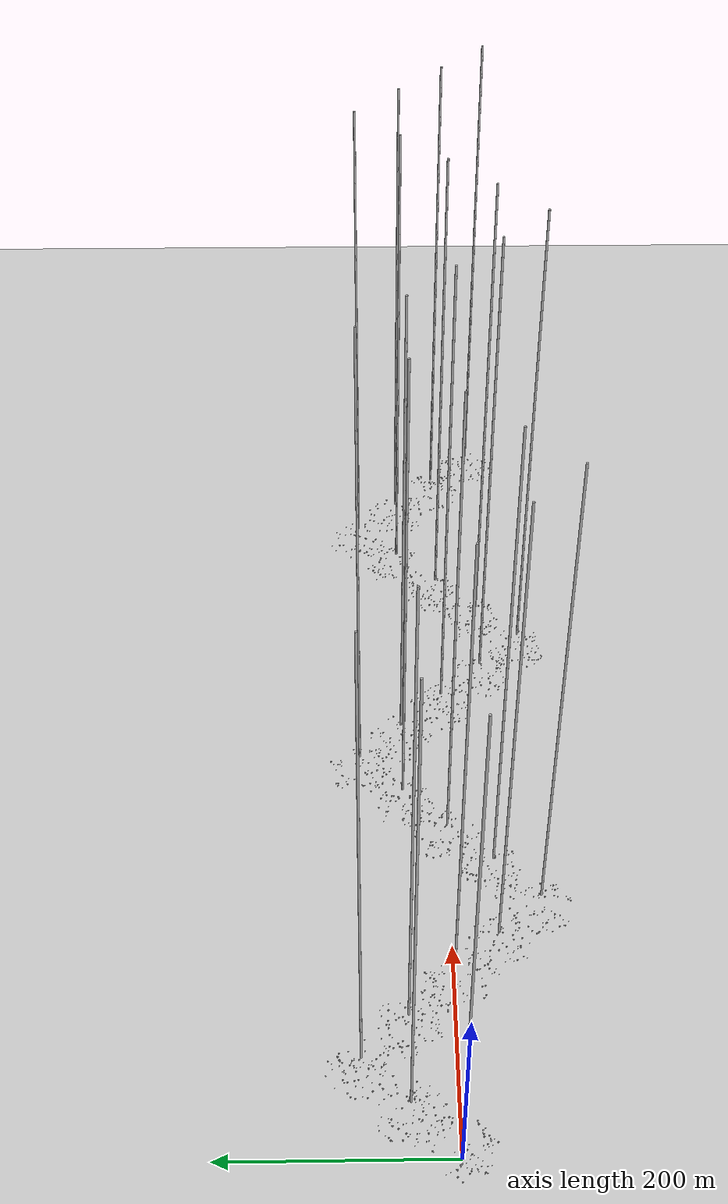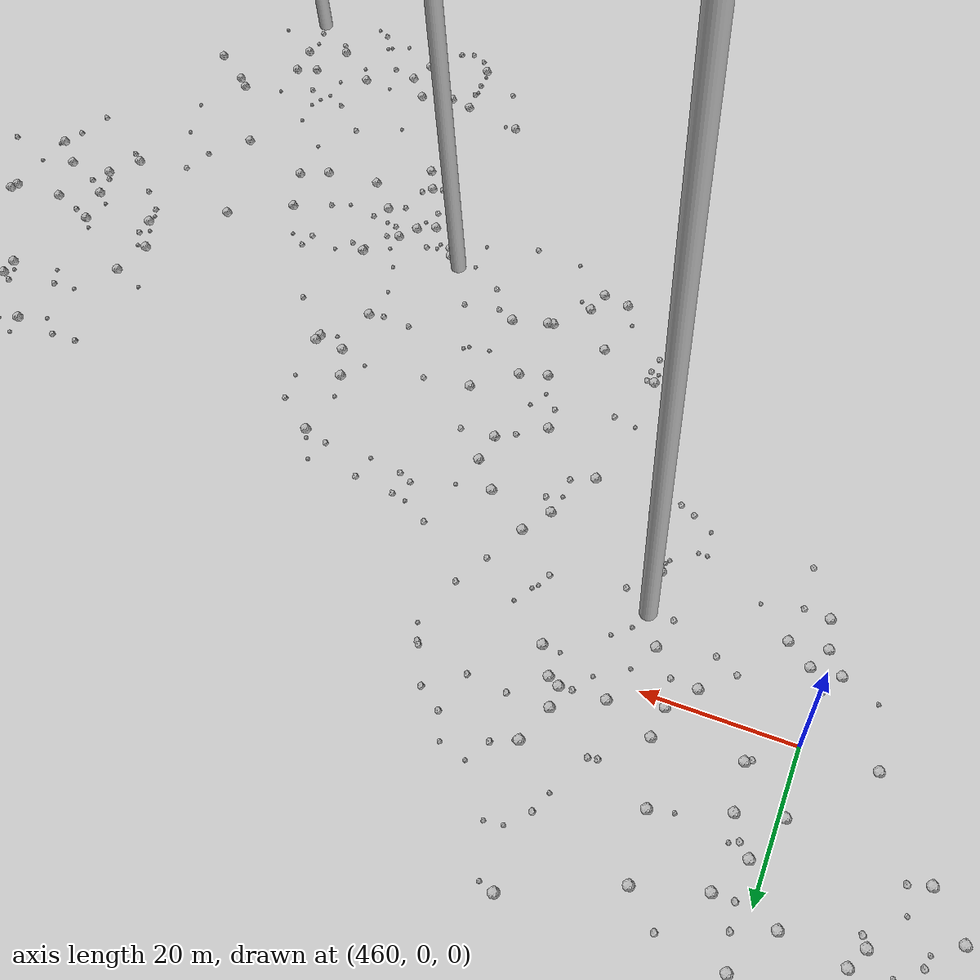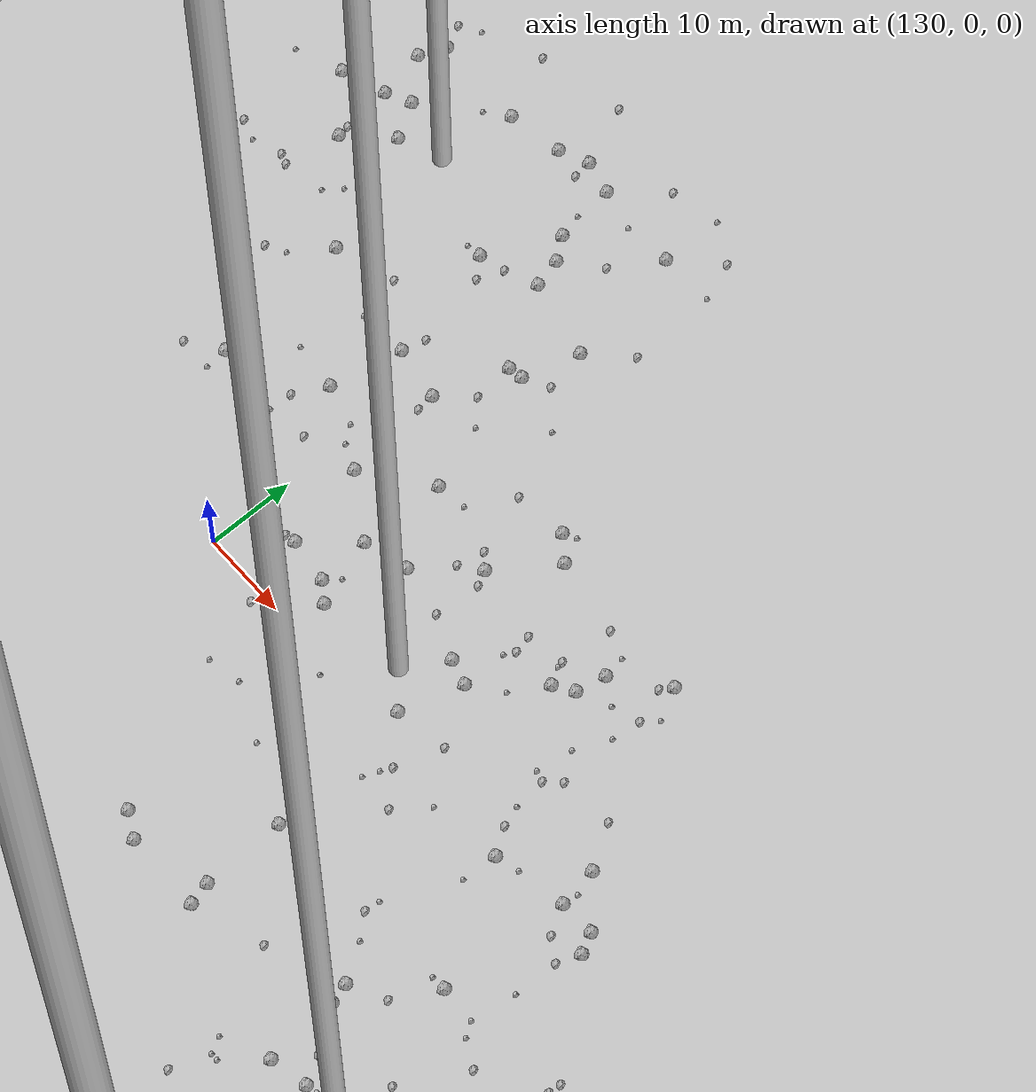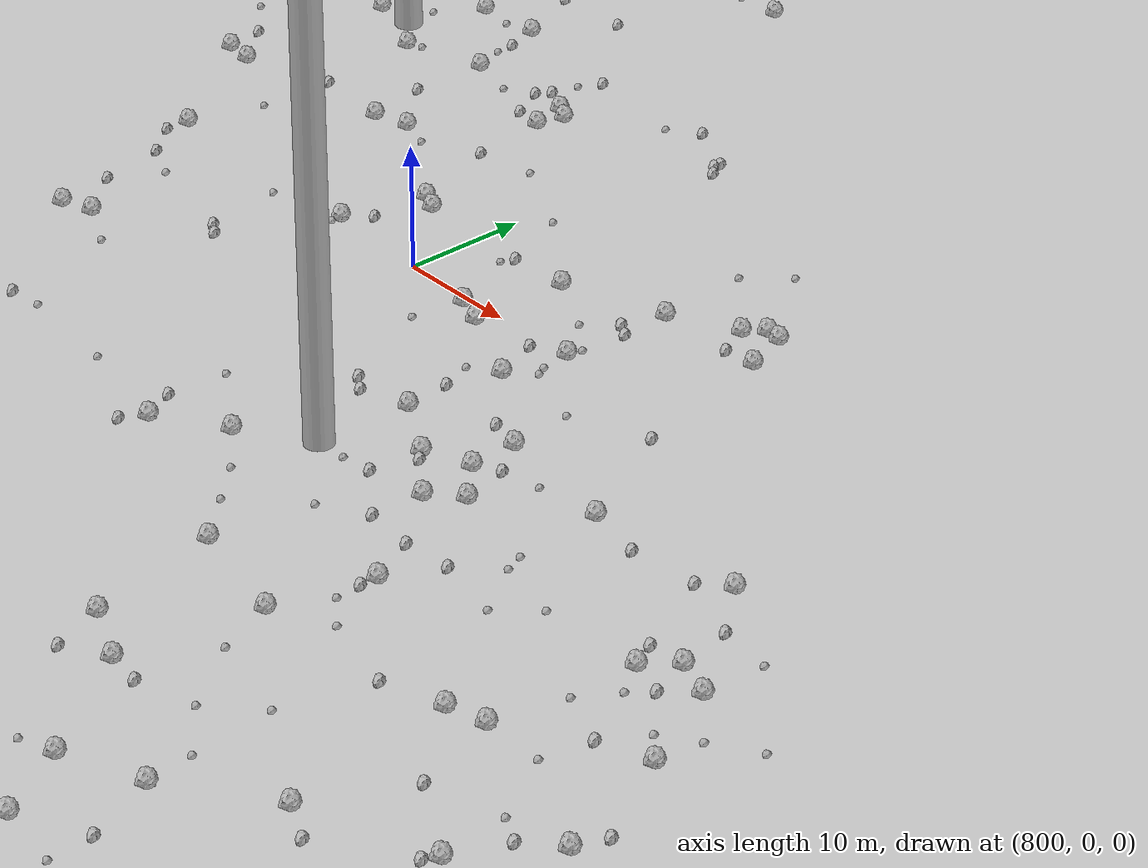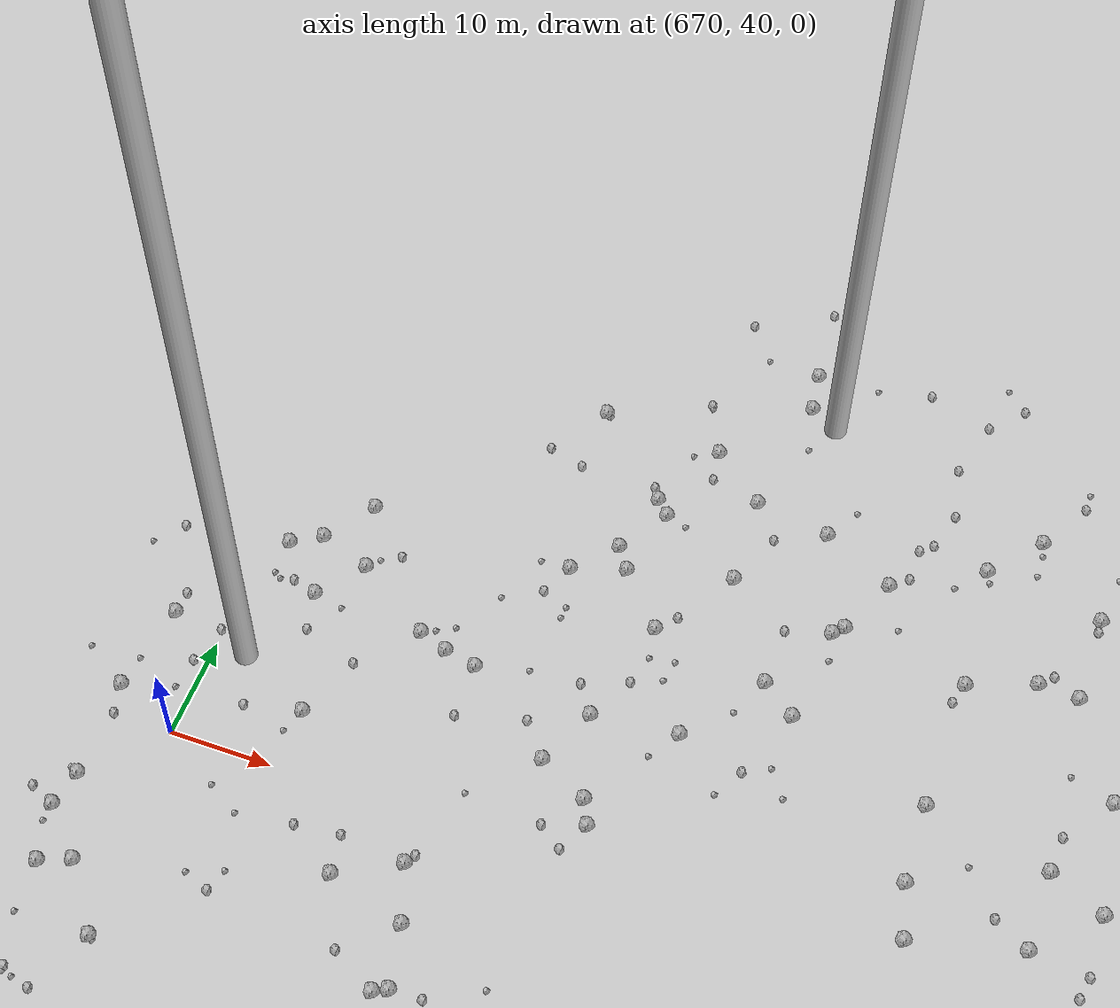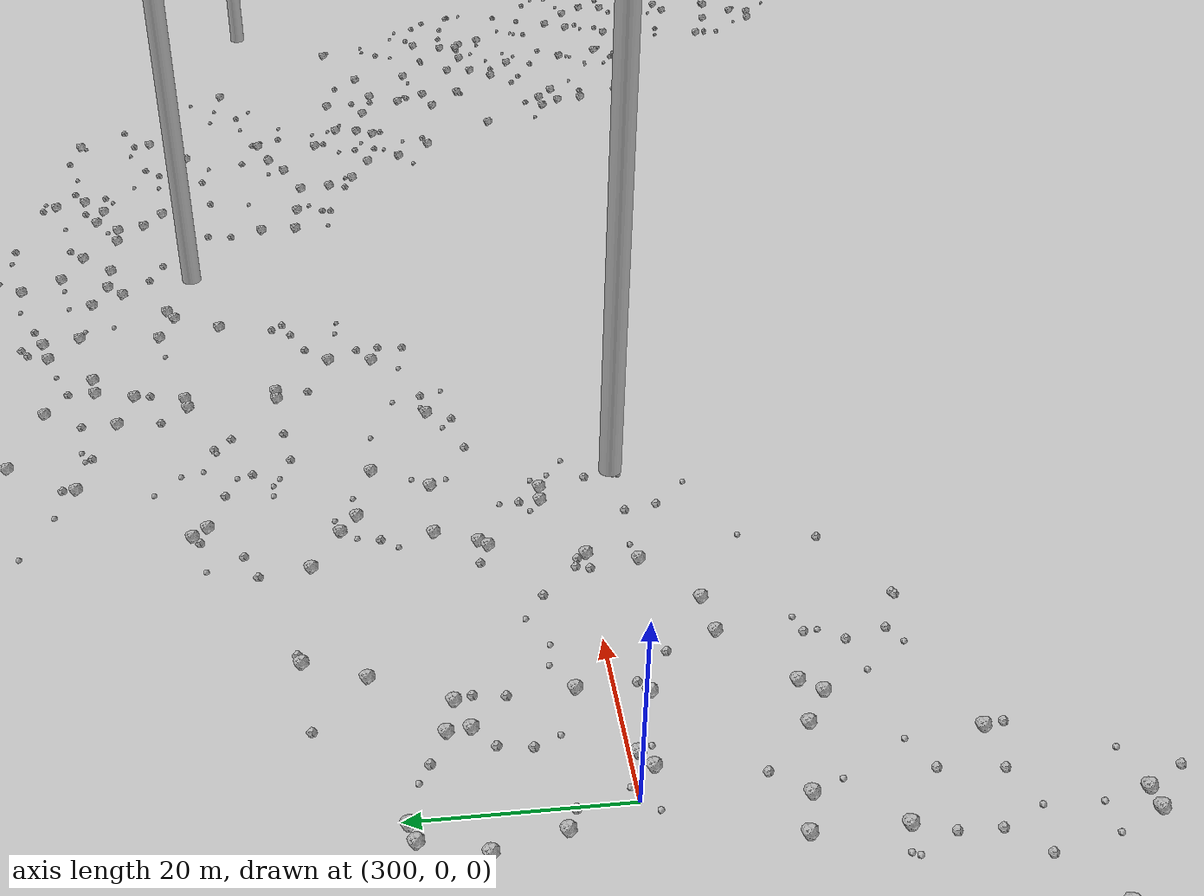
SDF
<sdf version="1.6">
 <world name="default">
  <include><uri>model://custom_ground</uri></include>
  <include><uri>model://sun</uri></include>
  <spherical_coordinates>
   <surface_model>EARTH_WGS84</surface_model>
   <latitude_deg>38.161479</latitude_deg>
   <longitude_deg>-122.454630</longitude_deg>
   <elevation>488.0</elevation>
   <heading_deg>90</heading_deg>
  </spherical_coordinates>
  <model name="rock1_0_0">
   <include><uri>model://rock1</uri><pose>-15.155290944000953 4.365618940866753 0.5 0 0 0</pose></include>
  </model>
  <model name="rock1_0_1">
   <include><uri>model://rock1</uri><pose>30.365419000079648 -14.592991532856605 0.5 0 0 0</pose></include>
  </model>
  <model name="rock1_0_2">
   <include><uri>model://rock1</uri><pose>-4.685724601052222 1.8078116303039735 0.5 0 0 0</pose></include>
  </model>
  <model name="rock1_0_3">
   <include><uri>model://rock1</uri><pose>32.927821810276846 1.2446686735971895 0.5 0 0 0</pose></include>
  </model>
  <model name="rock1_0_4">
   <include><uri>model://rock1</uri><pose>30.150597260708807 -1.5976378029808984 0.5 0 0 0</pose></include>
  </model>
  <model name="rock1_0_5">
   <include><uri>model://rock1</uri><pose>20.384381064537685 -22.731983526428003 0.5 0 0 0</pose></include>
  </model>
  <model name="rock1_0_6">
   <include><uri>model://rock1</uri><pose>-4.009605879602944 0.30030426166214497 0.5 0 0 0</pose></include>
  </model>
  <model name="rock1_0_7">
   <include><uri>model://rock1</uri><pose>25.352205897862348 -17.819912968124996 0.5 0 0 0</pose></include>
  </model>
  <model name="rock1_0_8">
   <include><uri>model://rock1</uri><pose>12.92503399981031 -21.008087417505813 0.5 0 0 0</pose></include>
  </model>
  <model name="rock1_0_9">
   <include><uri>model://rock1</uri><pose>-0.6413970402056322 6.295935949184333 0.5 0 0 0</pose></include>
  </model>
  <model name="rock1_0_10">
   <include><uri>model://rock1</uri><pose>15.815537231078586 -23.655461341816356 0.5 0 0 0</pose></include>
  </model>
  <model name="rock1_0_11">
   <include><uri>model://rock1</uri><pose>7.247741048486212 23.49112492799059 0.5 0 0 0</pose></include>
  </model>
  <model name="rock1_0_12">
   <include><uri>model://rock1</uri><pose>33.64038131830326 -13.838886148199528 0.5 0 0 0</pose></include>
  </model>
  <model name="rock1_0_13">
   <include><uri>model://rock1</uri><pose>33.44294067882 15.345545770132247 0.5 0 0 0</pose></include>
  </model>
  <model name="rock1_0_14">
   <include><uri>model://rock1</uri><pose>8.048631857187619 -4.091274904823361 0.5 0 0 0</pose></include>
  </model>
  <model name="rock1_0_15">
   <include><uri>model://rock1</uri><pose>31.29054005657496 7.2509887046850565 0.5 0 0 0</pose></include>
  </model>
  <model name="rock1_0_16">
   <include><uri>model://rock1</uri><pose>-12.38020011686414 -5.212112611298366 0.5 0 0 0</pose></include>
  </model>
  <model name="rock1_0_17">
   <include><uri>model://rock1</uri><pose>22.71396660971383 -2.4293549881669954 0.5 0 0 0</pose></include>
  </model>
  <model name="rock1_0_18">
   <include><uri>model://rock1</uri><pose>-19.237186051917103 0.4430849612807286 0.5 0 0 0</pose></include>
  </model>
  <model name="rock1_0_19">
   <include><uri>model://rock1</uri><pose>4.582420236013519 -8.045089005737445 0.5 0 0 0</pose></include>
  </model>
  <model name="rock1_0_20">
   <include><uri>model://rock1</uri><pose>14.606986802614287 -29.32037547963169 0.5 0 0 0</pose></include>
  </model>
  <model name="rock1_0_21">
   <include><uri>model://rock1</uri><pose>19.337013078334465 -18.437686806451623 0.5 0 0 0</pose></include>
  </model>
  <model name="rock1_0_22">
   <include><uri>model://rock1</uri><pose>-11.212825088565852 -17.952480824957064 0.5 0 0 0</pose></include>
  </model>
  <model name="rock1_0_23">
   <include><uri>model://rock1</uri><pose>36.42996186329433 13.011886992763806 0.5 0 0 0</pose></include>
  </model>
  <model name="rock1_0_24">
   <include><uri>model://rock1</uri><pose>-8.688486869352467 4.767346848159434 0.5 0 0 0</pose></include>
  </model>
  <model name="rock1_0_25">
   <include><uri>model://rock1</uri><pose>36.66671568372976 9.023741943835404 0.5 0 0 0</pose></include>
  </model>
  <model name="rock1_0_26">
   <include><uri>model://rock1</uri><pose>21.82293567414112 -18.34543638744787 0.5 0 0 0</pose></include>
  </model>
  <model name="rock2_0_0">
   <include><uri>model://rock2</uri><pose>21.152890966220184 0.19108551380897865 0.3 0 0 0</pose></include>
  </model>
  <model name="rock2_0_1">
   <include><uri>model://rock2</uri><pose>11.662210644562542 -17.592340504596066 0.3 0 0 0</pose></include>
  </model>
  <model name="rock2_0_2">
   <include><uri>model://rock2</uri><pose>-6.148561448682832 -19.68203694927474 0.3 0 0 0</pose></include>
  </model>
  <model name="rock2_0_3">
   <include><uri>model://rock2</uri><pose>-6.188656776708035 -14.812885038507101 0.3 0 0 0</pose></include>
  </model>
  <model name="rock2_0_4">
   <include><uri>model://rock2</uri><pose>3.2661009799126397 -6.852577313613207 0.3 0 0 0</pose></include>
  </model>
  <model name="rock2_0_5">
   <include><uri>model://rock2</uri><pose>27.813342868772153 20.698263095049207 0.3 0 0 0</pose></include>
  </model>
  <model name="rock2_0_6">
   <include><uri>model://rock2</uri><pose>16.165194366615147 -2.752231568381738 0.3 0 0 0</pose></include>
  </model>
  <model name="rock2_0_7">
   <include><uri>model://rock2</uri><pose>16.212905079257908 26.094483878973136 0.3 0 0 0</pose></include>
  </model>
  <model name="rock2_0_8">
   <include><uri>model://rock2</uri><pose>17.6675344452634 -23.152910236781203 0.3 0 0 0</pose></include>
  </model>
  <model name="rock2_0_9">
   <include><uri>model://rock2</uri><pose>12.711931435383775 -5.839265471316008 0.3 0 0 0</pose></include>
  </model>
  <model name="rock2_0_10">
   <include><uri>model://rock2</uri><pose>-6.124382838753309 1.2773143776204137 0.3 0 0 0</pose></include>
  </model>
  <model name="rock2_0_11">
   <include><uri>model://rock2</uri><pose>1.5112490304035333 -12.302126105353025 0.3 0 0 0</pose></include>
  </model>
  <model name="rock2_0_12">
   <include><uri>model://rock2</uri><pose>21.532274397430683 19.118262289963198 0.3 0 0 0</pose></include>
  </model>
  <model name="rock2_0_13">
   <include><uri>model://rock2</uri><pose>30.317073277652057 14.957250905905234 0.3 0 0 0</pose></include>
  </model>
  <model name="rock2_0_14">
   <include><uri>model://rock2</uri><pose>39.77590099883706 1.7424593463242708 0.3 0 0 0</pose></include>
  </model>
  <model name="rock2_0_15">
   <include><uri>model://rock2</uri><pose>-10.110485681391895 -6.625393339734941 0.3 0 0 0</pose></include>
  </model>
  <model name="rock2_0_16">
   <include><uri>model://rock2</uri><pose>27.31353427778742 8.713380195348279 0.3 0 0 0</pose></include>
  </model>
  <model name="rock2_0_17">
   <include><uri>model://rock2</uri><pose>32.41477166611019 7.1520383299204155 0.3 0 0 0</pose></include>
  </model>
  <model name="rock2_0_18">
   <include><uri>model://rock2</uri><pose>-12.092192879682191 -17.331173158909266 0.3 0 0 0</pose></include>
  </model>
  <model name="rock2_0_19">
   <include><uri>model://rock2</uri><pose>-11.957030908008559 -19.358342614783044 0.3 0 0 0</pose></include>
  </model>
  <model name="rock2_0_20">
   <include><uri>model://rock2</uri><pose>-8.754265414970348 -11.917275561621608 0.3 0 0 0</pose></include>
  </model>
  <model name="rock2_0_21">
   <include><uri>model://rock2</uri><pose>7.2727001131522115 1.8274199884027205 0.3 0 0 0</pose></include>
  </model>
  <model name="rock2_0_22">
   <include><uri>model://rock2</uri><pose>36.012458113281525 6.333173507131271 0.3 0 0 0</pose></include>
  </model>
  <model name="rock2_0_23">
   <include><uri>model://rock2</uri><pose>-8.271981190895426 -6.906790240898143 0.3 0 0 0</pose></include>
  </model>
  <model name="rock2_0_24">
   <include><uri>model://rock2</uri><pose>0.19010698496141032 -6.326412438396591 0.3 0 0 0</pose></include>
  </model>
  <model name="rock2_0_25">
   <include><uri>model://rock2</uri><pose>27.060271791631877 -19.732829817937404 0.3 0 0 0</pose></include>
  </model>
  <model name="rock2_0_26">
   <include><uri>model://rock2</uri><pose>31.52717284918328 -13.904625345878227 0.3 0 0 0</pose></include>
  </model>
  <model name="rock3_0_0">
   <include><uri>model://rock3</uri><pose>-10.453749237029964 -12.517764969547759 0.2 0 0 0</pose></include>
  </model>
  <model name="rock3_0_1">
   <include><uri>model://rock3</uri><pose>-12.805476436230434 13.374938108711532 0.2 0 0 0</pose></include>
  </model>
  <model name="rock3_0_2">
   <include><uri>model://rock3</uri><pose>26.66981045385903 -1.2707296340441907 0.2 0 0 0</pose></include>
  </model>
  <model name="rock3_0_3">
   <include><uri>model://rock3</uri><pose>3.4385253006144296 -9.449663513751108 0.2 0 0 0</pose></include>
  </model>
  <model name="rock3_0_4">
   <include><uri>model://rock3</uri><pose>-4.751588377200255 -10.425232680521628 0.2 0 0 0</pose></include>
  </model>
  <model name="rock3_0_5">
   <include><uri>model://rock3</uri><pose>-3.44593079212785 -2.924942903053079 0.2 0 0 0</pose></include>
  </model>
  <model name="rock3_0_6">
   <include><uri>model://rock3</uri><pose>19.076829789098298 13.418282969422378 0.2 0 0 0</pose></include>
  </model>
  <model name="rock3_0_7">
   <include><uri>model://rock3</uri><pose>-9.739824129699915 4.393362214599243 0.2 0 0 0</pose></include>
  </model>
  <model name="rock3_0_8">
   <include><uri>model://rock3</uri><pose>-11.066748216391941 9.469054845625855 0.2 0 0 0</pose></include>
  </model>
  <model name="rock3_0_9">
   <include><uri>model://rock3</uri><pose>13.591698132430707 1.0210183171062006 0.2 0 0 0</pose></include>
  </model>
  <model name="rock3_0_10">
   <include><uri>model://rock3</uri><pose>6.188529766204272 5.941837475458655 0.2 0 0 0</pose></include>
  </model>
  <model name="rock3_0_11">
   <include><uri>model://rock3</uri><pose>10.495965688679469 -21.431620549988168 0.2 0 0 0</pose></include>
  </model>
  <model name="rock3_0_12">
   <include><uri>model://rock3</uri><pose>17.32989384615852 -26.456646447223275 0.2 0 0 0</pose></include>
  </model>
  <model name="rock3_0_13">
   <include><uri>model://rock3</uri><pose>21.273860680790875 -4.9035683792396085 0.2 0 0 0</pose></include>
  </model>
  <model name="rock3_0_14">
   <include><uri>model://rock3</uri><pose>22.550699361247354 -17.17903784985006 0.2 0 0 0</pose></include>
  </model>
  <model name="rock3_0_15">
   <include><uri>model://rock3</uri><pose>-7.775184572171295 -11.461966070301088 0.2 0 0 0</pose></include>
  </model>
  <model name="rock3_0_16">
   <include><uri>model://rock3</uri><pose>5.502757266031185 -23.900115317191513 0.2 0 0 0</pose></include>
  </model>
  <model name="rock3_0_17">
   <include><uri>model://rock3</uri><pose>-1.4649850459772686 -16.24797164164451 0.2 0 0 0</pose></include>
  </model>
  <model name="rock3_0_18">
   <include><uri>model://rock3</uri><pose>12.392453363219992 21.83101547869473 0.2 0 0 0</pose></include>
  </model>
  <model name="rock3_0_19">
   <include><uri>model://rock3</uri><pose>17.27415738487762 -1.3257091298523385 0.2 0 0 0</pose></include>
  </model>
  <model name="rock3_0_20">
   <include><uri>model://rock3</uri><pose>12.043890485985635 -24.708034796461835 0.2 0 0 0</pose></include>
  </model>
  <model name="rock3_0_21">
   <include><uri>model://rock3</uri><pose>6.199522461997336 22.616930514877644 0.2 0 0 0</pose></include>
  </model>
  <model name="rock3_0_22">
   <include><uri>model://rock3</uri><pose>25.9860172988463 13.650190945387116 0.2 0 0 0</pose></include>
  </model>
  <model name="rock3_0_23">
   <include><uri>model://rock3</uri><pose>7.792144621554261 -18.42380909577846 0.2 0 0 0</pose></include>
  </model>
  <model name="rock3_0_24">
   <include><uri>model://rock3</uri><pose>-7.3854830150759465 -3.3314491863256563 0.2 0 0 0</pose></include>
  </model>
  <model name="rock3_0_25">
   <include><uri>model://rock3</uri><pose>32.45406875623681 -0.5684548847825575 0.2 0 0 0</pose></include>
  </model>
  <model name="rock3_0_26">
   <include><uri>model://rock3</uri><pose>-5.48507406005263 -23.498636306057808 0.2 0 0 0</pose></include>
  </model>
  <model name="rock1_1_0">
   <include><uri>model://rock1</uri><pose>38.611970582568205 19.878207486552405 0.5 0 0 0</pose></include>
  </model>
  <model name="rock1_1_1">
   <include><uri>model://rock1</uri><pose>52.26662150555048 32.48853989832445 0.5 0 0 0</pose></include>
  </model>
  <model name="rock1_1_2">
   <include><uri>model://rock1</uri><pose>35.219792511267364 55.85887796595069 0.5 0 0 0</pose></include>
  </model>
  <model name="rock1_1_3">
   <include><uri>model://rock1</uri><pose>55.405255210666226 26.749399072703923 0.5 0 0 0</pose></include>
  </model>
  <model name="rock1_1_4">
   <include><uri>model://rock1</uri><pose>34.20873723945094 30.755576900488567 0.5 0 0 0</pose></include>
  </model>
  <model name="rock1_1_5">
   <include><uri>model://rock1</uri><pose>29.38547588766232 55.2265228403218 0.5 0 0 0</pose></include>
  </model>
  <model name="rock1_1_6">
   <include><uri>model://rock1</uri><pose>19.137448083107724 58.20500258323139 0.5 0 0 0</pose></include>
  </model>
  <model name="rock1_1_7">
   <include><uri>model://rock1</uri><pose>56.479892370891775 55.634532970760795 0.5 0 0 0</pose></include>
  </model>
  <model name="rock1_1_8">
   <include><uri>model://rock1</uri><pose>51.68164524529155 41.55390311784572 0.5 0 0 0</pose></include>
  </model>
  <model name="rock1_1_9">
   <include><uri>model://rock1</uri><pose>26.9190949474402 50.25725918252719 0.5 0 0 0</pose></include>
  </model>
  <model name="rock1_1_10">
   <include><uri>model://rock1</uri><pose>22.862711301170002 44.0416939445986 0.5 0 0 0</pose></include>
  </model>
  <model name="rock1_1_11">
   <include><uri>model://rock1</uri><pose>48.1896177181469 11.139688703704687 0.5 0 0 0</pose></include>
  </model>
  <model name="rock1_1_12">
   <include><uri>model://rock1</uri><pose>55.29377856135509 43.06552173349751 0.5 0 0 0</pose></include>
  </model>
  <model name="rock1_1_13">
   <include><uri>model://rock1</uri><pose>54.402181964333856 40.54899494138181 0.5 0 0 0</pose></include>
  </model>
  <model name="rock1_1_14">
   <include><uri>model://rock1</uri><pose>58.243965806701326 50.559352671649314 0.5 0 0 0</pose></include>
  </model>
  <model name="rock1_1_15">
   <include><uri>model://rock1</uri><pose>16.712785330120276 56.66730417168134 0.5 0 0 0</pose></include>
  </model>
  <model name="rock1_1_16">
   <include><uri>model://rock1</uri><pose>45.537876083644534 20.886693463041688 0.5 0 0 0</pose></include>
  </model>
  <model name="rock1_1_17">
   <include><uri>model://rock1</uri><pose>66.32613424676481 51.830899633872384 0.5 0 0 0</pose></include>
  </model>
  <model name="rock1_1_18">
   <include><uri>model://rock1</uri><pose>35.27644867784029 33.31215828032758 0.5 0 0 0</pose></include>
  </model>
  <model name="rock1_1_19">
   <include><uri>model://rock1</uri><pose>68.65662740851731 34.47754394783732 0.5 0 0 0</pose></include>
  </model>
  <model name="rock1_1_20">
   <include><uri>model://rock1</uri><pose>45.139697013645474 46.998675140237594 0.5 0 0 0</pose></include>
  </model>
  <model name="rock1_1_21">
   <include><uri>model://rock1</uri><pose>42.050915946906066 29.99777584599681 0.5 0 0 0</pose></include>
  </model>
  <model name="rock1_1_22">
   <include><uri>model://rock1</uri><pose>58.95691490191824 36.37074255975118 0.5 0 0 0</pose></include>
  </model>
  <model name="rock1_1_23">
   <include><uri>model://rock1</uri><pose>22.682788165219833 26.172540418075407 0.5 0 0 0</pose></include>
  </model>
  <model name="rock1_1_24">
   <include><uri>model://rock1</uri><pose>53.08999854103922 36.643461093679974 0.5 0 0 0</pose></include>
  </model>
  <model name="rock1_1_25">
   <include><uri>model://rock1</uri><pose>25.37896894064042 14.438843730197046 0.5 0 0 0</pose></include>
  </model>
  <model name="rock1_1_26">
   <include><uri>model://rock1</uri><pose>16.865700719843925 46.84225852872734 0.5 0 0 0</pose></include>
  </model>
  <model name="rock2_1_0">
   <include><uri>model://rock2</uri><pose>32.7595240670575 57.401502449781404 0.3 0 0 0</pose></include>
  </model>
  <model name="rock2_1_1">
   <include><uri>model://rock2</uri><pose>63.85904602542968 31.896968297074263 0.3 0 0 0</pose></include>
  </model>
  <model name="rock2_1_2">
   <include><uri>model://rock2</uri><pose>22.46683967083905 35.46898712358036 0.3 0 0 0</pose></include>
  </model>
  <model name="rock2_1_3">
   <include><uri>model://rock2</uri><pose>15.372336112656315 34.84886635970264 0.3 0 0 0</pose></include>
  </model>
  <model name="rock2_1_4">
   <include><uri>model://rock2</uri><pose>30.778553785450548 46.57346912003244 0.3 0 0 0</pose></include>
  </model>
  <model name="rock2_1_5">
   <include><uri>model://rock2</uri><pose>32.0480383971255 38.815662549563626 0.3 0 0 0</pose></include>
  </model>
  <model name="rock2_1_6">
   <include><uri>model://rock2</uri><pose>29.770500651369534 23.57254545034557 0.3 0 0 0</pose></include>
  </model>
  <model name="rock2_1_7">
   <include><uri>model://rock2</uri><pose>15.601533354864209 28.1751175245855 0.3 0 0 0</pose></include>
  </model>
  <model name="rock2_1_8">
   <include><uri>model://rock2</uri><pose>46.60077304531692 12.932657992868515 0.3 0 0 0</pose></include>
  </model>
  <model name="rock2_1_9">
   <include><uri>model://rock2</uri><pose>20.915163164490302 61.104266187719276 0.3 0 0 0</pose></include>
  </model>
  <model name="rock2_1_10">
   <include><uri>model://rock2</uri><pose>45.10499070205753 29.776683495518004 0.3 0 0 0</pose></include>
  </model>
  <model name="rock2_1_11">
   <include><uri>model://rock2</uri><pose>63.568370256919685 50.76987311927629 0.3 0 0 0</pose></include>
  </model>
  <model name="rock2_1_12">
   <include><uri>model://rock2</uri><pose>20.212532470852366 42.571225479983624 0.3 0 0 0</pose></include>
  </model>
  <model name="rock2_1_13">
   <include><uri>model://rock2</uri><pose>42.217880393214045 30.457639033366487 0.3 0 0 0</pose></include>
  </model>
  <model name="rock2_1_14">
   <include><uri>model://rock2</uri><pose>33.52018240684805 19.023285910555636 0.3 0 0 0</pose></include>
  </model>
  <model name="rock2_1_15">
   <include><uri>model://rock2</uri><pose>48.61982321380918 65.70258229169518 0.3 0 0 0</pose></include>
  </model>
  <model name="rock2_1_16">
   <include><uri>model://rock2</uri><pose>11.79263376867834 37.40294774075167 0.3 0 0 0</pose></include>
  </model>
  <model name="rock2_1_17">
   <include><uri>model://rock2</uri><pose>36.104490470401295 58.19536337931314 0.3 0 0 0</pose></include>
  </model>
  <model name="rock2_1_18">
   <include><uri>model://rock2</uri><pose>39.1046557802385 27.544885297090868 0.3 0 0 0</pose></include>
  </model>
  <model name="rock2_1_19">
   <include><uri>model://rock2</uri><pose>53.3522226431968 61.385073098769055 0.3 0 0 0</pose></include>
  </model>
  <model name="rock2_1_20">
   <include><uri>model://rock2</uri><pose>25.46839732591571 66.0660286856392 0.3 0 0 0</pose></include>
  </model>
  <model name="rock2_1_21">
   <include><uri>model://rock2</uri><pose>64.71351686513819 23.80058695910803 0.3 0 0 0</pose></include>
  </model>
  <model name="rock2_1_22">
   <include><uri>model://rock2</uri><pose>57.34292455988603 58.087102970695476 0.3 0 0 0</pose></include>
  </model>
  <model name="rock2_1_23">
   <include><uri>model://rock2</uri><pose>57.754331559657004 16.403504629555943 0.3 0 0 0</pose></include>
  </model>
  <model name="rock2_1_24">
   <include><uri>model://rock2</uri><pose>18.18018307520089 35.807656809862515 0.3 0 0 0</pose></include>
  </model>
  <model name="rock2_1_25">
   <include><uri>model://rock2</uri><pose>31.97683965477801 43.60430539845757 0.3 0 0 0</pose></include>
  </model>
  <model name="rock2_1_26">
   <include><uri>model://rock2</uri><pose>56.26939988167056 24.129158736957393 0.3 0 0 0</pose></include>
  </model>
  <model name="rock3_1_0">
   <include><uri>model://rock3</uri><pose>56.42740152271628 17.80462437458213 0.2 0 0 0</pose></include>
  </model>
  <model name="rock3_1_1">
   <include><uri>model://rock3</uri><pose>43.46151503485855 37.18798068758524 0.2 0 0 0</pose></include>
  </model>
  <model name="rock3_1_2">
   <include><uri>model://rock3</uri><pose>60.5557690452542 34.66648023805717 0.2 0 0 0</pose></include>
  </model>
  <model name="rock3_1_3">
   <include><uri>model://rock3</uri><pose>55.473960861127 36.39346987703049 0.2 0 0 0</pose></include>
  </model>
  <model name="rock3_1_4">
   <include><uri>model://rock3</uri><pose>32.43787027179944 50.91611814883968 0.2 0 0 0</pose></include>
  </model>
  <model name="rock3_1_5">
   <include><uri>model://rock3</uri><pose>38.75609204309503 37.99237938402166 0.2 0 0 0</pose></include>
  </model>
  <model name="rock3_1_6">
   <include><uri>model://rock3</uri><pose>22.632248722350518 33.39184638301842 0.2 0 0 0</pose></include>
  </model>
  <model name="rock3_1_7">
   <include><uri>model://rock3</uri><pose>26.13365385783463 34.269597561884225 0.2 0 0 0</pose></include>
  </model>
  <model name="rock3_1_8">
   <include><uri>model://rock3</uri><pose>16.519304175671877 55.57172852619761 0.2 0 0 0</pose></include>
  </model>
  <model name="rock3_1_9">
   <include><uri>model://rock3</uri><pose>47.981256479132256 55.20665617279319 0.2 0 0 0</pose></include>
  </model>
  <model name="rock3_1_10">
   <include><uri>model://rock3</uri><pose>48.53291641580741 25.282267021754297 0.2 0 0 0</pose></include>
  </model>
  <model name="rock3_1_11">
   <include><uri>model://rock3</uri><pose>29.882519733191632 66.40009278143413 0.2 0 0 0</pose></include>
  </model>
  <model name="rock3_1_12">
   <include><uri>model://rock3</uri><pose>67.43834046205433 28.048302564175458 0.2 0 0 0</pose></include>
  </model>
  <model name="rock3_1_13">
   <include><uri>model://rock3</uri><pose>34.12178538421732 17.265681116235033 0.2 0 0 0</pose></include>
  </model>
  <model name="rock3_1_14">
   <include><uri>model://rock3</uri><pose>50.65905589771562 28.631870740473303 0.2 0 0 0</pose></include>
  </model>
  <model name="rock3_1_15">
   <include><uri>model://rock3</uri><pose>37.88619166804525 57.93318843753879 0.2 0 0 0</pose></include>
  </model>
  <model name="rock3_1_16">
   <include><uri>model://rock3</uri><pose>55.790586744400755 35.27591640566557 0.2 0 0 0</pose></include>
  </model>
  <model name="rock3_1_17">
   <include><uri>model://rock3</uri><pose>25.413962677209383 26.839456746800884 0.2 0 0 0</pose></include>
  </model>
  <model name="rock3_1_18">
   <include><uri>model://rock3</uri><pose>50.08013724740748 35.55474114204555 0.2 0 0 0</pose></include>
  </model>
  <model name="rock3_1_19">
   <include><uri>model://rock3</uri><pose>37.72569643628647 64.04555453009374 0.2 0 0 0</pose></include>
  </model>
  <model name="rock3_1_20">
   <include><uri>model://rock3</uri><pose>32.9389045645496 31.97162542128951 0.2 0 0 0</pose></include>
  </model>
  <model name="rock3_1_21">
   <include><uri>model://rock3</uri><pose>44.9888969447751 51.73303608681151 0.2 0 0 0</pose></include>
  </model>
  <model name="rock3_1_22">
   <include><uri>model://rock3</uri><pose>58.650992950203104 26.129114237162753 0.2 0 0 0</pose></include>
  </model>
  <model name="rock3_1_23">
   <include><uri>model://rock3</uri><pose>55.227331498666246 36.31690832717587 0.2 0 0 0</pose></include>
  </model>
  <model name="rock3_1_24">
   <include><uri>model://rock3</uri><pose>47.87253218689611 30.962213410490037 0.2 0 0 0</pose></include>
  </model>
  <model name="rock3_1_25">
   <include><uri>model://rock3</uri><pose>23.931570638727983 18.479036600909794 0.2 0 0 0</pose></include>
  </model>
  <model name="rock3_1_26">
   <include><uri>model://rock3</uri><pose>22.09972605874129 41.09525437800345 0.2 0 0 0</pose></include>
  </model>
  <model name="rock1_2_0">
   <include><uri>model://rock1</uri><pose>95.4806787829061 98.8826205620031 0.5 0 0 0</pose></include>
  </model>
  <model name="rock1_2_1">
   <include><uri>model://rock1</uri><pose>78.58267613958249 84.28064352995048 0.5 0 0 0</pose></include>
  </model>
  <model name="rock1_2_2">
   <include><uri>model://rock1</uri><pose>70.19216520108867 85.40314768699895 0.5 0 0 0</pose></include>
  </model>
  <model name="rock1_2_3">
   <include><uri>model://rock1</uri><pose>88.1716390251959 107.90606695940446 0.5 0 0 0</pose></include>
  </model>
  <model name="rock1_2_4">
   <include><uri>model://rock1</uri><pose>84.55042694788813 61.16784228152611 0.5 0 0 0</pose></include>
  </model>
  <model name="rock1_2_5">
   <include><uri>model://rock1</uri><pose>62.35713544619425 62.24026805245819 0.5 0 0 0</pose></include>
  </model>
  <model name="rock1_2_6">
   <include><uri>model://rock1</uri><pose>89.19556460356289 98.2716672845801 0.5 0 0 0</pose></include>
  </model>
  <model name="rock1_2_7">
   <include><uri>model://rock1</uri><pose>74.25591577346148 53.80962040172634 0.5 0 0 0</pose></include>
  </model>
  <model name="rock1_2_8">
   <include><uri>model://rock1</uri><pose>58.71496651677671 91.35903506649629 0.5 0 0 0</pose></include>
  </model>
  <model name="rock1_2_9">
   <include><uri>model://rock1</uri><pose>66.74782619901077 64.85958798732561 0.5 0 0 0</pose></include>
  </model>
  <model name="rock1_2_10">
   <include><uri>model://rock1</uri><pose>68.77457110860973 91.53606832813223 0.5 0 0 0</pose></include>
  </model>
  <model name="rock1_2_11">
   <include><uri>model://rock1</uri><pose>54.483048248764284 74.93982778074556 0.5 0 0 0</pose></include>
  </model>
  <model name="rock1_2_12">
   <include><uri>model://rock1</uri><pose>93.77350349069093 64.42168525027394 0.5 0 0 0</pose></include>
  </model>
  <model name="rock1_2_13">
   <include><uri>model://rock1</uri><pose>90.01764704412415 67.76711279995817 0.5 0 0 0</pose></include>
  </model>
  <model name="rock1_2_14">
   <include><uri>model://rock1</uri><pose>55.38219149742878 88.70784320063572 0.5 0 0 0</pose></include>
  </model>
  <model name="rock1_2_15">
   <include><uri>model://rock1</uri><pose>60.30506733408145 70.62732613231188 0.5 0 0 0</pose></include>
  </model>
  <model name="rock1_2_16">
   <include><uri>model://rock1</uri><pose>54.029182273058275 84.89155116305214 0.5 0 0 0</pose></include>
  </model>
  <model name="rock1_2_17">
   <include><uri>model://rock1</uri><pose>89.75837237224724 81.78498362502407 0.5 0 0 0</pose></include>
  </model>
  <model name="rock1_2_18">
   <include><uri>model://rock1</uri><pose>93.41097399242071 57.85425260637124 0.5 0 0 0</pose></include>
  </model>
  <model name="rock1_2_19">
   <include><uri>model://rock1</uri><pose>82.44842025745966 63.30339593831656 0.5 0 0 0</pose></include>
  </model>
  <model name="rock1_2_20">
   <include><uri>model://rock1</uri><pose>84.55420350209374 89.32011576230005 0.5 0 0 0</pose></include>
  </model>
  <model name="rock1_2_21">
   <include><uri>model://rock1</uri><pose>88.56233694484357 87.79212790666253 0.5 0 0 0</pose></include>
  </model>
  <model name="rock1_2_22">
   <include><uri>model://rock1</uri><pose>86.83029356136456 95.7142314758077 0.5 0 0 0</pose></include>
  </model>
  <model name="rock1_2_23">
   <include><uri>model://rock1</uri><pose>81.16935356093202 73.93979699022512 0.5 0 0 0</pose></include>
  </model>
  <model name="rock1_2_24">
   <include><uri>model://rock1</uri><pose>83.5454789764948 70.05203672896715 0.5 0 0 0</pose></include>
  </model>
  <model name="rock1_2_25">
   <include><uri>model://rock1</uri><pose>70.78964066421926 95.42946034214958 0.5 0 0 0</pose></include>
  </model>
  <model name="rock1_2_26">
   <include><uri>model://rock1</uri><pose>92.26369644642406 99.44041333262447 0.5 0 0 0</pose></include>
  </model>
  <model name="rock2_2_0">
   <include><uri>model://rock2</uri><pose>68.6359545764336 93.85582675969816 0.3 0 0 0</pose></include>
  </model>
  <model name="rock2_2_1">
   <include><uri>model://rock2</uri><pose>83.94489712694254 98.1416139972608 0.3 0 0 0</pose></include>
  </model>
  <model name="rock2_2_2">
   <include><uri>model://rock2</uri><pose>88.50116128320477 71.0305435823357 0.3 0 0 0</pose></include>
  </model>
  <model name="rock2_2_3">
   <include><uri>model://rock2</uri><pose>92.54167054672378 100.36617958579453 0.3 0 0 0</pose></include>
  </model>
  <model name="rock2_2_4">
   <include><uri>model://rock2</uri><pose>79.48311346155013 94.2316547613662 0.3 0 0 0</pose></include>
  </model>
  <model name="rock2_2_5">
   <include><uri>model://rock2</uri><pose>88.23592393497927 97.4760649320278 0.3 0 0 0</pose></include>
  </model>
  <model name="rock2_2_6">
   <include><uri>model://rock2</uri><pose>89.23990662472167 86.05106306471306 0.3 0 0 0</pose></include>
  </model>
  <model name="rock2_2_7">
   <include><uri>model://rock2</uri><pose>78.97299661433888 60.179681166800364 0.3 0 0 0</pose></include>
  </model>
  <model name="rock2_2_8">
   <include><uri>model://rock2</uri><pose>97.50596076886237 76.85113706733136 0.3 0 0 0</pose></include>
  </model>
  <model name="rock2_2_9">
   <include><uri>model://rock2</uri><pose>80.62134273007393 68.39209849857647 0.3 0 0 0</pose></include>
  </model>
  <model name="rock2_2_10">
   <include><uri>model://rock2</uri><pose>65.26562664528485 84.71577138630838 0.3 0 0 0</pose></include>
  </model>
  <model name="rock2_2_11">
   <include><uri>model://rock2</uri><pose>73.1543221466242 75.87352657596392 0.3 0 0 0</pose></include>
  </model>
  <model name="rock2_2_12">
   <include><uri>model://rock2</uri><pose>108.32972632958855 77.03109260425654 0.3 0 0 0</pose></include>
  </model>
  <model name="rock2_2_13">
   <include><uri>model://rock2</uri><pose>85.59666335562963 59.20734256768393 0.3 0 0 0</pose></include>
  </model>
  <model name="rock2_2_14">
   <include><uri>model://rock2</uri><pose>97.42767118613399 90.91838343670284 0.3 0 0 0</pose></include>
  </model>
  <model name="rock2_2_15">
   <include><uri>model://rock2</uri><pose>85.6543113226873 104.84937310507459 0.3 0 0 0</pose></include>
  </model>
  <model name="rock2_2_16">
   <include><uri>model://rock2</uri><pose>95.85284914508944 61.38686392583858 0.3 0 0 0</pose></include>
  </model>
  <model name="rock2_2_17">
   <include><uri>model://rock2</uri><pose>82.38737281251954 85.77695151978043 0.3 0 0 0</pose></include>
  </model>
  <model name="rock2_2_18">
   <include><uri>model://rock2</uri><pose>78.72322582182112 95.68753714780576 0.3 0 0 0</pose></include>
  </model>
  <model name="rock2_2_19">
   <include><uri>model://rock2</uri><pose>74.72533655464045 74.66443319334445 0.3 0 0 0</pose></include>
  </model>
  <model name="rock2_2_20">
   <include><uri>model://rock2</uri><pose>71.33147641373664 82.53284155086642 0.3 0 0 0</pose></include>
  </model>
  <model name="rock2_2_21">
   <include><uri>model://rock2</uri><pose>76.65708060840588 93.09536064415303 0.3 0 0 0</pose></include>
  </model>
  <model name="rock2_2_22">
   <include><uri>model://rock2</uri><pose>84.06349718562383 86.42022187544845 0.3 0 0 0</pose></include>
  </model>
  <model name="rock2_2_23">
   <include><uri>model://rock2</uri><pose>55.3092770371211 78.68495992755305 0.3 0 0 0</pose></include>
  </model>
  <model name="rock2_2_24">
   <include><uri>model://rock2</uri><pose>64.109754688248 79.01721258584287 0.3 0 0 0</pose></include>
  </model>
  <model name="rock2_2_25">
   <include><uri>model://rock2</uri><pose>76.14051657553897 64.2983953728181 0.3 0 0 0</pose></include>
  </model>
  <model name="rock2_2_26">
   <include><uri>model://rock2</uri><pose>84.76884056254477 73.72905125190773 0.3 0 0 0</pose></include>
  </model>
  <model name="rock3_2_0">
   <include><uri>model://rock3</uri><pose>74.54737311639913 62.32806441348761 0.2 0 0 0</pose></include>
  </model>
  <model name="rock3_2_1">
   <include><uri>model://rock3</uri><pose>91.2952662986292 90.77458853102527 0.2 0 0 0</pose></include>
  </model>
  <model name="rock3_2_2">
   <include><uri>model://rock3</uri><pose>84.46551384871627 71.78727705060535 0.2 0 0 0</pose></include>
  </model>
  <model name="rock3_2_3">
   <include><uri>model://rock3</uri><pose>58.31891431570612 73.55978984891104 0.2 0 0 0</pose></include>
  </model>
  <model name="rock3_2_4">
   <include><uri>model://rock3</uri><pose>68.0159623708219 71.40855877132941 0.2 0 0 0</pose></include>
  </model>
  <model name="rock3_2_5">
   <include><uri>model://rock3</uri><pose>70.39441815647797 82.27050359244458 0.2 0 0 0</pose></include>
  </model>
  <model name="rock3_2_6">
   <include><uri>model://rock3</uri><pose>75.29390223056222 109.48981513600548 0.2 0 0 0</pose></include>
  </model>
  <model name="rock3_2_7">
   <include><uri>model://rock3</uri><pose>96.18242996939199 91.33393159076141 0.2 0 0 0</pose></include>
  </model>
  <model name="rock3_2_8">
   <include><uri>model://rock3</uri><pose>93.0673357496087 67.4804662740103 0.2 0 0 0</pose></include>
  </model>
  <model name="rock3_2_9">
   <include><uri>model://rock3</uri><pose>81.10456008508096 103.94876993168859 0.2 0 0 0</pose></include>
  </model>
  <model name="rock3_2_10">
   <include><uri>model://rock3</uri><pose>87.25606475746403 78.06985191448099 0.2 0 0 0</pose></include>
  </model>
  <model name="rock3_2_11">
   <include><uri>model://rock3</uri><pose>63.57840154895899 101.81689265516965 0.2 0 0 0</pose></include>
  </model>
  <model name="rock3_2_12">
   <include><uri>model://rock3</uri><pose>93.68638111725878 59.660293407209416 0.2 0 0 0</pose></include>
  </model>
  <model name="rock3_2_13">
   <include><uri>model://rock3</uri><pose>82.30121780424165 83.84516540524177 0.2 0 0 0</pose></include>
  </model>
  <model name="rock3_2_14">
   <include><uri>model://rock3</uri><pose>90.64927485793966 86.13555464493993 0.2 0 0 0</pose></include>
  </model>
  <model name="rock3_2_15">
   <include><uri>model://rock3</uri><pose>82.99159757866511 80.72772957114904 0.2 0 0 0</pose></include>
  </model>
  <model name="rock3_2_16">
   <include><uri>model://rock3</uri><pose>52.52451124821148 90.13376414437894 0.2 0 0 0</pose></include>
  </model>
  <model name="rock3_2_17">
   <include><uri>model://rock3</uri><pose>102.78187085196609 83.10850894328186 0.2 0 0 0</pose></include>
  </model>
  <model name="rock3_2_18">
   <include><uri>model://rock3</uri><pose>62.900751537449544 62.97614349980854 0.2 0 0 0</pose></include>
  </model>
  <model name="rock3_2_19">
   <include><uri>model://rock3</uri><pose>100.93774235209854 101.19422646858422 0.2 0 0 0</pose></include>
  </model>
  <model name="rock3_2_20">
   <include><uri>model://rock3</uri><pose>86.57859421172355 60.8177938375557 0.2 0 0 0</pose></include>
  </model>
  <model name="rock3_2_21">
   <include><uri>model://rock3</uri><pose>77.79743524901966 94.04777508771161 0.2 0 0 0</pose></include>
  </model>
  <model name="rock3_2_22">
   <include><uri>model://rock3</uri><pose>74.5611776277971 108.85202077670905 0.2 0 0 0</pose></include>
  </model>
  <model name="rock3_2_23">
   <include><uri>model://rock3</uri><pose>86.1309789457431 88.56734150424339 0.2 0 0 0</pose></include>
  </model>
  <model name="rock3_2_24">
   <include><uri>model://rock3</uri><pose>62.79812448485914 58.62395675710147 0.2 0 0 0</pose></include>
  </model>
  <model name="rock3_2_25">
   <include><uri>model://rock3</uri><pose>72.0026195838553 51.79179971129149 0.2 0 0 0</pose></include>
  </model>
  <model name="rock3_2_26">
   <include><uri>model://rock3</uri><pose>72.30197224644567 85.6373176674162 0.2 0 0 0</pose></include>
  </model>
  <model name="rock1_3_0">
   <include><uri>model://rock1</uri><pose>135.09415599077965 35.85579897941825 0.5 0 0 0</pose></include>
  </model>
  <model name="rock1_3_1">
   <include><uri>model://rock1</uri><pose>106.55687532985996 44.99212792119242 0.5 0 0 0</pose></include>
  </model>
  <model name="rock1_3_2">
   <include><uri>model://rock1</uri><pose>126.9493338072447 50.425936765326625 0.5 0 0 0</pose></include>
  </model>
  <model name="rock1_3_3">
   <include><uri>model://rock1</uri><pose>140.63096228574383 21.40871321590347 0.5 0 0 0</pose></include>
  </model>
  <model name="rock1_3_4">
   <include><uri>model://rock1</uri><pose>138.68892936626298 42.581560636488256 0.5 0 0 0</pose></include>
  </model>
  <model name="rock1_3_5">
   <include><uri>model://rock1</uri><pose>126.11564045662934 57.41275293804736 0.5 0 0 0</pose></include>
  </model>
  <model name="rock1_3_6">
   <include><uri>model://rock1</uri><pose>100.53368139681103 45.94414042072613 0.5 0 0 0</pose></include>
  </model>
  <model name="rock1_3_7">
   <include><uri>model://rock1</uri><pose>101.50351855853339 56.263064741080974 0.5 0 0 0</pose></include>
  </model>
  <model name="rock1_3_8">
   <include><uri>model://rock1</uri><pose>118.92633249154994 56.912046348273186 0.5 0 0 0</pose></include>
  </model>
  <model name="rock1_3_9">
   <include><uri>model://rock1</uri><pose>104.20728285772849 48.929121552054276 0.5 0 0 0</pose></include>
  </model>
  <model name="rock1_3_10">
   <include><uri>model://rock1</uri><pose>126.1426110305698 28.759221140586796 0.5 0 0 0</pose></include>
  </model>
  <model name="rock1_3_11">
   <include><uri>model://rock1</uri><pose>132.2909415042659 27.685202857295174 0.5 0 0 0</pose></include>
  </model>
  <model name="rock1_3_12">
   <include><uri>model://rock1</uri><pose>100.20547878479205 53.243923728100405 0.5 0 0 0</pose></include>
  </model>
  <model name="rock1_3_13">
   <include><uri>model://rock1</uri><pose>123.02038253731934 42.2943039222973 0.5 0 0 0</pose></include>
  </model>
  <model name="rock1_3_14">
   <include><uri>model://rock1</uri><pose>122.25452302672589 58.34343933544422 0.5 0 0 0</pose></include>
  </model>
  <model name="rock1_3_15">
   <include><uri>model://rock1</uri><pose>124.3918043123579 20.456410081018284 0.5 0 0 0</pose></include>
  </model>
  <model name="rock1_3_16">
   <include><uri>model://rock1</uri><pose>133.44922466400232 16.087317611898158 0.5 0 0 0</pose></include>
  </model>
  <model name="rock1_3_17">
   <include><uri>model://rock1</uri><pose>128.82560911992687 47.91103465609774 0.5 0 0 0</pose></include>
  </model>
  <model name="rock1_3_18">
   <include><uri>model://rock1</uri><pose>102.1407313247712 40.473277392188564 0.5 0 0 0</pose></include>
  </model>
  <model name="rock1_3_19">
   <include><uri>model://rock1</uri><pose>96.30603681767118 45.84821618011417 0.5 0 0 0</pose></include>
  </model>
  <model name="rock1_3_20">
   <include><uri>model://rock1</uri><pose>112.506880526192 55.8546609846905 0.5 0 0 0</pose></include>
  </model>
  <model name="rock1_3_21">
   <include><uri>model://rock1</uri><pose>136.3161313245036 56.71755809535778 0.5 0 0 0</pose></include>
  </model>
  <model name="rock1_3_22">
   <include><uri>model://rock1</uri><pose>112.31843739683238 31.456680673514835 0.5 0 0 0</pose></include>
  </model>
  <model name="rock1_3_23">
   <include><uri>model://rock1</uri><pose>129.6802776297489 44.5871647022876 0.5 0 0 0</pose></include>
  </model>
  <model name="rock1_3_24">
   <include><uri>model://rock1</uri><pose>136.78257103508076 36.13067868193184 0.5 0 0 0</pose></include>
  </model>
  <model name="rock1_3_25">
   <include><uri>model://rock1</uri><pose>113.97063657079573 14.888488122421018 0.5 0 0 0</pose></include>
  </model>
  <model name="rock1_3_26">
   <include><uri>model://rock1</uri><pose>101.39757098287475 47.549979381602284 0.5 0 0 0</pose></include>
  </model>
  <model name="rock2_3_0">
   <include><uri>model://rock2</uri><pose>107.02981188713328 26.071622792620136 0.3 0 0 0</pose></include>
  </model>
  <model name="rock2_3_1">
   <include><uri>model://rock2</uri><pose>110.16893592585286 12.381446642459702 0.3 0 0 0</pose></include>
  </model>
  <model name="rock2_3_2">
   <include><uri>model://rock2</uri><pose>142.8563562986891 46.85463896930899 0.3 0 0 0</pose></include>
  </model>
  <model name="rock2_3_3">
   <include><uri>model://rock2</uri><pose>111.35128069926496 36.34147703192582 0.3 0 0 0</pose></include>
  </model>
  <model name="rock2_3_4">
   <include><uri>model://rock2</uri><pose>93.86309610159296 34.155513380572515 0.3 0 0 0</pose></include>
  </model>
  <model name="rock2_3_5">
   <include><uri>model://rock2</uri><pose>119.20764134245695 33.615542952190545 0.3 0 0 0</pose></include>
  </model>
  <model name="rock2_3_6">
   <include><uri>model://rock2</uri><pose>100.14972004702318 59.01261759766255 0.3 0 0 0</pose></include>
  </model>
  <model name="rock2_3_7">
   <include><uri>model://rock2</uri><pose>101.8334590781853 41.947715332717266 0.3 0 0 0</pose></include>
  </model>
  <model name="rock2_3_8">
   <include><uri>model://rock2</uri><pose>146.90113520439212 26.906710556239858 0.3 0 0 0</pose></include>
  </model>
  <model name="rock2_3_9">
   <include><uri>model://rock2</uri><pose>135.3872714287407 31.2646621360633 0.3 0 0 0</pose></include>
  </model>
  <model name="rock2_3_10">
   <include><uri>model://rock2</uri><pose>126.95685888302667 14.71267090062993 0.3 0 0 0</pose></include>
  </model>
  <model name="rock2_3_11">
   <include><uri>model://rock2</uri><pose>130.75197799996658 62.73628451298465 0.3 0 0 0</pose></include>
  </model>
  <model name="rock2_3_12">
   <include><uri>model://rock2</uri><pose>122.39972179692091 56.257679768931425 0.3 0 0 0</pose></include>
  </model>
  <model name="rock2_3_13">
   <include><uri>model://rock2</uri><pose>97.63833782984268 57.25795701412729 0.3 0 0 0</pose></include>
  </model>
  <model name="rock2_3_14">
   <include><uri>model://rock2</uri><pose>122.35189608396348 16.81799346378584 0.3 0 0 0</pose></include>
  </model>
  <model name="rock2_3_15">
   <include><uri>model://rock2</uri><pose>124.83897817848919 40.22228388430027 0.3 0 0 0</pose></include>
  </model>
  <model name="rock2_3_16">
   <include><uri>model://rock2</uri><pose>125.95855132954313 43.1385855788867 0.3 0 0 0</pose></include>
  </model>
  <model name="rock2_3_17">
   <include><uri>model://rock2</uri><pose>109.20170064049137 63.20887577181508 0.3 0 0 0</pose></include>
  </model>
  <model name="rock2_3_18">
   <include><uri>model://rock2</uri><pose>132.86973844496873 51.403430934404035 0.3 0 0 0</pose></include>
  </model>
  <model name="rock2_3_19">
   <include><uri>model://rock2</uri><pose>140.9056637625354 61.26212995361848 0.3 0 0 0</pose></include>
  </model>
  <model name="rock2_3_20">
   <include><uri>model://rock2</uri><pose>119.3324812263465 65.17098390522082 0.3 0 0 0</pose></include>
  </model>
  <model name="rock2_3_21">
   <include><uri>model://rock2</uri><pose>100.9743665426434 34.0325247130815 0.3 0 0 0</pose></include>
  </model>
  <model name="rock2_3_22">
   <include><uri>model://rock2</uri><pose>106.90385722640193 20.322221341532344 0.3 0 0 0</pose></include>
  </model>
  <model name="rock2_3_23">
   <include><uri>model://rock2</uri><pose>139.55261124932082 37.762556124657635 0.3 0 0 0</pose></include>
  </model>
  <model name="rock2_3_24">
   <include><uri>model://rock2</uri><pose>132.4097769512083 25.67070557524912 0.3 0 0 0</pose></include>
  </model>
  <model name="rock2_3_25">
   <include><uri>model://rock2</uri><pose>126.76997442016994 31.562682126494927 0.3 0 0 0</pose></include>
  </model>
  <model name="rock2_3_26">
   <include><uri>model://rock2</uri><pose>99.7085572240952 34.49697750838546 0.3 0 0 0</pose></include>
  </model>
  <model name="rock3_3_0">
   <include><uri>model://rock3</uri><pose>142.49251255576306 56.907529730619366 0.2 0 0 0</pose></include>
  </model>
  <model name="rock3_3_1">
   <include><uri>model://rock3</uri><pose>118.70933700120622 21.127298023172905 0.2 0 0 0</pose></include>
  </model>
  <model name="rock3_3_2">
   <include><uri>model://rock3</uri><pose>90.77685039463114 43.93282490250057 0.2 0 0 0</pose></include>
  </model>
  <model name="rock3_3_3">
   <include><uri>model://rock3</uri><pose>130.73672864160835 56.31318782220896 0.2 0 0 0</pose></include>
  </model>
  <model name="rock3_3_4">
   <include><uri>model://rock3</uri><pose>109.14034675437165 27.236675664304705 0.2 0 0 0</pose></include>
  </model>
  <model name="rock3_3_5">
   <include><uri>model://rock3</uri><pose>102.37986088299056 60.389389183067394 0.2 0 0 0</pose></include>
  </model>
  <model name="rock3_3_6">
   <include><uri>model://rock3</uri><pose>122.19892206762948 14.077422150311085 0.2 0 0 0</pose></include>
  </model>
  <model name="rock3_3_7">
   <include><uri>model://rock3</uri><pose>135.28474563817264 19.016509633751724 0.2 0 0 0</pose></include>
  </model>
  <model name="rock3_3_8">
   <include><uri>model://rock3</uri><pose>96.25603293399706 33.322798412858546 0.2 0 0 0</pose></include>
  </model>
  <model name="rock3_3_9">
   <include><uri>model://rock3</uri><pose>136.39112916813536 63.88693500802698 0.2 0 0 0</pose></include>
  </model>
  <model name="rock3_3_10">
   <include><uri>model://rock3</uri><pose>129.03937238533337 19.232151918833374 0.2 0 0 0</pose></include>
  </model>
  <model name="rock3_3_11">
   <include><uri>model://rock3</uri><pose>134.7739272553607 20.0563099613891 0.2 0 0 0</pose></include>
  </model>
  <model name="rock3_3_12">
   <include><uri>model://rock3</uri><pose>120.27548477483842 28.520890082715898 0.2 0 0 0</pose></include>
  </model>
  <model name="rock3_3_13">
   <include><uri>model://rock3</uri><pose>143.51583840798565 34.40081599669891 0.2 0 0 0</pose></include>
  </model>
  <model name="rock3_3_14">
   <include><uri>model://rock3</uri><pose>105.82405161428306 34.90087562112072 0.2 0 0 0</pose></include>
  </model>
  <model name="rock3_3_15">
   <include><uri>model://rock3</uri><pose>126.82238782789821 49.970649660206924 0.2 0 0 0</pose></include>
  </model>
  <model name="rock3_3_16">
   <include><uri>model://rock3</uri><pose>130.4364866874089 17.391896407099107 0.2 0 0 0</pose></include>
  </model>
  <model name="rock3_3_17">
   <include><uri>model://rock3</uri><pose>121.14228135053972 42.17606458859682 0.2 0 0 0</pose></include>
  </model>
  <model name="rock3_3_18">
   <include><uri>model://rock3</uri><pose>137.8941202542228 28.744074282801392 0.2 0 0 0</pose></include>
  </model>
  <model name="rock3_3_19">
   <include><uri>model://rock3</uri><pose>114.05584768991125 12.318937780317125 0.2 0 0 0</pose></include>
  </model>
  <model name="rock3_3_20">
   <include><uri>model://rock3</uri><pose>109.90871072333096 54.01267173384834 0.2 0 0 0</pose></include>
  </model>
  <model name="rock3_3_21">
   <include><uri>model://rock3</uri><pose>129.81254678539608 44.61589877557743 0.2 0 0 0</pose></include>
  </model>
  <model name="rock3_3_22">
   <include><uri>model://rock3</uri><pose>126.15541496898501 53.233614462252426 0.2 0 0 0</pose></include>
  </model>
  <model name="rock3_3_23">
   <include><uri>model://rock3</uri><pose>118.42759447243856 15.489662475286483 0.2 0 0 0</pose></include>
  </model>
  <model name="rock3_3_24">
   <include><uri>model://rock3</uri><pose>111.84182684547909 35.48151060681029 0.2 0 0 0</pose></include>
  </model>
  <model name="rock3_3_25">
   <include><uri>model://rock3</uri><pose>107.2892482793768 36.781471571644545 0.2 0 0 0</pose></include>
  </model>
  <model name="rock3_3_26">
   <include><uri>model://rock3</uri><pose>116.4607448482416 16.719184928525358 0.2 0 0 0</pose></include>
  </model>
  <model name="rock1_4_0">
   <include><uri>model://rock1</uri><pose>187.56614378184022 0.8948343489890007 0.5 0 0 0</pose></include>
  </model>
  <model name="rock1_4_1">
   <include><uri>model://rock1</uri><pose>150.93878863811042 18.74834902164946 0.5 0 0 0</pose></include>
  </model>
  <model name="rock1_4_2">
   <include><uri>model://rock1</uri><pose>188.6784230403844 -1.3163329629868095 0.5 0 0 0</pose></include>
  </model>
  <model name="rock1_4_3">
   <include><uri>model://rock1</uri><pose>159.24599167705176 -26.95535558626758 0.5 0 0 0</pose></include>
  </model>
  <model name="rock1_4_4">
   <include><uri>model://rock1</uri><pose>153.02544298781683 27.483165540491747 0.5 0 0 0</pose></include>
  </model>
  <model name="rock1_4_5">
   <include><uri>model://rock1</uri><pose>165.00659371061786 15.465558398319189 0.5 0 0 0</pose></include>
  </model>
  <model name="rock1_4_6">
   <include><uri>model://rock1</uri><pose>167.18678182680412 16.866893484720045 0.5 0 0 0</pose></include>
  </model>
  <model name="rock1_4_7">
   <include><uri>model://rock1</uri><pose>147.35474972301975 -25.376977961429375 0.5 0 0 0</pose></include>
  </model>
  <model name="rock1_4_8">
   <include><uri>model://rock1</uri><pose>157.00686772101614 1.8709924293692382 0.5 0 0 0</pose></include>
  </model>
  <model name="rock1_4_9">
   <include><uri>model://rock1</uri><pose>182.8242757650182 5.269668955887113 0.5 0 0 0</pose></include>
  </model>
  <model name="rock1_4_10">
   <include><uri>model://rock1</uri><pose>156.28130295479144 9.725277456922065 0.5 0 0 0</pose></include>
  </model>
  <model name="rock1_4_11">
   <include><uri>model://rock1</uri><pose>182.50778803470115 -13.881120437379664 0.5 0 0 0</pose></include>
  </model>
  <model name="rock1_4_12">
   <include><uri>model://rock1</uri><pose>155.72569071915993 25.424593683920598 0.5 0 0 0</pose></include>
  </model>
  <model name="rock1_4_13">
   <include><uri>model://rock1</uri><pose>140.42464126292498 11.516934386811634 0.5 0 0 0</pose></include>
  </model>
  <model name="rock1_4_14">
   <include><uri>model://rock1</uri><pose>167.89093500986212 20.26472078626574 0.5 0 0 0</pose></include>
  </model>
  <model name="rock1_4_15">
   <include><uri>model://rock1</uri><pose>135.67129874981177 6.219396778544933 0.5 0 0 0</pose></include>
  </model>
  <model name="rock1_4_16">
   <include><uri>model://rock1</uri><pose>140.7979277484768 5.527331058408919 0.5 0 0 0</pose></include>
  </model>
  <model name="rock1_4_17">
   <include><uri>model://rock1</uri><pose>145.525954506223 12.905025671421996 0.5 0 0 0</pose></include>
  </model>
  <model name="rock1_4_18">
   <include><uri>model://rock1</uri><pose>183.50935404845475 0.7742475340089996 0.5 0 0 0</pose></include>
  </model>
  <model name="rock1_4_19">
   <include><uri>model://rock1</uri><pose>175.70885384489378 -20.86103105643229 0.5 0 0 0</pose></include>
  </model>
  <model name="rock1_4_20">
   <include><uri>model://rock1</uri><pose>150.1874650123405 -26.925527857013726 0.5 0 0 0</pose></include>
  </model>
  <model name="rock1_4_21">
   <include><uri>model://rock1</uri><pose>142.9746028925659 3.9710697347094026 0.5 0 0 0</pose></include>
  </model>
  <model name="rock1_4_22">
   <include><uri>model://rock1</uri><pose>158.6005617464317 -24.37847772062695 0.5 0 0 0</pose></include>
  </model>
  <model name="rock1_4_23">
   <include><uri>model://rock1</uri><pose>159.19006714420664 8.901368105775916 0.5 0 0 0</pose></include>
  </model>
  <model name="rock1_4_24">
   <include><uri>model://rock1</uri><pose>158.4542453552926 -14.991860904262506 0.5 0 0 0</pose></include>
  </model>
  <model name="rock1_4_25">
   <include><uri>model://rock1</uri><pose>173.4128326259173 24.657940841969342 0.5 0 0 0</pose></include>
  </model>
  <model name="rock1_4_26">
   <include><uri>model://rock1</uri><pose>175.2662814904199 -0.9336939619425024 0.5 0 0 0</pose></include>
  </model>
  <model name="rock2_4_0">
   <include><uri>model://rock2</uri><pose>173.3651217128084 1.9256178534588777 0.3 0 0 0</pose></include>
  </model>
  <model name="rock2_4_1">
   <include><uri>model://rock2</uri><pose>179.68478544950372 -18.765393496185048 0.3 0 0 0</pose></include>
  </model>
  <model name="rock2_4_2">
   <include><uri>model://rock2</uri><pose>148.53590917171294 17.069072046896878 0.3 0 0 0</pose></include>
  </model>
  <model name="rock2_4_3">
   <include><uri>model://rock2</uri><pose>137.78507680589757 -1.4347893286574767 0.3 0 0 0</pose></include>
  </model>
  <model name="rock2_4_4">
   <include><uri>model://rock2</uri><pose>159.82585530985946 15.289958430861851 0.3 0 0 0</pose></include>
  </model>
  <model name="rock2_4_5">
   <include><uri>model://rock2</uri><pose>159.3675612047527 17.31623360980734 0.3 0 0 0</pose></include>
  </model>
  <model name="rock2_4_6">
   <include><uri>model://rock2</uri><pose>152.2033210985392 -7.495387586386293 0.3 0 0 0</pose></include>
  </model>
  <model name="rock2_4_7">
   <include><uri>model://rock2</uri><pose>187.65433409350334 -3.8507180933198235 0.3 0 0 0</pose></include>
  </model>
  <model name="rock2_4_8">
   <include><uri>model://rock2</uri><pose>173.75026127966333 9.510548843674137 0.3 0 0 0</pose></include>
  </model>
  <model name="rock2_4_9">
   <include><uri>model://rock2</uri><pose>151.31974951822218 11.895172811499037 0.3 0 0 0</pose></include>
  </model>
  <model name="rock2_4_10">
   <include><uri>model://rock2</uri><pose>179.9089508445785 9.988668421852012 0.3 0 0 0</pose></include>
  </model>
  <model name="rock2_4_11">
   <include><uri>model://rock2</uri><pose>185.17850861516533 -2.2728931199669873 0.3 0 0 0</pose></include>
  </model>
  <model name="rock2_4_12">
   <include><uri>model://rock2</uri><pose>172.45647032062007 23.400529588522232 0.3 0 0 0</pose></include>
  </model>
  <model name="rock2_4_13">
   <include><uri>model://rock2</uri><pose>164.39117734390146 -5.627467180551278 0.3 0 0 0</pose></include>
  </model>
  <model name="rock2_4_14">
   <include><uri>model://rock2</uri><pose>164.38722821498845 24.011720563578947 0.3 0 0 0</pose></include>
  </model>
  <model name="rock2_4_15">
   <include><uri>model://rock2</uri><pose>173.82315446407904 19.606467358036433 0.3 0 0 0</pose></include>
  </model>
  <model name="rock2_4_16">
   <include><uri>model://rock2</uri><pose>163.74661059514727 18.06170122322223 0.3 0 0 0</pose></include>
  </model>
  <model name="rock2_4_17">
   <include><uri>model://rock2</uri><pose>134.33366131584148 6.048072459894854 0.3 0 0 0</pose></include>
  </model>
  <model name="rock2_4_18">
   <include><uri>model://rock2</uri><pose>163.00686833093633 2.9250381266942043 0.3 0 0 0</pose></include>
  </model>
  <model name="rock2_4_19">
   <include><uri>model://rock2</uri><pose>140.26082664738558 14.832861149770714 0.3 0 0 0</pose></include>
  </model>
  <model name="rock2_4_20">
   <include><uri>model://rock2</uri><pose>172.23387116388358 7.897847205667986 0.3 0 0 0</pose></include>
  </model>
  <model name="rock2_4_21">
   <include><uri>model://rock2</uri><pose>149.21046233955283 20.162628850757258 0.3 0 0 0</pose></include>
  </model>
  <model name="rock2_4_22">
   <include><uri>model://rock2</uri><pose>161.24434317393596 -2.3738662714721137 0.3 0 0 0</pose></include>
  </model>
  <model name="rock2_4_23">
   <include><uri>model://rock2</uri><pose>167.23924976404223 -24.27022807013131 0.3 0 0 0</pose></include>
  </model>
  <model name="rock2_4_24">
   <include><uri>model://rock2</uri><pose>163.98357379560693 -16.983128373135976 0.3 0 0 0</pose></include>
  </model>
  <model name="rock2_4_25">
   <include><uri>model://rock2</uri><pose>151.7123732009927 17.18504155836817 0.3 0 0 0</pose></include>
  </model>
  <model name="rock2_4_26">
   <include><uri>model://rock2</uri><pose>171.06743634418768 -14.424165392735857 0.3 0 0 0</pose></include>
  </model>
  <model name="rock3_4_0">
   <include><uri>model://rock3</uri><pose>148.5915658793414 -1.3644811364585578 0.2 0 0 0</pose></include>
  </model>
  <model name="rock3_4_1">
   <include><uri>model://rock3</uri><pose>143.77454342466132 -8.0120616782289 0.2 0 0 0</pose></include>
  </model>
  <model name="rock3_4_2">
   <include><uri>model://rock3</uri><pose>160.6257936945596 -3.644827674777094 0.2 0 0 0</pose></include>
  </model>
  <model name="rock3_4_3">
   <include><uri>model://rock3</uri><pose>174.91455690568714 -4.941633080704602 0.2 0 0 0</pose></include>
  </model>
  <model name="rock3_4_4">
   <include><uri>model://rock3</uri><pose>141.9611210702343 7.184281622847578 0.2 0 0 0</pose></include>
  </model>
  <model name="rock3_4_5">
   <include><uri>model://rock3</uri><pose>163.8275601798473 17.332738164057147 0.2 0 0 0</pose></include>
  </model>
  <model name="rock3_4_6">
   <include><uri>model://rock3</uri><pose>173.1270288921367 -16.875176656418752 0.2 0 0 0</pose></include>
  </model>
  <model name="rock3_4_7">
   <include><uri>model://rock3</uri><pose>167.4198519193817 22.830301724691864 0.2 0 0 0</pose></include>
  </model>
  <model name="rock3_4_8">
   <include><uri>model://rock3</uri><pose>170.96859037371254 8.251673072675139 0.2 0 0 0</pose></include>
  </model>
  <model name="rock3_4_9">
   <include><uri>model://rock3</uri><pose>183.63427379862438 2.5682878982549227 0.2 0 0 0</pose></include>
  </model>
  <model name="rock3_4_10">
   <include><uri>model://rock3</uri><pose>173.3997018000837 16.27845647865734 0.2 0 0 0</pose></include>
  </model>
  <model name="rock3_4_11">
   <include><uri>model://rock3</uri><pose>159.1549139531246 14.067673542107713 0.2 0 0 0</pose></include>
  </model>
  <model name="rock3_4_12">
   <include><uri>model://rock3</uri><pose>177.88658881225507 -0.18158033160690934 0.2 0 0 0</pose></include>
  </model>
  <model name="rock3_4_13">
   <include><uri>model://rock3</uri><pose>175.1050028541352 21.262172722427024 0.2 0 0 0</pose></include>
  </model>
  <model name="rock3_4_14">
   <include><uri>model://rock3</uri><pose>171.22484802069377 -12.715362678844741 0.2 0 0 0</pose></include>
  </model>
  <model name="rock3_4_15">
   <include><uri>model://rock3</uri><pose>170.67521812796497 18.567519819031403 0.2 0 0 0</pose></include>
  </model>
  <model name="rock3_4_16">
   <include><uri>model://rock3</uri><pose>154.31615794525098 28.31906816814834 0.2 0 0 0</pose></include>
  </model>
  <model name="rock3_4_17">
   <include><uri>model://rock3</uri><pose>143.94914981847808 21.924712186094233 0.2 0 0 0</pose></include>
  </model>
  <model name="rock3_4_18">
   <include><uri>model://rock3</uri><pose>180.71243811491195 -13.902913871723044 0.2 0 0 0</pose></include>
  </model>
  <model name="rock3_4_19">
   <include><uri>model://rock3</uri><pose>162.51935066413114 11.580572729388912 0.2 0 0 0</pose></include>
  </model>
  <model name="rock3_4_20">
   <include><uri>model://rock3</uri><pose>172.5608836823458 4.196948020062003 0.2 0 0 0</pose></include>
  </model>
  <model name="rock3_4_21">
   <include><uri>model://rock3</uri><pose>150.09337488132797 -10.97023089607639 0.2 0 0 0</pose></include>
  </model>
  <model name="rock3_4_22">
   <include><uri>model://rock3</uri><pose>139.92122328652613 -8.733163866922695 0.2 0 0 0</pose></include>
  </model>
  <model name="rock3_4_23">
   <include><uri>model://rock3</uri><pose>171.6263657905734 12.37686852593108 0.2 0 0 0</pose></include>
  </model>
  <model name="rock3_4_24">
   <include><uri>model://rock3</uri><pose>159.89096921463914 -5.374869944041297 0.2 0 0 0</pose></include>
  </model>
  <model name="rock3_4_25">
   <include><uri>model://rock3</uri><pose>167.12085607646355 -2.08389165202685 0.2 0 0 0</pose></include>
  </model>
  <model name="rock3_4_26">
   <include><uri>model://rock3</uri><pose>187.45972012035526 -8.927637892479833 0.2 0 0 0</pose></include>
  </model>
  <model name="rock1_5_0">
   <include><uri>model://rock1</uri><pose>210.83626496558236 -53.99060722452113 0.5 0 0 0</pose></include>
  </model>
  <model name="rock1_5_1">
   <include><uri>model://rock1</uri><pose>185.22400773727924 -56.37278637748429 0.5 0 0 0</pose></include>
  </model>
  <model name="rock1_5_2">
   <include><uri>model://rock1</uri><pose>176.8596949140633 -31.393099127527726 0.5 0 0 0</pose></include>
  </model>
  <model name="rock1_5_3">
   <include><uri>model://rock1</uri><pose>181.17498525108851 -30.5091493267893 0.5 0 0 0</pose></include>
  </model>
  <model name="rock1_5_4">
   <include><uri>model://rock1</uri><pose>195.31459239784832 -40.834145941053876 0.5 0 0 0</pose></include>
  </model>
  <model name="rock1_5_5">
   <include><uri>model://rock1</uri><pose>197.95372158377924 -60.207317859761126 0.5 0 0 0</pose></include>
  </model>
  <model name="rock1_5_6">
   <include><uri>model://rock1</uri><pose>214.38742090121485 -33.08058275461694 0.5 0 0 0</pose></include>
  </model>
  <model name="rock1_5_7">
   <include><uri>model://rock1</uri><pose>200.7373286249613 -36.52197207290629 0.5 0 0 0</pose></include>
  </model>
  <model name="rock1_5_8">
   <include><uri>model://rock1</uri><pose>208.64147017079887 -15.350742744834285 0.5 0 0 0</pose></include>
  </model>
  <model name="rock1_5_9">
   <include><uri>model://rock1</uri><pose>179.72531830699162 -27.324736654900335 0.5 0 0 0</pose></include>
  </model>
  <model name="rock1_5_10">
   <include><uri>model://rock1</uri><pose>185.2444332264353 -32.95793355515753 0.5 0 0 0</pose></include>
  </model>
  <model name="rock1_5_11">
   <include><uri>model://rock1</uri><pose>176.34015595142213 -23.153359151886164 0.5 0 0 0</pose></include>
  </model>
  <model name="rock1_5_12">
   <include><uri>model://rock1</uri><pose>213.8592448206881 -45.49981693927183 0.5 0 0 0</pose></include>
  </model>
  <model name="rock1_5_13">
   <include><uri>model://rock1</uri><pose>218.49074136099767 -60.114088055324956 0.5 0 0 0</pose></include>
  </model>
  <model name="rock1_5_14">
   <include><uri>model://rock1</uri><pose>211.4286501593218 -40.45584236024062 0.5 0 0 0</pose></include>
  </model>
  <model name="rock1_5_15">
   <include><uri>model://rock1</uri><pose>207.4223965647519 -61.84541274999719 0.5 0 0 0</pose></include>
  </model>
  <model name="rock1_5_16">
   <include><uri>model://rock1</uri><pose>199.4077502393826 -59.73935890642995 0.5 0 0 0</pose></include>
  </model>
  <model name="rock1_5_17">
   <include><uri>model://rock1</uri><pose>227.59633845936708 -43.130883883191785 0.5 0 0 0</pose></include>
  </model>
  <model name="rock1_5_18">
   <include><uri>model://rock1</uri><pose>195.11144900786735 -33.180294573216294 0.5 0 0 0</pose></include>
  </model>
  <model name="rock1_5_19">
   <include><uri>model://rock1</uri><pose>227.87220937961288 -37.94459727867693 0.5 0 0 0</pose></include>
  </model>
  <model name="rock1_5_20">
   <include><uri>model://rock1</uri><pose>206.2849475118042 -54.51757017893194 0.5 0 0 0</pose></include>
  </model>
  <model name="rock1_5_21">
   <include><uri>model://rock1</uri><pose>216.79798855077547 -43.31657993558825 0.5 0 0 0</pose></include>
  </model>
  <model name="rock1_5_22">
   <include><uri>model://rock1</uri><pose>227.60051606385701 -34.71160146510614 0.5 0 0 0</pose></include>
  </model>
  <model name="rock1_5_23">
   <include><uri>model://rock1</uri><pose>220.48939935314334 -20.95215754334849 0.5 0 0 0</pose></include>
  </model>
  <model name="rock1_5_24">
   <include><uri>model://rock1</uri><pose>214.1739211826031 -27.828541107448586 0.5 0 0 0</pose></include>
  </model>
  <model name="rock1_5_25">
   <include><uri>model://rock1</uri><pose>198.892969227743 -47.372548356081154 0.5 0 0 0</pose></include>
  </model>
  <model name="rock1_5_26">
   <include><uri>model://rock1</uri><pose>219.60302140101638 -44.17582814344207 0.5 0 0 0</pose></include>
  </model>
  <model name="rock2_5_0">
   <include><uri>model://rock2</uri><pose>170.9754722436067 -39.57993521784215 0.3 0 0 0</pose></include>
  </model>
  <model name="rock2_5_1">
   <include><uri>model://rock2</uri><pose>202.56276953393046 -44.59465521532523 0.3 0 0 0</pose></include>
  </model>
  <model name="rock2_5_2">
   <include><uri>model://rock2</uri><pose>197.364339760784 -11.727787073191266 0.3 0 0 0</pose></include>
  </model>
  <model name="rock2_5_3">
   <include><uri>model://rock2</uri><pose>220.66111513332254 -28.68352295126573 0.3 0 0 0</pose></include>
  </model>
  <model name="rock2_5_4">
   <include><uri>model://rock2</uri><pose>203.5908397365418 -36.56368382457585 0.3 0 0 0</pose></include>
  </model>
  <model name="rock2_5_5">
   <include><uri>model://rock2</uri><pose>197.24673736546083 -13.174303787801222 0.3 0 0 0</pose></include>
  </model>
  <model name="rock2_5_6">
   <include><uri>model://rock2</uri><pose>219.04446200056822 -43.102080458254186 0.3 0 0 0</pose></include>
  </model>
  <model name="rock2_5_7">
   <include><uri>model://rock2</uri><pose>204.8112774967902 -36.61672653064321 0.3 0 0 0</pose></include>
  </model>
  <model name="rock2_5_8">
   <include><uri>model://rock2</uri><pose>194.54746477031847 -54.071387300248844 0.3 0 0 0</pose></include>
  </model>
  <model name="rock2_5_9">
   <include><uri>model://rock2</uri><pose>204.9453135298362 -37.15590995265369 0.3 0 0 0</pose></include>
  </model>
  <model name="rock2_5_10">
   <include><uri>model://rock2</uri><pose>188.9152949096795 -32.18889653612089 0.3 0 0 0</pose></include>
  </model>
  <model name="rock2_5_11">
   <include><uri>model://rock2</uri><pose>186.375280681799 -50.12888815780978 0.3 0 0 0</pose></include>
  </model>
  <model name="rock2_5_12">
   <include><uri>model://rock2</uri><pose>183.7987836143874 -32.13069758393003 0.3 0 0 0</pose></include>
  </model>
  <model name="rock2_5_13">
   <include><uri>model://rock2</uri><pose>202.85962438573353 -62.29202560641574 0.3 0 0 0</pose></include>
  </model>
  <model name="rock2_5_14">
   <include><uri>model://rock2</uri><pose>193.0747052309874 -52.88809496537286 0.3 0 0 0</pose></include>
  </model>
  <model name="rock2_5_15">
   <include><uri>model://rock2</uri><pose>215.8979208154659 -56.670959724389405 0.3 0 0 0</pose></include>
  </model>
  <model name="rock2_5_16">
   <include><uri>model://rock2</uri><pose>207.66901023755347 -15.801341242888569 0.3 0 0 0</pose></include>
  </model>
  <model name="rock2_5_17">
   <include><uri>model://rock2</uri><pose>186.72861988327136 -24.233021355623002 0.3 0 0 0</pose></include>
  </model>
  <model name="rock2_5_18">
   <include><uri>model://rock2</uri><pose>194.45606809019898 -28.460455484658908 0.3 0 0 0</pose></include>
  </model>
  <model name="rock2_5_19">
   <include><uri>model://rock2</uri><pose>215.1725406754416 -58.498933905640094 0.3 0 0 0</pose></include>
  </model>
  <model name="rock2_5_20">
   <include><uri>model://rock2</uri><pose>226.00577400431203 -53.796632758778415 0.3 0 0 0</pose></include>
  </model>
  <model name="rock2_5_21">
   <include><uri>model://rock2</uri><pose>222.10611206410368 -34.89773515564721 0.3 0 0 0</pose></include>
  </model>
  <model name="rock2_5_22">
   <include><uri>model://rock2</uri><pose>190.64258376840684 -17.15880663311539 0.3 0 0 0</pose></include>
  </model>
  <model name="rock2_5_23">
   <include><uri>model://rock2</uri><pose>183.9208389324091 -53.128735557366355 0.3 0 0 0</pose></include>
  </model>
  <model name="rock2_5_24">
   <include><uri>model://rock2</uri><pose>191.91255842843316 -48.433516803179984 0.3 0 0 0</pose></include>
  </model>
  <model name="rock2_5_25">
   <include><uri>model://rock2</uri><pose>188.87176734433538 -61.9400460795286 0.3 0 0 0</pose></include>
  </model>
  <model name="rock2_5_26">
   <include><uri>model://rock2</uri><pose>215.20290554124517 -25.585211204350763 0.3 0 0 0</pose></include>
  </model>
  <model name="rock3_5_0">
   <include><uri>model://rock3</uri><pose>193.45598260856954 -43.38036487901387 0.2 0 0 0</pose></include>
  </model>
  <model name="rock3_5_1">
   <include><uri>model://rock3</uri><pose>201.96496580072525 -20.790777972963134 0.2 0 0 0</pose></include>
  </model>
  <model name="rock3_5_2">
   <include><uri>model://rock3</uri><pose>172.49303736769983 -35.37284637350124 0.2 0 0 0</pose></include>
  </model>
  <model name="rock3_5_3">
   <include><uri>model://rock3</uri><pose>195.44176888354613 -19.677916932079242 0.2 0 0 0</pose></include>
  </model>
  <model name="rock3_5_4">
   <include><uri>model://rock3</uri><pose>187.20131173681847 -65.00258198314812 0.2 0 0 0</pose></include>
  </model>
  <model name="rock3_5_5">
   <include><uri>model://rock3</uri><pose>173.31724851597906 -35.3840113196123 0.2 0 0 0</pose></include>
  </model>
  <model name="rock3_5_6">
   <include><uri>model://rock3</uri><pose>193.38464399569494 -43.85594790291533 0.2 0 0 0</pose></include>
  </model>
  <model name="rock3_5_7">
   <include><uri>model://rock3</uri><pose>217.88417170347137 -45.76749663418726 0.2 0 0 0</pose></include>
  </model>
  <model name="rock3_5_8">
   <include><uri>model://rock3</uri><pose>199.1596516169975 -57.57024252196783 0.2 0 0 0</pose></include>
  </model>
  <model name="rock3_5_9">
   <include><uri>model://rock3</uri><pose>193.21245745628823 -58.066697065914795 0.2 0 0 0</pose></include>
  </model>
  <model name="rock3_5_10">
   <include><uri>model://rock3</uri><pose>176.5192333246187 -37.270320470482645 0.2 0 0 0</pose></include>
  </model>
  <model name="rock3_5_11">
   <include><uri>model://rock3</uri><pose>199.0653451205901 -47.381873806747805 0.2 0 0 0</pose></include>
  </model>
  <model name="rock3_5_12">
   <include><uri>model://rock3</uri><pose>215.0627200753804 -52.081938056205786 0.2 0 0 0</pose></include>
  </model>
  <model name="rock3_5_13">
   <include><uri>model://rock3</uri><pose>214.31663636041299 -50.58326412252255 0.2 0 0 0</pose></include>
  </model>
  <model name="rock3_5_14">
   <include><uri>model://rock3</uri><pose>202.06785363895676 -60.49157298148617 0.2 0 0 0</pose></include>
  </model>
  <model name="rock3_5_15">
   <include><uri>model://rock3</uri><pose>208.25476578836106 -23.944486336377082 0.2 0 0 0</pose></include>
  </model>
  <model name="rock3_5_16">
   <include><uri>model://rock3</uri><pose>202.19904087680766 -68.00905028861757 0.2 0 0 0</pose></include>
  </model>
  <model name="rock3_5_17">
   <include><uri>model://rock3</uri><pose>183.4199812824163 -45.47550288500486 0.2 0 0 0</pose></include>
  </model>
  <model name="rock3_5_18">
   <include><uri>model://rock3</uri><pose>171.594043045732 -33.67550540181607 0.2 0 0 0</pose></include>
  </model>
  <model name="rock3_5_19">
   <include><uri>model://rock3</uri><pose>196.94565733625709 -57.21935577184307 0.2 0 0 0</pose></include>
  </model>
  <model name="rock3_5_20">
   <include><uri>model://rock3</uri><pose>211.94698282061876 -45.26206354745693 0.2 0 0 0</pose></include>
  </model>
  <model name="rock3_5_21">
   <include><uri>model://rock3</uri><pose>186.6184005383705 -14.023037967065456 0.2 0 0 0</pose></include>
  </model>
  <model name="rock3_5_22">
   <include><uri>model://rock3</uri><pose>205.1013140659521 -31.030325647165668 0.2 0 0 0</pose></include>
  </model>
  <model name="rock3_5_23">
   <include><uri>model://rock3</uri><pose>187.63893169520418 -15.595167564116743 0.2 0 0 0</pose></include>
  </model>
  <model name="rock3_5_24">
   <include><uri>model://rock3</uri><pose>192.66691527125727 -22.332892566187702 0.2 0 0 0</pose></include>
  </model>
  <model name="rock3_5_25">
   <include><uri>model://rock3</uri><pose>182.30402533305576 -30.176288955426656 0.2 0 0 0</pose></include>
  </model>
  <model name="rock3_5_26">
   <include><uri>model://rock3</uri><pose>229.9397105494483 -40.38882829383802 0.2 0 0 0</pose></include>
  </model>
  <model name="rock1_6_0">
   <include><uri>model://rock1</uri><pose>215.00234160924933 -71.15511984600879 0.5 0 0 0</pose></include>
  </model>
  <model name="rock1_6_1">
   <include><uri>model://rock1</uri><pose>228.84814228002483 -58.0755682995666 0.5 0 0 0</pose></include>
  </model>
  <model name="rock1_6_2">
   <include><uri>model://rock1</uri><pose>265.61432592051415 -81.93564768544158 0.5 0 0 0</pose></include>
  </model>
  <model name="rock1_6_3">
   <include><uri>model://rock1</uri><pose>223.4300576711564 -84.93766533435503 0.5 0 0 0</pose></include>
  </model>
  <model name="rock1_6_4">
   <include><uri>model://rock1</uri><pose>214.13011307919646 -77.3622634081049 0.5 0 0 0</pose></include>
  </model>
  <model name="rock1_6_5">
   <include><uri>model://rock1</uri><pose>258.19126374781007 -68.60178700479105 0.5 0 0 0</pose></include>
  </model>
  <model name="rock1_6_6">
   <include><uri>model://rock1</uri><pose>220.58359255384127 -100.91715894847552 0.5 0 0 0</pose></include>
  </model>
  <model name="rock1_6_7">
   <include><uri>model://rock1</uri><pose>219.27183140250986 -95.8412554811789 0.5 0 0 0</pose></include>
  </model>
  <model name="rock1_6_8">
   <include><uri>model://rock1</uri><pose>251.24486421051057 -85.11732109769 0.5 0 0 0</pose></include>
  </model>
  <model name="rock1_6_9">
   <include><uri>model://rock1</uri><pose>234.2494696727082 -59.34489783821603 0.5 0 0 0</pose></include>
  </model>
  <model name="rock1_6_10">
   <include><uri>model://rock1</uri><pose>219.6845591427458 -67.98075793269251 0.5 0 0 0</pose></include>
  </model>
  <model name="rock1_6_11">
   <include><uri>model://rock1</uri><pose>213.29619238280284 -76.96770089498136 0.5 0 0 0</pose></include>
  </model>
  <model name="rock1_6_12">
   <include><uri>model://rock1</uri><pose>214.2398491189419 -89.27805786506524 0.5 0 0 0</pose></include>
  </model>
  <model name="rock1_6_13">
   <include><uri>model://rock1</uri><pose>233.25104894739886 -74.15616287800705 0.5 0 0 0</pose></include>
  </model>
  <model name="rock1_6_14">
   <include><uri>model://rock1</uri><pose>258.2263327325936 -86.46244118515715 0.5 0 0 0</pose></include>
  </model>
  <model name="rock1_6_15">
   <include><uri>model://rock1</uri><pose>246.98073646490388 -108.20001069348667 0.5 0 0 0</pose></include>
  </model>
  <model name="rock1_6_16">
   <include><uri>model://rock1</uri><pose>235.0267438088195 -81.7428545244251 0.5 0 0 0</pose></include>
  </model>
  <model name="rock1_6_17">
   <include><uri>model://rock1</uri><pose>263.5974044447621 -93.6832280051215 0.5 0 0 0</pose></include>
  </model>
  <model name="rock1_6_18">
   <include><uri>model://rock1</uri><pose>238.9117066846104 -52.963978765707886 0.5 0 0 0</pose></include>
  </model>
  <model name="rock1_6_19">
   <include><uri>model://rock1</uri><pose>254.66986252237075 -80.7379351295146 0.5 0 0 0</pose></include>
  </model>
  <model name="rock1_6_20">
   <include><uri>model://rock1</uri><pose>231.53013321673615 -56.724138202224744 0.5 0 0 0</pose></include>
  </model>
  <model name="rock1_6_21">
   <include><uri>model://rock1</uri><pose>232.41655658973036 -92.50072508669287 0.5 0 0 0</pose></include>
  </model>
  <model name="rock1_6_22">
   <include><uri>model://rock1</uri><pose>222.93885107310336 -57.53763763419452 0.5 0 0 0</pose></include>
  </model>
  <model name="rock1_6_23">
   <include><uri>model://rock1</uri><pose>212.32736482011384 -75.50554744715544 0.5 0 0 0</pose></include>
  </model>
  <model name="rock1_6_24">
   <include><uri>model://rock1</uri><pose>248.1905185273169 -106.05105183179785 0.5 0 0 0</pose></include>
  </model>
  <model name="rock1_6_25">
   <include><uri>model://rock1</uri><pose>251.300240298569 -54.341870805651965 0.5 0 0 0</pose></include>
  </model>
  <model name="rock1_6_26">
   <include><uri>model://rock1</uri><pose>258.88181644762625 -95.11350323382646 0.5 0 0 0</pose></include>
  </model>
  <model name="rock2_6_0">
   <include><uri>model://rock2</uri><pose>264.127641114888 -96.37766511308382 0.3 0 0 0</pose></include>
  </model>
  <model name="rock2_6_1">
   <include><uri>model://rock2</uri><pose>249.3425921801626 -57.150013325417184 0.3 0 0 0</pose></include>
  </model>
  <model name="rock2_6_2">
   <include><uri>model://rock2</uri><pose>224.12032966785313 -60.43194825947792 0.3 0 0 0</pose></include>
  </model>
  <model name="rock2_6_3">
   <include><uri>model://rock2</uri><pose>263.8183691124819 -91.35999272371309 0.3 0 0 0</pose></include>
  </model>
  <model name="rock2_6_4">
   <include><uri>model://rock2</uri><pose>223.39372428294408 -81.22481748696123 0.3 0 0 0</pose></include>
  </model>
  <model name="rock2_6_5">
   <include><uri>model://rock2</uri><pose>231.10409226457512 -97.03397098492152 0.3 0 0 0</pose></include>
  </model>
  <model name="rock2_6_6">
   <include><uri>model://rock2</uri><pose>236.02686521345538 -74.76299450327024 0.3 0 0 0</pose></include>
  </model>
  <model name="rock2_6_7">
   <include><uri>model://rock2</uri><pose>226.17421964758518 -99.30411984631944 0.3 0 0 0</pose></include>
  </model>
  <model name="rock2_6_8">
   <include><uri>model://rock2</uri><pose>261.39310271885824 -71.65356687681597 0.3 0 0 0</pose></include>
  </model>
  <model name="rock2_6_9">
   <include><uri>model://rock2</uri><pose>232.25984871268668 -56.55972997752268 0.3 0 0 0</pose></include>
  </model>
  <model name="rock2_6_10">
   <include><uri>model://rock2</uri><pose>252.42629135123337 -79.26075198505512 0.3 0 0 0</pose></include>
  </model>
  <model name="rock2_6_11">
   <include><uri>model://rock2</uri><pose>258.35239874671095 -59.750762697541674 0.3 0 0 0</pose></include>
  </model>
  <model name="rock2_6_12">
   <include><uri>model://rock2</uri><pose>252.70973089376912 -93.92166729191658 0.3 0 0 0</pose></include>
  </model>
  <model name="rock2_6_13">
   <include><uri>model://rock2</uri><pose>235.60373669082492 -89.77162139758651 0.3 0 0 0</pose></include>
  </model>
  <model name="rock2_6_14">
   <include><uri>model://rock2</uri><pose>231.92711338282717 -71.74952843946696 0.3 0 0 0</pose></include>
  </model>
  <model name="rock2_6_15">
   <include><uri>model://rock2</uri><pose>224.67610897476195 -104.29067759040034 0.3 0 0 0</pose></include>
  </model>
  <model name="rock2_6_16">
   <include><uri>model://rock2</uri><pose>253.8258852090707 -67.58276672557815 0.3 0 0 0</pose></include>
  </model>
  <model name="rock2_6_17">
   <include><uri>model://rock2</uri><pose>255.0607465776151 -84.07056861217964 0.3 0 0 0</pose></include>
  </model>
  <model name="rock2_6_18">
   <include><uri>model://rock2</uri><pose>237.22249306486236 -83.70624442759829 0.3 0 0 0</pose></include>
  </model>
  <model name="rock2_6_19">
   <include><uri>model://rock2</uri><pose>218.80316732269742 -80.96291605094507 0.3 0 0 0</pose></include>
  </model>
  <model name="rock2_6_20">
   <include><uri>model://rock2</uri><pose>251.4680970292461 -75.1151903027009 0.3 0 0 0</pose></include>
  </model>
  <model name="rock2_6_21">
   <include><uri>model://rock2</uri><pose>232.25862361022155 -70.01175429855721 0.3 0 0 0</pose></include>
  </model>
  <model name="rock2_6_22">
   <include><uri>model://rock2</uri><pose>240.07547962015454 -83.91075712623976 0.3 0 0 0</pose></include>
  </model>
  <model name="rock2_6_23">
   <include><uri>model://rock2</uri><pose>241.5261799338214 -68.10010475065957 0.3 0 0 0</pose></include>
  </model>
  <model name="rock2_6_24">
   <include><uri>model://rock2</uri><pose>227.68124753882188 -55.56924186801907 0.3 0 0 0</pose></include>
  </model>
  <model name="rock2_6_25">
   <include><uri>model://rock2</uri><pose>223.02776961352453 -83.8963288917586 0.3 0 0 0</pose></include>
  </model>
  <model name="rock2_6_26">
   <include><uri>model://rock2</uri><pose>251.36269422165256 -96.94740742373966 0.3 0 0 0</pose></include>
  </model>
  <model name="rock3_6_0">
   <include><uri>model://rock3</uri><pose>215.8888171631342 -84.44495862479667 0.2 0 0 0</pose></include>
  </model>
  <model name="rock3_6_1">
   <include><uri>model://rock3</uri><pose>231.4984940888957 -77.10394894654704 0.2 0 0 0</pose></include>
  </model>
  <model name="rock3_6_2">
   <include><uri>model://rock3</uri><pose>245.5646246213189 -86.36190152686802 0.2 0 0 0</pose></include>
  </model>
  <model name="rock3_6_3">
   <include><uri>model://rock3</uri><pose>246.62593084360344 -67.89940366822245 0.2 0 0 0</pose></include>
  </model>
  <model name="rock3_6_4">
   <include><uri>model://rock3</uri><pose>213.18514551397237 -92.82201064019567 0.2 0 0 0</pose></include>
  </model>
  <model name="rock3_6_5">
   <include><uri>model://rock3</uri><pose>226.48370882267545 -86.39260990072367 0.2 0 0 0</pose></include>
  </model>
  <model name="rock3_6_6">
   <include><uri>model://rock3</uri><pose>256.12116261007884 -64.19683175095585 0.2 0 0 0</pose></include>
  </model>
  <model name="rock3_6_7">
   <include><uri>model://rock3</uri><pose>220.78606972388977 -100.06399504648067 0.2 0 0 0</pose></include>
  </model>
  <model name="rock3_6_8">
   <include><uri>model://rock3</uri><pose>251.47433037822114 -104.39204729346405 0.2 0 0 0</pose></include>
  </model>
  <model name="rock3_6_9">
   <include><uri>model://rock3</uri><pose>245.7562787283708 -72.60236124372278 0.2 0 0 0</pose></include>
  </model>
  <model name="rock3_6_10">
   <include><uri>model://rock3</uri><pose>239.20248546438017 -50.50602823312434 0.2 0 0 0</pose></include>
  </model>
  <model name="rock3_6_11">
   <include><uri>model://rock3</uri><pose>250.42911361075903 -80.06297446139075 0.2 0 0 0</pose></include>
  </model>
  <model name="rock3_6_12">
   <include><uri>model://rock3</uri><pose>250.0364365366898 -108.25643001023937 0.2 0 0 0</pose></include>
  </model>
  <model name="rock3_6_13">
   <include><uri>model://rock3</uri><pose>227.03732168637293 -69.58027924132071 0.2 0 0 0</pose></include>
  </model>
  <model name="rock3_6_14">
   <include><uri>model://rock3</uri><pose>228.13513585189997 -64.07036086244516 0.2 0 0 0</pose></include>
  </model>
  <model name="rock3_6_15">
   <include><uri>model://rock3</uri><pose>260.3007463591666 -97.54920091985052 0.2 0 0 0</pose></include>
  </model>
  <model name="rock3_6_16">
   <include><uri>model://rock3</uri><pose>224.7397541801639 -59.13664562005195 0.2 0 0 0</pose></include>
  </model>
  <model name="rock3_6_17">
   <include><uri>model://rock3</uri><pose>266.79795910680974 -88.11205688393426 0.2 0 0 0</pose></include>
  </model>
  <model name="rock3_6_18">
   <include><uri>model://rock3</uri><pose>220.6163134676498 -76.19015728971038 0.2 0 0 0</pose></include>
  </model>
  <model name="rock3_6_19">
   <include><uri>model://rock3</uri><pose>252.3130779486713 -78.2858814505814 0.2 0 0 0</pose></include>
  </model>
  <model name="rock3_6_20">
   <include><uri>model://rock3</uri><pose>231.493877446479 -55.38515448006912 0.2 0 0 0</pose></include>
  </model>
  <model name="rock3_6_21">
   <include><uri>model://rock3</uri><pose>259.81097196962037 -92.7549190899741 0.2 0 0 0</pose></include>
  </model>
  <model name="rock3_6_22">
   <include><uri>model://rock3</uri><pose>236.52591982787519 -52.08950736765097 0.2 0 0 0</pose></include>
  </model>
  <model name="rock3_6_23">
   <include><uri>model://rock3</uri><pose>256.31141693340135 -92.13102551349388 0.2 0 0 0</pose></include>
  </model>
  <model name="rock3_6_24">
   <include><uri>model://rock3</uri><pose>228.077628738837 -92.23861004663362 0.2 0 0 0</pose></include>
  </model>
  <model name="rock3_6_25">
   <include><uri>model://rock3</uri><pose>261.415599283839 -74.25446237668959 0.2 0 0 0</pose></include>
  </model>
  <model name="rock3_6_26">
   <include><uri>model://rock3</uri><pose>229.0955639989635 -92.01151614577395 0.2 0 0 0</pose></include>
  </model>
  <model name="rock1_7_0">
   <include><uri>model://rock1</uri><pose>270.16423668062436 -60.878334989543134 0.5 0 0 0</pose></include>
  </model>
  <model name="rock1_7_1">
   <include><uri>model://rock1</uri><pose>278.54038326278 -16.386927096086694 0.5 0 0 0</pose></include>
  </model>
  <model name="rock1_7_2">
   <include><uri>model://rock1</uri><pose>275.9333968173978 -22.375939222624545 0.5 0 0 0</pose></include>
  </model>
  <model name="rock1_7_3">
   <include><uri>model://rock1</uri><pose>271.0696885463194 -44.624625357299166 0.5 0 0 0</pose></include>
  </model>
  <model name="rock1_7_4">
   <include><uri>model://rock1</uri><pose>254.42461806218276 -25.317422955252184 0.5 0 0 0</pose></include>
  </model>
  <model name="rock1_7_5">
   <include><uri>model://rock1</uri><pose>260.94058580286526 -59.00298938343333 0.5 0 0 0</pose></include>
  </model>
  <model name="rock1_7_6">
   <include><uri>model://rock1</uri><pose>268.9521928051376 -24.04911553207885 0.5 0 0 0</pose></include>
  </model>
  <model name="rock1_7_7">
   <include><uri>model://rock1</uri><pose>303.06685127351386 -54.301812997472716 0.5 0 0 0</pose></include>
  </model>
  <model name="rock1_7_8">
   <include><uri>model://rock1</uri><pose>301.7123134003352 -59.254455663902235 0.5 0 0 0</pose></include>
  </model>
  <model name="rock1_7_9">
   <include><uri>model://rock1</uri><pose>271.2988779469963 -16.75945682534681 0.5 0 0 0</pose></include>
  </model>
  <model name="rock1_7_10">
   <include><uri>model://rock1</uri><pose>305.1160374252431 -31.88089128407222 0.5 0 0 0</pose></include>
  </model>
  <model name="rock1_7_11">
   <include><uri>model://rock1</uri><pose>276.94098850650647 -39.05353182114683 0.5 0 0 0</pose></include>
  </model>
  <model name="rock1_7_12">
   <include><uri>model://rock1</uri><pose>262.8536261486885 -55.521846277574646 0.5 0 0 0</pose></include>
  </model>
  <model name="rock1_7_13">
   <include><uri>model://rock1</uri><pose>298.204412738541 -55.74253597047212 0.5 0 0 0</pose></include>
  </model>
  <model name="rock1_7_14">
   <include><uri>model://rock1</uri><pose>284.99054356831135 -58.918852029176215 0.5 0 0 0</pose></include>
  </model>
  <model name="rock1_7_15">
   <include><uri>model://rock1</uri><pose>295.21648960005524 -21.758955177164182 0.5 0 0 0</pose></include>
  </model>
  <model name="rock1_7_16">
   <include><uri>model://rock1</uri><pose>296.86351844570095 -43.21154179560163 0.5 0 0 0</pose></include>
  </model>
  <model name="rock1_7_17">
   <include><uri>model://rock1</uri><pose>285.8598958961121 -36.30342332997743 0.5 0 0 0</pose></include>
  </model>
  <model name="rock1_7_18">
   <include><uri>model://rock1</uri><pose>270.874161818856 -16.905554818328525 0.5 0 0 0</pose></include>
  </model>
  <model name="rock1_7_19">
   <include><uri>model://rock1</uri><pose>294.6587794615863 -43.226514547405756 0.5 0 0 0</pose></include>
  </model>
  <model name="rock1_7_20">
   <include><uri>model://rock1</uri><pose>269.46931462423856 -32.629726206699054 0.5 0 0 0</pose></include>
  </model>
  <model name="rock1_7_21">
   <include><uri>model://rock1</uri><pose>264.16587594018637 -55.56986653732187 0.5 0 0 0</pose></include>
  </model>
  <model name="rock1_7_22">
   <include><uri>model://rock1</uri><pose>275.54339095289436 -25.270798988934757 0.5 0 0 0</pose></include>
  </model>
  <model name="rock1_7_23">
   <include><uri>model://rock1</uri><pose>286.96139419881223 -17.432187325316562 0.5 0 0 0</pose></include>
  </model>
  <model name="rock1_7_24">
   <include><uri>model://rock1</uri><pose>298.5818430172907 -52.12999592883568 0.5 0 0 0</pose></include>
  </model>
  <model name="rock1_7_25">
   <include><uri>model://rock1</uri><pose>266.37717451455995 -44.361318216234054 0.5 0 0 0</pose></include>
  </model>
  <model name="rock1_7_26">
   <include><uri>model://rock1</uri><pose>276.6817770814269 -19.579130059174588 0.5 0 0 0</pose></include>
  </model>
  <model name="rock2_7_0">
   <include><uri>model://rock2</uri><pose>282.68229137573326 -37.1372080421504 0.3 0 0 0</pose></include>
  </model>
  <model name="rock2_7_1">
   <include><uri>model://rock2</uri><pose>299.896846100191 -60.32411948665304 0.3 0 0 0</pose></include>
  </model>
  <model name="rock2_7_2">
   <include><uri>model://rock2</uri><pose>287.74282693950033 -54.13107507575556 0.3 0 0 0</pose></include>
  </model>
  <model name="rock2_7_3">
   <include><uri>model://rock2</uri><pose>250.72079880518763 -41.960112222039555 0.3 0 0 0</pose></include>
  </model>
  <model name="rock2_7_4">
   <include><uri>model://rock2</uri><pose>274.4243336852915 -57.18870143563358 0.3 0 0 0</pose></include>
  </model>
  <model name="rock2_7_5">
   <include><uri>model://rock2</uri><pose>298.93177408413743 -47.16758346746435 0.3 0 0 0</pose></include>
  </model>
  <model name="rock2_7_6">
   <include><uri>model://rock2</uri><pose>264.0080153912729 -54.17471698838507 0.3 0 0 0</pose></include>
  </model>
  <model name="rock2_7_7">
   <include><uri>model://rock2</uri><pose>252.69628745807546 -40.977932719309635 0.3 0 0 0</pose></include>
  </model>
  <model name="rock2_7_8">
   <include><uri>model://rock2</uri><pose>280.81115139005965 -43.5477663133471 0.3 0 0 0</pose></include>
  </model>
  <model name="rock2_7_9">
   <include><uri>model://rock2</uri><pose>291.09183217553164 -32.26255304296174 0.3 0 0 0</pose></include>
  </model>
  <model name="rock2_7_10">
   <include><uri>model://rock2</uri><pose>282.7059482130327 -16.336095519021505 0.3 0 0 0</pose></include>
  </model>
  <model name="rock2_7_11">
   <include><uri>model://rock2</uri><pose>275.4866800591433 -62.198004692650855 0.3 0 0 0</pose></include>
  </model>
  <model name="rock2_7_12">
   <include><uri>model://rock2</uri><pose>263.20726274987004 -33.10689922814583 0.3 0 0 0</pose></include>
  </model>
  <model name="rock2_7_13">
   <include><uri>model://rock2</uri><pose>263.3224276269015 -43.24026104496035 0.3 0 0 0</pose></include>
  </model>
  <model name="rock2_7_14">
   <include><uri>model://rock2</uri><pose>279.5376850322953 -50.290260870560175 0.3 0 0 0</pose></include>
  </model>
  <model name="rock2_7_15">
   <include><uri>model://rock2</uri><pose>293.782065218562 -52.79452490520879 0.3 0 0 0</pose></include>
  </model>
  <model name="rock2_7_16">
   <include><uri>model://rock2</uri><pose>264.8290916566215 -61.12773358993817 0.3 0 0 0</pose></include>
  </model>
  <model name="rock2_7_17">
   <include><uri>model://rock2</uri><pose>300.8118776338099 -26.015802595842892 0.3 0 0 0</pose></include>
  </model>
  <model name="rock2_7_18">
   <include><uri>model://rock2</uri><pose>305.4369638417763 -33.85230624978834 0.3 0 0 0</pose></include>
  </model>
  <model name="rock2_7_19">
   <include><uri>model://rock2</uri><pose>290.3241269169512 -58.147636252200726 0.3 0 0 0</pose></include>
  </model>
  <model name="rock2_7_20">
   <include><uri>model://rock2</uri><pose>300.1828372964854 -31.93602557869415 0.3 0 0 0</pose></include>
  </model>
  <model name="rock2_7_21">
   <include><uri>model://rock2</uri><pose>278.9051297172895 -12.759036782751032 0.3 0 0 0</pose></include>
  </model>
  <model name="rock2_7_22">
   <include><uri>model://rock2</uri><pose>294.0630136958804 -25.33346140683335 0.3 0 0 0</pose></include>
  </model>
  <model name="rock2_7_23">
   <include><uri>model://rock2</uri><pose>277.37322558755994 -20.939470569108757 0.3 0 0 0</pose></include>
  </model>
  <model name="rock2_7_24">
   <include><uri>model://rock2</uri><pose>293.95700070778645 -29.24329926012299 0.3 0 0 0</pose></include>
  </model>
  <model name="rock2_7_25">
   <include><uri>model://rock2</uri><pose>281.0209489790807 -64.8967266719298 0.3 0 0 0</pose></include>
  </model>
  <model name="rock2_7_26">
   <include><uri>model://rock2</uri><pose>277.6688542775913 -59.106257319483895 0.3 0 0 0</pose></include>
  </model>
  <model name="rock3_7_0">
   <include><uri>model://rock3</uri><pose>278.1315530792695 -63.418471885776896 0.2 0 0 0</pose></include>
  </model>
  <model name="rock3_7_1">
   <include><uri>model://rock3</uri><pose>282.6950737351112 -57.612752518090474 0.2 0 0 0</pose></include>
  </model>
  <model name="rock3_7_2">
   <include><uri>model://rock3</uri><pose>301.4706834178959 -42.5686215909369 0.2 0 0 0</pose></include>
  </model>
  <model name="rock3_7_3">
   <include><uri>model://rock3</uri><pose>252.12843589771998 -43.359632546278654 0.2 0 0 0</pose></include>
  </model>
  <model name="rock3_7_4">
   <include><uri>model://rock3</uri><pose>268.1393509252494 -36.87721548986122 0.2 0 0 0</pose></include>
  </model>
  <model name="rock3_7_5">
   <include><uri>model://rock3</uri><pose>272.26384621855203 -44.12672656449946 0.2 0 0 0</pose></include>
  </model>
  <model name="rock3_7_6">
   <include><uri>model://rock3</uri><pose>292.4067258643786 -20.961428229731773 0.2 0 0 0</pose></include>
  </model>
  <model name="rock3_7_7">
   <include><uri>model://rock3</uri><pose>295.81450996626 -38.87804551059706 0.2 0 0 0</pose></include>
  </model>
  <model name="rock3_7_8">
   <include><uri>model://rock3</uri><pose>272.78772164979307 -41.73084979030749 0.2 0 0 0</pose></include>
  </model>
  <model name="rock3_7_9">
   <include><uri>model://rock3</uri><pose>296.01614073492806 -33.5561148644022 0.2 0 0 0</pose></include>
  </model>
  <model name="rock3_7_10">
   <include><uri>model://rock3</uri><pose>270.4128686125597 -51.21568897041461 0.2 0 0 0</pose></include>
  </model>
  <model name="rock3_7_11">
   <include><uri>model://rock3</uri><pose>288.1441486746409 -47.01359581860919 0.2 0 0 0</pose></include>
  </model>
  <model name="rock3_7_12">
   <include><uri>model://rock3</uri><pose>292.53143915682665 -38.7738429786078 0.2 0 0 0</pose></include>
  </model>
  <model name="rock3_7_13">
   <include><uri>model://rock3</uri><pose>260.45773506026705 -49.92052409476435 0.2 0 0 0</pose></include>
  </model>
  <model name="rock3_7_14">
   <include><uri>model://rock3</uri><pose>273.0152509448483 -28.48545159556737 0.2 0 0 0</pose></include>
  </model>
  <model name="rock3_7_15">
   <include><uri>model://rock3</uri><pose>291.92924951601884 -65.01615043320471 0.2 0 0 0</pose></include>
  </model>
  <model name="rock3_7_16">
   <include><uri>model://rock3</uri><pose>280.93050062617357 -12.73351172176055 0.2 0 0 0</pose></include>
  </model>
  <model name="rock3_7_17">
   <include><uri>model://rock3</uri><pose>283.7696129266724 -12.427213004691573 0.2 0 0 0</pose></include>
  </model>
  <model name="rock3_7_18">
   <include><uri>model://rock3</uri><pose>292.0860360478452 -21.60411203207301 0.2 0 0 0</pose></include>
  </model>
  <model name="rock3_7_19">
   <include><uri>model://rock3</uri><pose>270.226215021758 -36.9318442401551 0.2 0 0 0</pose></include>
  </model>
  <model name="rock3_7_20">
   <include><uri>model://rock3</uri><pose>275.3075083610998 -54.27904471649203 0.2 0 0 0</pose></include>
  </model>
  <model name="rock3_7_21">
   <include><uri>model://rock3</uri><pose>258.9452991403885 -42.81236045988392 0.2 0 0 0</pose></include>
  </model>
  <model name="rock3_7_22">
   <include><uri>model://rock3</uri><pose>276.9515595965467 -22.227148884467297 0.2 0 0 0</pose></include>
  </model>
  <model name="rock3_7_23">
   <include><uri>model://rock3</uri><pose>261.22623842541856 -26.08501603339846 0.2 0 0 0</pose></include>
  </model>
  <model name="rock3_7_24">
   <include><uri>model://rock3</uri><pose>283.939331689546 -15.25608806482785 0.2 0 0 0</pose></include>
  </model>
  <model name="rock3_7_25">
   <include><uri>model://rock3</uri><pose>261.389477455021 -24.857135729475516 0.2 0 0 0</pose></include>
  </model>
  <model name="rock3_7_26">
   <include><uri>model://rock3</uri><pose>278.70282613135936 -21.780290121254993 0.2 0 0 0</pose></include>
  </model>
  <model name="rock1_8_0">
   <include><uri>model://rock1</uri><pose>307.1413170449992 -16.504097550049625 0.5 0 0 0</pose></include>
  </model>
  <model name="rock1_8_1">
   <include><uri>model://rock1</uri><pose>309.69267030232527 13.501975183862484 0.5 0 0 0</pose></include>
  </model>
  <model name="rock1_8_2">
   <include><uri>model://rock1</uri><pose>335.0579820059615 9.840154188205425 0.5 0 0 0</pose></include>
  </model>
  <model name="rock1_8_3">
   <include><uri>model://rock1</uri><pose>310.8425578269046 -18.92429864830911 0.5 0 0 0</pose></include>
  </model>
  <model name="rock1_8_4">
   <include><uri>model://rock1</uri><pose>319.7849225779788 -10.85509677921991 0.5 0 0 0</pose></include>
  </model>
  <model name="rock1_8_5">
   <include><uri>model://rock1</uri><pose>331.2776155321651 -5.378758364772821 0.5 0 0 0</pose></include>
  </model>
  <model name="rock1_8_6">
   <include><uri>model://rock1</uri><pose>312.41863144451986 -16.945118526455836 0.5 0 0 0</pose></include>
  </model>
  <model name="rock1_8_7">
   <include><uri>model://rock1</uri><pose>316.9783188223573 22.58486037602694 0.5 0 0 0</pose></include>
  </model>
  <model name="rock1_8_8">
   <include><uri>model://rock1</uri><pose>297.718093065143 18.90997101516048 0.5 0 0 0</pose></include>
  </model>
  <model name="rock1_8_9">
   <include><uri>model://rock1</uri><pose>295.9931604898518 12.929591434627177 0.5 0 0 0</pose></include>
  </model>
  <model name="rock1_8_10">
   <include><uri>model://rock1</uri><pose>313.5771179027789 3.637315030780968 0.5 0 0 0</pose></include>
  </model>
  <model name="rock1_8_11">
   <include><uri>model://rock1</uri><pose>312.4485324789183 -3.131776453639379 0.5 0 0 0</pose></include>
  </model>
  <model name="rock1_8_12">
   <include><uri>model://rock1</uri><pose>305.3099249224366 -0.7908608653550004 0.5 0 0 0</pose></include>
  </model>
  <model name="rock1_8_13">
   <include><uri>model://rock1</uri><pose>342.2390996363366 3.556221411095649 0.5 0 0 0</pose></include>
  </model>
  <model name="rock1_8_14">
   <include><uri>model://rock1</uri><pose>295.1816224005923 -13.200798251467198 0.5 0 0 0</pose></include>
  </model>
  <model name="rock1_8_15">
   <include><uri>model://rock1</uri><pose>309.4300130289977 15.741325378439164 0.5 0 0 0</pose></include>
  </model>
  <model name="rock1_8_16">
   <include><uri>model://rock1</uri><pose>299.2846428144495 -14.576261324033965 0.5 0 0 0</pose></include>
  </model>
  <model name="rock1_8_17">
   <include><uri>model://rock1</uri><pose>332.65616543431634 -0.12449927580599862 0.5 0 0 0</pose></include>
  </model>
  <model name="rock1_8_18">
   <include><uri>model://rock1</uri><pose>297.609238021097 6.407823433855775 0.5 0 0 0</pose></include>
  </model>
  <model name="rock1_8_19">
   <include><uri>model://rock1</uri><pose>313.20371336012175 14.82400941865918 0.5 0 0 0</pose></include>
  </model>
  <model name="rock1_8_20">
   <include><uri>model://rock1</uri><pose>337.7723335165696 15.331211713244144 0.5 0 0 0</pose></include>
  </model>
  <model name="rock1_8_21">
   <include><uri>model://rock1</uri><pose>299.5674265999208 19.43943395935281 0.5 0 0 0</pose></include>
  </model>
  <model name="rock1_8_22">
   <include><uri>model://rock1</uri><pose>303.60599556300036 -1.8346417387439296 0.5 0 0 0</pose></include>
  </model>
  <model name="rock1_8_23">
   <include><uri>model://rock1</uri><pose>319.52050806327645 28.698966937188864 0.5 0 0 0</pose></include>
  </model>
  <model name="rock1_8_24">
   <include><uri>model://rock1</uri><pose>324.7052838389474 -10.486006920074619 0.5 0 0 0</pose></include>
  </model>
  <model name="rock1_8_25">
   <include><uri>model://rock1</uri><pose>344.5666923489639 3.3799082200220596 0.5 0 0 0</pose></include>
  </model>
  <model name="rock1_8_26">
   <include><uri>model://rock1</uri><pose>335.88760698110997 10.770605288896284 0.5 0 0 0</pose></include>
  </model>
  <model name="rock2_8_0">
   <include><uri>model://rock2</uri><pose>313.7326815431731 -2.1709002320211894 0.3 0 0 0</pose></include>
  </model>
  <model name="rock2_8_1">
   <include><uri>model://rock2</uri><pose>326.6641363126524 5.020606834593387 0.3 0 0 0</pose></include>
  </model>
  <model name="rock2_8_2">
   <include><uri>model://rock2</uri><pose>305.8116044252312 17.36086064264716 0.3 0 0 0</pose></include>
  </model>
  <model name="rock2_8_3">
   <include><uri>model://rock2</uri><pose>299.66740987144726 5.447757336389458 0.3 0 0 0</pose></include>
  </model>
  <model name="rock2_8_4">
   <include><uri>model://rock2</uri><pose>301.8955070201515 -11.490976921982575 0.3 0 0 0</pose></include>
  </model>
  <model name="rock2_8_5">
   <include><uri>model://rock2</uri><pose>318.45211544029746 -27.33649285167244 0.3 0 0 0</pose></include>
  </model>
  <model name="rock2_8_6">
   <include><uri>model://rock2</uri><pose>306.81165846286643 8.209032379702236 0.3 0 0 0</pose></include>
  </model>
  <model name="rock2_8_7">
   <include><uri>model://rock2</uri><pose>345.88094627859357 -1.827168703652621 0.3 0 0 0</pose></include>
  </model>
  <model name="rock2_8_8">
   <include><uri>model://rock2</uri><pose>317.43989702836063 -5.615297271590563 0.3 0 0 0</pose></include>
  </model>
  <model name="rock2_8_9">
   <include><uri>model://rock2</uri><pose>330.69655462012855 1.1944724654960197 0.3 0 0 0</pose></include>
  </model>
  <model name="rock2_8_10">
   <include><uri>model://rock2</uri><pose>317.3005853241544 -23.01511633799958 0.3 0 0 0</pose></include>
  </model>
  <model name="rock2_8_11">
   <include><uri>model://rock2</uri><pose>313.641755916595 13.104689454189469 0.3 0 0 0</pose></include>
  </model>
  <model name="rock2_8_12">
   <include><uri>model://rock2</uri><pose>332.79321443481774 -24.572194946126526 0.3 0 0 0</pose></include>
  </model>
  <model name="rock2_8_13">
   <include><uri>model://rock2</uri><pose>340.2342100099759 -8.914708484761636 0.3 0 0 0</pose></include>
  </model>
  <model name="rock2_8_14">
   <include><uri>model://rock2</uri><pose>323.4592509678512 -29.562684733896184 0.3 0 0 0</pose></include>
  </model>
  <model name="rock2_8_15">
   <include><uri>model://rock2</uri><pose>320.58133102093086 29.112219716232147 0.3 0 0 0</pose></include>
  </model>
  <model name="rock2_8_16">
   <include><uri>model://rock2</uri><pose>342.07945138981427 5.842737931123338 0.3 0 0 0</pose></include>
  </model>
  <model name="rock2_8_17">
   <include><uri>model://rock2</uri><pose>313.23707500558163 10.01410355941993 0.3 0 0 0</pose></include>
  </model>
  <model name="rock2_8_18">
   <include><uri>model://rock2</uri><pose>347.62977050354203 -4.997794859755146 0.3 0 0 0</pose></include>
  </model>
  <model name="rock2_8_19">
   <include><uri>model://rock2</uri><pose>310.6198785871023 27.554438274344896 0.3 0 0 0</pose></include>
  </model>
  <model name="rock2_8_20">
   <include><uri>model://rock2</uri><pose>323.0940923215091 -29.755209297112575 0.3 0 0 0</pose></include>
  </model>
  <model name="rock2_8_21">
   <include><uri>model://rock2</uri><pose>339.4939591601353 -5.3302184004860536 0.3 0 0 0</pose></include>
  </model>
  <model name="rock2_8_22">
   <include><uri>model://rock2</uri><pose>332.2788005072377 10.811916485348341 0.3 0 0 0</pose></include>
  </model>
  <model name="rock2_8_23">
   <include><uri>model://rock2</uri><pose>330.26012819297773 -0.23375073142874925 0.3 0 0 0</pose></include>
  </model>
  <model name="rock2_8_24">
   <include><uri>model://rock2</uri><pose>318.7419684674801 -19.270975089416094 0.3 0 0 0</pose></include>
  </model>
  <model name="rock2_8_25">
   <include><uri>model://rock2</uri><pose>307.31391802576013 11.44763372154975 0.3 0 0 0</pose></include>
  </model>
  <model name="rock2_8_26">
   <include><uri>model://rock2</uri><pose>331.9285786418915 0.8761868593378459 0.3 0 0 0</pose></include>
  </model>
  <model name="rock3_8_0">
   <include><uri>model://rock3</uri><pose>301.53858835564074 0.5111693792343743 0.2 0 0 0</pose></include>
  </model>
  <model name="rock3_8_1">
   <include><uri>model://rock3</uri><pose>303.83785774719394 18.37962115606912 0.2 0 0 0</pose></include>
  </model>
  <model name="rock3_8_2">
   <include><uri>model://rock3</uri><pose>342.0113712445203 7.940698381359624 0.2 0 0 0</pose></include>
  </model>
  <model name="rock3_8_3">
   <include><uri>model://rock3</uri><pose>323.45119065832574 7.094184460464469 0.2 0 0 0</pose></include>
  </model>
  <model name="rock3_8_4">
   <include><uri>model://rock3</uri><pose>311.22618938058 -18.762194656255055 0.2 0 0 0</pose></include>
  </model>
  <model name="rock3_8_5">
   <include><uri>model://rock3</uri><pose>320.98044583915475 -18.83693129455725 0.2 0 0 0</pose></include>
  </model>
  <model name="rock3_8_6">
   <include><uri>model://rock3</uri><pose>313.1194029915989 -23.89493321647792 0.2 0 0 0</pose></include>
  </model>
  <model name="rock3_8_7">
   <include><uri>model://rock3</uri><pose>334.1042911487852 -16.48853944822259 0.2 0 0 0</pose></include>
  </model>
  <model name="rock3_8_8">
   <include><uri>model://rock3</uri><pose>349.32621817954555 0.34839465272077064 0.2 0 0 0</pose></include>
  </model>
  <model name="rock3_8_9">
   <include><uri>model://rock3</uri><pose>318.9388291740122 -20.758653305981433 0.2 0 0 0</pose></include>
  </model>
  <model name="rock3_8_10">
   <include><uri>model://rock3</uri><pose>308.06422769714214 5.623079152887442 0.2 0 0 0</pose></include>
  </model>
  <model name="rock3_8_11">
   <include><uri>model://rock3</uri><pose>335.8286063088046 19.01474967764708 0.2 0 0 0</pose></include>
  </model>
  <model name="rock3_8_12">
   <include><uri>model://rock3</uri><pose>298.8410853891938 -1.5934546848181874 0.2 0 0 0</pose></include>
  </model>
  <model name="rock3_8_13">
   <include><uri>model://rock3</uri><pose>346.021541782488 -5.718968017729285 0.2 0 0 0</pose></include>
  </model>
  <model name="rock3_8_14">
   <include><uri>model://rock3</uri><pose>346.1280393905174 -5.179964692892952 0.2 0 0 0</pose></include>
  </model>
  <model name="rock3_8_15">
   <include><uri>model://rock3</uri><pose>345.9646446496579 4.191278745527754 0.2 0 0 0</pose></include>
  </model>
  <model name="rock3_8_16">
   <include><uri>model://rock3</uri><pose>316.8340159905975 5.595900417168451 0.2 0 0 0</pose></include>
  </model>
  <model name="rock3_8_17">
   <include><uri>model://rock3</uri><pose>319.5606792591003 5.172238833268089 0.2 0 0 0</pose></include>
  </model>
  <model name="rock3_8_18">
   <include><uri>model://rock3</uri><pose>304.4132234440724 -24.45933321334219 0.2 0 0 0</pose></include>
  </model>
  <model name="rock3_8_19">
   <include><uri>model://rock3</uri><pose>343.9795734166151 -12.627301951309299 0.2 0 0 0</pose></include>
  </model>
  <model name="rock3_8_20">
   <include><uri>model://rock3</uri><pose>300.53044308003314 -17.72850073896166 0.2 0 0 0</pose></include>
  </model>
  <model name="rock3_8_21">
   <include><uri>model://rock3</uri><pose>333.7100332388477 -4.961535610460292 0.2 0 0 0</pose></include>
  </model>
  <model name="rock3_8_22">
   <include><uri>model://rock3</uri><pose>337.6953030446563 23.311954723983483 0.2 0 0 0</pose></include>
  </model>
  <model name="rock3_8_23">
   <include><uri>model://rock3</uri><pose>316.47944942418445 -28.55837939068009 0.2 0 0 0</pose></include>
  </model>
  <model name="rock3_8_24">
   <include><uri>model://rock3</uri><pose>340.47809171607105 4.737965677780316 0.2 0 0 0</pose></include>
  </model>
  <model name="rock3_8_25">
   <include><uri>model://rock3</uri><pose>305.9597657120092 -2.1406021959692154 0.2 0 0 0</pose></include>
  </model>
  <model name="rock3_8_26">
   <include><uri>model://rock3</uri><pose>346.7551944133834 2.245007857892446 0.2 0 0 0</pose></include>
  </model>
  <model name="rock1_9_0">
   <include><uri>model://rock1</uri><pose>373.9597157034914 26.699368861982958 0.5 0 0 0</pose></include>
  </model>
  <model name="rock1_9_1">
   <include><uri>model://rock1</uri><pose>365.6453762795153 32.80401487917431 0.5 0 0 0</pose></include>
  </model>
  <model name="rock1_9_2">
   <include><uri>model://rock1</uri><pose>367.33205840165755 32.97764650416512 0.5 0 0 0</pose></include>
  </model>
  <model name="rock1_9_3">
   <include><uri>model://rock1</uri><pose>349.4033997601055 53.95503521059509 0.5 0 0 0</pose></include>
  </model>
  <model name="rock1_9_4">
   <include><uri>model://rock1</uri><pose>333.4003495923048 28.042736314036226 0.5 0 0 0</pose></include>
  </model>
  <model name="rock1_9_5">
   <include><uri>model://rock1</uri><pose>346.0929474498164 15.306649611129497 0.5 0 0 0</pose></include>
  </model>
  <model name="rock1_9_6">
   <include><uri>model://rock1</uri><pose>382.6650314431297 58.63881985296219 0.5 0 0 0</pose></include>
  </model>
  <model name="rock1_9_7">
   <include><uri>model://rock1</uri><pose>388.62861236613435 48.16424495969243 0.5 0 0 0</pose></include>
  </model>
  <model name="rock1_9_8">
   <include><uri>model://rock1</uri><pose>381.7984219840543 48.4597685206152 0.5 0 0 0</pose></include>
  </model>
  <model name="rock1_9_9">
   <include><uri>model://rock1</uri><pose>366.75374693625344 43.782148503952904 0.5 0 0 0</pose></include>
  </model>
  <model name="rock1_9_10">
   <include><uri>model://rock1</uri><pose>364.80884660488533 43.27129439580307 0.5 0 0 0</pose></include>
  </model>
  <model name="rock1_9_11">
   <include><uri>model://rock1</uri><pose>386.71594675016075 47.01159437585075 0.5 0 0 0</pose></include>
  </model>
  <model name="rock1_9_12">
   <include><uri>model://rock1</uri><pose>339.69212723058246 40.506623887210885 0.5 0 0 0</pose></include>
  </model>
  <model name="rock1_9_13">
   <include><uri>model://rock1</uri><pose>383.7903844269479 40.97116406700957 0.5 0 0 0</pose></include>
  </model>
  <model name="rock1_9_14">
   <include><uri>model://rock1</uri><pose>367.8728387085298 49.93067889867669 0.5 0 0 0</pose></include>
  </model>
  <model name="rock1_9_15">
   <include><uri>model://rock1</uri><pose>377.9325644221441 61.822194375256906 0.5 0 0 0</pose></include>
  </model>
  <model name="rock1_9_16">
   <include><uri>model://rock1</uri><pose>372.2556915475877 55.47062945424286 0.5 0 0 0</pose></include>
  </model>
  <model name="rock1_9_17">
   <include><uri>model://rock1</uri><pose>373.3847395457957 21.30904757673045 0.5 0 0 0</pose></include>
  </model>
  <model name="rock1_9_18">
   <include><uri>model://rock1</uri><pose>365.04453882803745 60.03779385613293 0.5 0 0 0</pose></include>
  </model>
  <model name="rock1_9_19">
   <include><uri>model://rock1</uri><pose>341.08463354117174 39.05665342779643 0.5 0 0 0</pose></include>
  </model>
  <model name="rock1_9_20">
   <include><uri>model://rock1</uri><pose>338.9149896867624 25.103931673847587 0.5 0 0 0</pose></include>
  </model>
  <model name="rock1_9_21">
   <include><uri>model://rock1</uri><pose>362.02823636339275 51.17109561455055 0.5 0 0 0</pose></include>
  </model>
  <model name="rock1_9_22">
   <include><uri>model://rock1</uri><pose>354.18890499645875 62.252607910617336 0.5 0 0 0</pose></include>
  </model>
  <model name="rock1_9_23">
   <include><uri>model://rock1</uri><pose>369.156377834204 54.76576950167259 0.5 0 0 0</pose></include>
  </model>
  <model name="rock1_9_24">
   <include><uri>model://rock1</uri><pose>341.4782815904102 23.371441684749847 0.5 0 0 0</pose></include>
  </model>
  <model name="rock1_9_25">
   <include><uri>model://rock1</uri><pose>360.65148775146463 15.020039031122462 0.5 0 0 0</pose></include>
  </model>
  <model name="rock1_9_26">
   <include><uri>model://rock1</uri><pose>349.50618142952067 21.743057800709906 0.5 0 0 0</pose></include>
  </model>
  <model name="rock2_9_0">
   <include><uri>model://rock2</uri><pose>359.0948912418548 12.0948925383712 0.3 0 0 0</pose></include>
  </model>
  <model name="rock2_9_1">
   <include><uri>model://rock2</uri><pose>376.05497049000184 23.148654777380706 0.3 0 0 0</pose></include>
  </model>
  <model name="rock2_9_2">
   <include><uri>model://rock2</uri><pose>376.11722541181865 17.345861611424212 0.3 0 0 0</pose></include>
  </model>
  <model name="rock2_9_3">
   <include><uri>model://rock2</uri><pose>380.80855558323066 31.612614102737453 0.3 0 0 0</pose></include>
  </model>
  <model name="rock2_9_4">
   <include><uri>model://rock2</uri><pose>369.16071533959945 58.00236069153576 0.3 0 0 0</pose></include>
  </model>
  <model name="rock2_9_5">
   <include><uri>model://rock2</uri><pose>350.2547250366603 34.85103045690259 0.3 0 0 0</pose></include>
  </model>
  <model name="rock2_9_6">
   <include><uri>model://rock2</uri><pose>338.5450497642756 39.6271028772923 0.3 0 0 0</pose></include>
  </model>
  <model name="rock2_9_7">
   <include><uri>model://rock2</uri><pose>361.88909764088254 55.30498088441525 0.3 0 0 0</pose></include>
  </model>
  <model name="rock2_9_8">
   <include><uri>model://rock2</uri><pose>366.8612738245464 29.09261216606096 0.3 0 0 0</pose></include>
  </model>
  <model name="rock2_9_9">
   <include><uri>model://rock2</uri><pose>357.5069903512192 37.688653714112434 0.3 0 0 0</pose></include>
  </model>
  <model name="rock2_9_10">
   <include><uri>model://rock2</uri><pose>355.5614029916137 39.4932245517559 0.3 0 0 0</pose></include>
  </model>
  <model name="rock2_9_11">
   <include><uri>model://rock2</uri><pose>335.8480398287076 34.96079499808774 0.3 0 0 0</pose></include>
  </model>
  <model name="rock2_9_12">
   <include><uri>model://rock2</uri><pose>346.53646920089307 37.59239739883426 0.3 0 0 0</pose></include>
  </model>
  <model name="rock2_9_13">
   <include><uri>model://rock2</uri><pose>357.99946803851446 31.67658004550879 0.3 0 0 0</pose></include>
  </model>
  <model name="rock2_9_14">
   <include><uri>model://rock2</uri><pose>361.7601242145975 46.11698618947836 0.3 0 0 0</pose></include>
  </model>
  <model name="rock2_9_15">
   <include><uri>model://rock2</uri><pose>352.64048375792663 30.73604889431811 0.3 0 0 0</pose></include>
  </model>
  <model name="rock2_9_16">
   <include><uri>model://rock2</uri><pose>376.41325144159356 20.441875497340547 0.3 0 0 0</pose></include>
  </model>
  <model name="rock2_9_17">
   <include><uri>model://rock2</uri><pose>382.3450911095972 34.116593621481044 0.3 0 0 0</pose></include>
  </model>
  <model name="rock2_9_18">
   <include><uri>model://rock2</uri><pose>367.79880127564246 48.058900117220425 0.3 0 0 0</pose></include>
  </model>
  <model name="rock2_9_19">
   <include><uri>model://rock2</uri><pose>383.46385603407543 32.824404457020194 0.3 0 0 0</pose></include>
  </model>
  <model name="rock2_9_20">
   <include><uri>model://rock2</uri><pose>337.1503987106504 20.910822624316264 0.3 0 0 0</pose></include>
  </model>
  <model name="rock2_9_21">
   <include><uri>model://rock2</uri><pose>332.449810181131 33.32606249341402 0.3 0 0 0</pose></include>
  </model>
  <model name="rock2_9_22">
   <include><uri>model://rock2</uri><pose>376.7222345588748 29.704496974131636 0.3 0 0 0</pose></include>
  </model>
  <model name="rock2_9_23">
   <include><uri>model://rock2</uri><pose>353.0275597632271 11.001105534744633 0.3 0 0 0</pose></include>
  </model>
  <model name="rock2_9_24">
   <include><uri>model://rock2</uri><pose>349.370718416658 55.432457765000265 0.3 0 0 0</pose></include>
  </model>
  <model name="rock2_9_25">
   <include><uri>model://rock2</uri><pose>364.44426551952716 15.543164582072006 0.3 0 0 0</pose></include>
  </model>
  <model name="rock2_9_26">
   <include><uri>model://rock2</uri><pose>355.1822167513993 53.09116761658737 0.3 0 0 0</pose></include>
  </model>
  <model name="rock3_9_0">
   <include><uri>model://rock3</uri><pose>349.2369043168472 31.771724850860743 0.2 0 0 0</pose></include>
  </model>
  <model name="rock3_9_1">
   <include><uri>model://rock3</uri><pose>383.4390205299641 25.703669505906596 0.2 0 0 0</pose></include>
  </model>
  <model name="rock3_9_2">
   <include><uri>model://rock3</uri><pose>346.11683404865505 32.32798824109311 0.2 0 0 0</pose></include>
  </model>
  <model name="rock3_9_3">
   <include><uri>model://rock3</uri><pose>347.9550839540536 32.42601724555348 0.2 0 0 0</pose></include>
  </model>
  <model name="rock3_9_4">
   <include><uri>model://rock3</uri><pose>371.21287107209946 17.93798469883806 0.2 0 0 0</pose></include>
  </model>
  <model name="rock3_9_5">
   <include><uri>model://rock3</uri><pose>363.4832413761931 18.88132868946488 0.2 0 0 0</pose></include>
  </model>
  <model name="rock3_9_6">
   <include><uri>model://rock3</uri><pose>344.61194827864193 55.49778447194719 0.2 0 0 0</pose></include>
  </model>
  <model name="rock3_9_7">
   <include><uri>model://rock3</uri><pose>333.8923942891198 38.59778904303545 0.2 0 0 0</pose></include>
  </model>
  <model name="rock3_9_8">
   <include><uri>model://rock3</uri><pose>340.9731236175056 25.65990134896603 0.2 0 0 0</pose></include>
  </model>
  <model name="rock3_9_9">
   <include><uri>model://rock3</uri><pose>365.40351005785124 12.994774451371242 0.2 0 0 0</pose></include>
  </model>
  <model name="rock3_9_10">
   <include><uri>model://rock3</uri><pose>354.8699755908673 53.779454481052746 0.2 0 0 0</pose></include>
  </model>
  <model name="rock3_9_11">
   <include><uri>model://rock3</uri><pose>344.7236900045657 23.72937304292965 0.2 0 0 0</pose></include>
  </model>
  <model name="rock3_9_12">
   <include><uri>model://rock3</uri><pose>350.7393442787539 42.711120787876126 0.2 0 0 0</pose></include>
  </model>
  <model name="rock3_9_13">
   <include><uri>model://rock3</uri><pose>351.44733398178863 40.316302468869864 0.2 0 0 0</pose></include>
  </model>
  <model name="rock3_9_14">
   <include><uri>model://rock3</uri><pose>349.76692759743275 36.47506006977509 0.2 0 0 0</pose></include>
  </model>
  <model name="rock3_9_15">
   <include><uri>model://rock3</uri><pose>347.2101840504806 13.444666805091304 0.2 0 0 0</pose></include>
  </model>
  <model name="rock3_9_16">
   <include><uri>model://rock3</uri><pose>380.66800663949374 25.888693595778033 0.2 0 0 0</pose></include>
  </model>
  <model name="rock3_9_17">
   <include><uri>model://rock3</uri><pose>337.8608682808178 57.934190802162306 0.2 0 0 0</pose></include>
  </model>
  <model name="rock3_9_18">
   <include><uri>model://rock3</uri><pose>373.55772538752706 60.091025578575355 0.2 0 0 0</pose></include>
  </model>
  <model name="rock3_9_19">
   <include><uri>model://rock3</uri><pose>347.52552554308625 45.30684870734612 0.2 0 0 0</pose></include>
  </model>
  <model name="rock3_9_20">
   <include><uri>model://rock3</uri><pose>361.9575447685117 15.593445328089302 0.2 0 0 0</pose></include>
  </model>
  <model name="rock3_9_21">
   <include><uri>model://rock3</uri><pose>347.53092280494786 17.2277020238619 0.2 0 0 0</pose></include>
  </model>
  <model name="rock3_9_22">
   <include><uri>model://rock3</uri><pose>356.633625135187 54.45625131075482 0.2 0 0 0</pose></include>
  </model>
  <model name="rock3_9_23">
   <include><uri>model://rock3</uri><pose>377.1289378082513 47.21561385198085 0.2 0 0 0</pose></include>
  </model>
  <model name="rock3_9_24">
   <include><uri>model://rock3</uri><pose>356.18882549208416 21.637323520009794 0.2 0 0 0</pose></include>
  </model>
  <model name="rock3_9_25">
   <include><uri>model://rock3</uri><pose>357.4639244719783 13.214976027513943 0.2 0 0 0</pose></include>
  </model>
  <model name="rock3_9_26">
   <include><uri>model://rock3</uri><pose>354.92066124443284 39.10671073600758 0.2 0 0 0</pose></include>
  </model>
  <model name="rock1_10_0">
   <include><uri>model://rock1</uri><pose>394.2342646060156 72.97433425044085 0.5 0 0 0</pose></include>
  </model>
  <model name="rock1_10_1">
   <include><uri>model://rock1</uri><pose>405.55500882147305 61.642960989166646 0.5 0 0 0</pose></include>
  </model>
  <model name="rock1_10_2">
   <include><uri>model://rock1</uri><pose>383.24104913511377 70.02057764265471 0.5 0 0 0</pose></include>
  </model>
  <model name="rock1_10_3">
   <include><uri>model://rock1</uri><pose>396.43029890533353 56.95034534393503 0.5 0 0 0</pose></include>
  </model>
  <model name="rock1_10_4">
   <include><uri>model://rock1</uri><pose>399.2858623328519 63.67594170900462 0.5 0 0 0</pose></include>
  </model>
  <model name="rock1_10_5">
   <include><uri>model://rock1</uri><pose>410.68058031059167 57.58769140473497 0.5 0 0 0</pose></include>
  </model>
  <model name="rock1_10_6">
   <include><uri>model://rock1</uri><pose>382.73751018457915 91.40394418060339 0.5 0 0 0</pose></include>
  </model>
  <model name="rock1_10_7">
   <include><uri>model://rock1</uri><pose>406.7920404436623 100.74823736514915 0.5 0 0 0</pose></include>
  </model>
  <model name="rock1_10_8">
   <include><uri>model://rock1</uri><pose>424.6617603193081 64.26132013254116 0.5 0 0 0</pose></include>
  </model>
  <model name="rock1_10_9">
   <include><uri>model://rock1</uri><pose>396.1750253430976 68.4787751397477 0.5 0 0 0</pose></include>
  </model>
  <model name="rock1_10_10">
   <include><uri>model://rock1</uri><pose>410.1975428792883 107.61374888698242 0.5 0 0 0</pose></include>
  </model>
  <model name="rock1_10_11">
   <include><uri>model://rock1</uri><pose>380.791773115562 75.55876585164603 0.5 0 0 0</pose></include>
  </model>
  <model name="rock1_10_12">
   <include><uri>model://rock1</uri><pose>388.5207146056339 85.1563527985988 0.5 0 0 0</pose></include>
  </model>
  <model name="rock1_10_13">
   <include><uri>model://rock1</uri><pose>373.6335439430525 69.34157496066301 0.5 0 0 0</pose></include>
  </model>
  <model name="rock1_10_14">
   <include><uri>model://rock1</uri><pose>414.27274001885837 57.92340250535307 0.5 0 0 0</pose></include>
  </model>
  <model name="rock1_10_15">
   <include><uri>model://rock1</uri><pose>380.74686923616946 76.78328759246304 0.5 0 0 0</pose></include>
  </model>
  <model name="rock1_10_16">
   <include><uri>model://rock1</uri><pose>396.13842618213835 74.95872045384206 0.5 0 0 0</pose></include>
  </model>
  <model name="rock1_10_17">
   <include><uri>model://rock1</uri><pose>394.09988682960415 54.66999801274172 0.5 0 0 0</pose></include>
  </model>
  <model name="rock1_10_18">
   <include><uri>model://rock1</uri><pose>423.16185295815836 68.3032033400439 0.5 0 0 0</pose></include>
  </model>
  <model name="rock1_10_19">
   <include><uri>model://rock1</uri><pose>401.279547988393 57.20334207262787 0.5 0 0 0</pose></include>
  </model>
  <model name="rock1_10_20">
   <include><uri>model://rock1</uri><pose>417.16602299863104 61.40531902728861 0.5 0 0 0</pose></include>
  </model>
  <model name="rock1_10_21">
   <include><uri>model://rock1</uri><pose>391.45227416265885 58.342137691125146 0.5 0 0 0</pose></include>
  </model>
  <model name="rock1_10_22">
   <include><uri>model://rock1</uri><pose>412.39118935870437 76.71881420886821 0.5 0 0 0</pose></include>
  </model>
  <model name="rock1_10_23">
   <include><uri>model://rock1</uri><pose>383.1129497878326 102.49013530697074 0.5 0 0 0</pose></include>
  </model>
  <model name="rock1_10_24">
   <include><uri>model://rock1</uri><pose>381.55950019553705 63.08900805571015 0.5 0 0 0</pose></include>
  </model>
  <model name="rock1_10_25">
   <include><uri>model://rock1</uri><pose>383.8417561550212 100.44128262313379 0.5 0 0 0</pose></include>
  </model>
  <model name="rock1_10_26">
   <include><uri>model://rock1</uri><pose>380.91957922704967 100.74310745384989 0.5 0 0 0</pose></include>
  </model>
  <model name="rock2_10_0">
   <include><uri>model://rock2</uri><pose>425.38883010975496 85.83667413233944 0.3 0 0 0</pose></include>
  </model>
  <model name="rock2_10_1">
   <include><uri>model://rock2</uri><pose>400.4135309405331 102.50862662904841 0.3 0 0 0</pose></include>
  </model>
  <model name="rock2_10_2">
   <include><uri>model://rock2</uri><pose>408.2480148981911 84.20838548749168 0.3 0 0 0</pose></include>
  </model>
  <model name="rock2_10_3">
   <include><uri>model://rock2</uri><pose>423.0636458821682 81.15062721113648 0.3 0 0 0</pose></include>
  </model>
  <model name="rock2_10_4">
   <include><uri>model://rock2</uri><pose>377.0008896667955 80.86274583366863 0.3 0 0 0</pose></include>
  </model>
  <model name="rock2_10_5">
   <include><uri>model://rock2</uri><pose>429.48287946227833 81.90099844995567 0.3 0 0 0</pose></include>
  </model>
  <model name="rock2_10_6">
   <include><uri>model://rock2</uri><pose>404.81356908001374 97.41419418398675 0.3 0 0 0</pose></include>
  </model>
  <model name="rock2_10_7">
   <include><uri>model://rock2</uri><pose>420.44656825252287 63.53793629530212 0.3 0 0 0</pose></include>
  </model>
  <model name="rock2_10_8">
   <include><uri>model://rock2</uri><pose>408.68703687772023 71.65975489648265 0.3 0 0 0</pose></include>
  </model>
  <model name="rock2_10_9">
   <include><uri>model://rock2</uri><pose>406.84654523816744 98.88150337422957 0.3 0 0 0</pose></include>
  </model>
  <model name="rock2_10_10">
   <include><uri>model://rock2</uri><pose>397.8416268675211 51.493181321801714 0.3 0 0 0</pose></include>
  </model>
  <model name="rock2_10_11">
   <include><uri>model://rock2</uri><pose>396.4510408754751 82.22174209790703 0.3 0 0 0</pose></include>
  </model>
  <model name="rock2_10_12">
   <include><uri>model://rock2</uri><pose>422.0441657858145 70.09615246315542 0.3 0 0 0</pose></include>
  </model>
  <model name="rock2_10_13">
   <include><uri>model://rock2</uri><pose>384.9857325886557 64.79055405515322 0.3 0 0 0</pose></include>
  </model>
  <model name="rock2_10_14">
   <include><uri>model://rock2</uri><pose>389.5528072364353 90.45561939104513 0.3 0 0 0</pose></include>
  </model>
  <model name="rock2_10_15">
   <include><uri>model://rock2</uri><pose>378.6293600981937 96.2632961408677 0.3 0 0 0</pose></include>
  </model>
  <model name="rock2_10_16">
   <include><uri>model://rock2</uri><pose>402.00083331722595 50.09799331897779 0.3 0 0 0</pose></include>
  </model>
  <model name="rock2_10_17">
   <include><uri>model://rock2</uri><pose>378.9332890273451 64.53968038910192 0.3 0 0 0</pose></include>
  </model>
  <model name="rock2_10_18">
   <include><uri>model://rock2</uri><pose>410.8619784702621 80.97685797501121 0.3 0 0 0</pose></include>
  </model>
  <model name="rock2_10_19">
   <include><uri>model://rock2</uri><pose>407.25505584398013 104.92010681488878 0.3 0 0 0</pose></include>
  </model>
  <model name="rock2_10_20">
   <include><uri>model://rock2</uri><pose>410.2325748349187 97.17641934396661 0.3 0 0 0</pose></include>
  </model>
  <model name="rock2_10_21">
   <include><uri>model://rock2</uri><pose>393.27580950690196 97.03997475108233 0.3 0 0 0</pose></include>
  </model>
  <model name="rock2_10_22">
   <include><uri>model://rock2</uri><pose>380.3951699338115 65.59388750316911 0.3 0 0 0</pose></include>
  </model>
  <model name="rock2_10_23">
   <include><uri>model://rock2</uri><pose>411.77968015229783 98.33654988610265 0.3 0 0 0</pose></include>
  </model>
  <model name="rock2_10_24">
   <include><uri>model://rock2</uri><pose>404.60496355341024 79.53603367246285 0.3 0 0 0</pose></include>
  </model>
  <model name="rock2_10_25">
   <include><uri>model://rock2</uri><pose>420.73607960523947 84.79188393556251 0.3 0 0 0</pose></include>
  </model>
  <model name="rock2_10_26">
   <include><uri>model://rock2</uri><pose>407.9348692038643 63.801170668700635 0.3 0 0 0</pose></include>
  </model>
  <model name="rock3_10_0">
   <include><uri>model://rock3</uri><pose>407.58884176136485 94.81344358046373 0.2 0 0 0</pose></include>
  </model>
  <model name="rock3_10_1">
   <include><uri>model://rock3</uri><pose>396.16452266841196 62.75773323898079 0.2 0 0 0</pose></include>
  </model>
  <model name="rock3_10_2">
   <include><uri>model://rock3</uri><pose>396.81602738821357 88.95823631997008 0.2 0 0 0</pose></include>
  </model>
  <model name="rock3_10_3">
   <include><uri>model://rock3</uri><pose>408.9933712276499 77.08817003572443 0.2 0 0 0</pose></include>
  </model>
  <model name="rock3_10_4">
   <include><uri>model://rock3</uri><pose>385.6057880197775 97.13747918828159 0.2 0 0 0</pose></include>
  </model>
  <model name="rock3_10_5">
   <include><uri>model://rock3</uri><pose>413.85114932095877 59.330933180281264 0.2 0 0 0</pose></include>
  </model>
  <model name="rock3_10_6">
   <include><uri>model://rock3</uri><pose>404.1440773508387 77.48950736583078 0.2 0 0 0</pose></include>
  </model>
  <model name="rock3_10_7">
   <include><uri>model://rock3</uri><pose>378.0892506758184 91.72839709890866 0.2 0 0 0</pose></include>
  </model>
  <model name="rock3_10_8">
   <include><uri>model://rock3</uri><pose>397.8030870864172 88.34417010289266 0.2 0 0 0</pose></include>
  </model>
  <model name="rock3_10_9">
   <include><uri>model://rock3</uri><pose>425.45196437262666 78.66834334853216 0.2 0 0 0</pose></include>
  </model>
  <model name="rock3_10_10">
   <include><uri>model://rock3</uri><pose>391.0536059751176 61.32894140452729 0.2 0 0 0</pose></include>
  </model>
  <model name="rock3_10_11">
   <include><uri>model://rock3</uri><pose>399.7934226657403 106.74877713128762 0.2 0 0 0</pose></include>
  </model>
  <model name="rock3_10_12">
   <include><uri>model://rock3</uri><pose>385.78906379067826 92.90952632475167 0.2 0 0 0</pose></include>
  </model>
  <model name="rock3_10_13">
   <include><uri>model://rock3</uri><pose>399.1469719913126 71.96187645116731 0.2 0 0 0</pose></include>
  </model>
  <model name="rock3_10_14">
   <include><uri>model://rock3</uri><pose>390.64694712663965 67.60828415940674 0.2 0 0 0</pose></include>
  </model>
  <model name="rock3_10_15">
   <include><uri>model://rock3</uri><pose>405.15546522930333 71.47013828087498 0.2 0 0 0</pose></include>
  </model>
  <model name="rock3_10_16">
   <include><uri>model://rock3</uri><pose>415.6907716050711 65.75949209856475 0.2 0 0 0</pose></include>
  </model>
  <model name="rock3_10_17">
   <include><uri>model://rock3</uri><pose>384.6089086795518 58.205901593507896 0.2 0 0 0</pose></include>
  </model>
  <model name="rock3_10_18">
   <include><uri>model://rock3</uri><pose>382.2569500293278 78.08708546054967 0.2 0 0 0</pose></include>
  </model>
  <model name="rock3_10_19">
   <include><uri>model://rock3</uri><pose>386.45365617230107 98.7427958814073 0.2 0 0 0</pose></include>
  </model>
  <model name="rock3_10_20">
   <include><uri>model://rock3</uri><pose>391.9273952810087 88.1297578137652 0.2 0 0 0</pose></include>
  </model>
  <model name="rock3_10_21">
   <include><uri>model://rock3</uri><pose>385.3430194735545 54.66122509118388 0.2 0 0 0</pose></include>
  </model>
  <model name="rock3_10_22">
   <include><uri>model://rock3</uri><pose>392.4137191246198 95.99821401310246 0.2 0 0 0</pose></include>
  </model>
  <model name="rock3_10_23">
   <include><uri>model://rock3</uri><pose>395.9907412895724 74.6179019079579 0.2 0 0 0</pose></include>
  </model>
  <model name="rock3_10_24">
   <include><uri>model://rock3</uri><pose>424.5269211655276 70.10772275812106 0.2 0 0 0</pose></include>
  </model>
  <model name="rock3_10_25">
   <include><uri>model://rock3</uri><pose>387.27665192040547 82.36029290813627 0.2 0 0 0</pose></include>
  </model>
  <model name="rock3_10_26">
   <include><uri>model://rock3</uri><pose>399.2560204038548 81.90764914197453 0.2 0 0 0</pose></include>
  </model>
  <model name="rock1_11_0">
   <include><uri>model://rock1</uri><pose>420.93371587347565 60.91239318822065 0.5 0 0 0</pose></include>
  </model>
  <model name="rock1_11_1">
   <include><uri>model://rock1</uri><pose>426.93714824934693 27.019638399278133 0.5 0 0 0</pose></include>
  </model>
  <model name="rock1_11_2">
   <include><uri>model://rock1</uri><pose>418.4440283754188 31.760454441717563 0.5 0 0 0</pose></include>
  </model>
  <model name="rock1_11_3">
   <include><uri>model://rock1</uri><pose>448.82971802801796 22.555784372893932 0.5 0 0 0</pose></include>
  </model>
  <model name="rock1_11_4">
   <include><uri>model://rock1</uri><pose>433.9848146268184 50.5937354556921 0.5 0 0 0</pose></include>
  </model>
  <model name="rock1_11_5">
   <include><uri>model://rock1</uri><pose>433.5940025187943 34.30002523123717 0.5 0 0 0</pose></include>
  </model>
  <model name="rock1_11_6">
   <include><uri>model://rock1</uri><pose>425.0216689797441 50.15137929937828 0.5 0 0 0</pose></include>
  </model>
  <model name="rock1_11_7">
   <include><uri>model://rock1</uri><pose>437.6173845939283 36.92625137441212 0.5 0 0 0</pose></include>
  </model>
  <model name="rock1_11_8">
   <include><uri>model://rock1</uri><pose>467.2023730157812 46.86974545217588 0.5 0 0 0</pose></include>
  </model>
  <model name="rock1_11_9">
   <include><uri>model://rock1</uri><pose>419.24071984913337 52.03668014847413 0.5 0 0 0</pose></include>
  </model>
  <model name="rock1_11_10">
   <include><uri>model://rock1</uri><pose>435.88392535003663 20.80425379306065 0.5 0 0 0</pose></include>
  </model>
  <model name="rock1_11_11">
   <include><uri>model://rock1</uri><pose>449.3360372520293 26.10601876060653 0.5 0 0 0</pose></include>
  </model>
  <model name="rock1_11_12">
   <include><uri>model://rock1</uri><pose>442.06901222294994 10.723860357144847 0.5 0 0 0</pose></include>
  </model>
  <model name="rock1_11_13">
   <include><uri>model://rock1</uri><pose>426.2155551850418 31.430506499924473 0.5 0 0 0</pose></include>
  </model>
  <model name="rock1_11_14">
   <include><uri>model://rock1</uri><pose>447.3919046770802 19.874376457720896 0.5 0 0 0</pose></include>
  </model>
  <model name="rock1_11_15">
   <include><uri>model://rock1</uri><pose>429.6537644628376 23.3702940826955 0.5 0 0 0</pose></include>
  </model>
  <model name="rock1_11_16">
   <include><uri>model://rock1</uri><pose>415.330969287781 54.31244764802405 0.5 0 0 0</pose></include>
  </model>
  <model name="rock1_11_17">
   <include><uri>model://rock1</uri><pose>443.07348019840896 29.5209669773353 0.5 0 0 0</pose></include>
  </model>
  <model name="rock1_11_18">
   <include><uri>model://rock1</uri><pose>439.69634449557736 50.400749447649936 0.5 0 0 0</pose></include>
  </model>
  <model name="rock1_11_19">
   <include><uri>model://rock1</uri><pose>446.4833579837748 68.18153826666757 0.5 0 0 0</pose></include>
  </model>
  <model name="rock1_11_20">
   <include><uri>model://rock1</uri><pose>412.0174063618957 36.83446572845476 0.5 0 0 0</pose></include>
  </model>
  <model name="rock1_11_21">
   <include><uri>model://rock1</uri><pose>456.81953317382255 21.45157113263106 0.5 0 0 0</pose></include>
  </model>
  <model name="rock1_11_22">
   <include><uri>model://rock1</uri><pose>446.45744107611506 56.97875925792319 0.5 0 0 0</pose></include>
  </model>
  <model name="rock1_11_23">
   <include><uri>model://rock1</uri><pose>412.1712467286242 31.843083237573133 0.5 0 0 0</pose></include>
  </model>
  <model name="rock1_11_24">
   <include><uri>model://rock1</uri><pose>437.5323673438402 15.734197985507276 0.5 0 0 0</pose></include>
  </model>
  <model name="rock1_11_25">
   <include><uri>model://rock1</uri><pose>460.7355987893973 27.690419287154572 0.5 0 0 0</pose></include>
  </model>
  <model name="rock1_11_26">
   <include><uri>model://rock1</uri><pose>443.91399411922214 38.97124731223471 0.5 0 0 0</pose></include>
  </model>
  <model name="rock2_11_0">
   <include><uri>model://rock2</uri><pose>448.08887821288164 18.55739775923987 0.3 0 0 0</pose></include>
  </model>
  <model name="rock2_11_1">
   <include><uri>model://rock2</uri><pose>413.98920304168496 49.03493365445113 0.3 0 0 0</pose></include>
  </model>
  <model name="rock2_11_2">
   <include><uri>model://rock2</uri><pose>439.7126260001284 68.91278925875689 0.3 0 0 0</pose></include>
  </model>
  <model name="rock2_11_3">
   <include><uri>model://rock2</uri><pose>456.7244391960555 43.365028207203565 0.3 0 0 0</pose></include>
  </model>
  <model name="rock2_11_4">
   <include><uri>model://rock2</uri><pose>417.90290481545867 27.949258342298236 0.3 0 0 0</pose></include>
  </model>
  <model name="rock2_11_5">
   <include><uri>model://rock2</uri><pose>445.9736307265056 59.43232210535098 0.3 0 0 0</pose></include>
  </model>
  <model name="rock2_11_6">
   <include><uri>model://rock2</uri><pose>426.302064716874 24.515574336153936 0.3 0 0 0</pose></include>
  </model>
  <model name="rock2_11_7">
   <include><uri>model://rock2</uri><pose>439.1065473501897 37.175973049089976 0.3 0 0 0</pose></include>
  </model>
  <model name="rock2_11_8">
   <include><uri>model://rock2</uri><pose>440.87071540759973 22.821757745356773 0.3 0 0 0</pose></include>
  </model>
  <model name="rock2_11_9">
   <include><uri>model://rock2</uri><pose>444.7398530488167 11.48976709395394 0.3 0 0 0</pose></include>
  </model>
  <model name="rock2_11_10">
   <include><uri>model://rock2</uri><pose>433.6073831661841 54.04185520999729 0.3 0 0 0</pose></include>
  </model>
  <model name="rock2_11_11">
   <include><uri>model://rock2</uri><pose>430.2664918163961 46.980002184719126 0.3 0 0 0</pose></include>
  </model>
  <model name="rock2_11_12">
   <include><uri>model://rock2</uri><pose>443.8999899840368 28.12414241799406 0.3 0 0 0</pose></include>
  </model>
  <model name="rock2_11_13">
   <include><uri>model://rock2</uri><pose>451.96962508629065 61.81189959996058 0.3 0 0 0</pose></include>
  </model>
  <model name="rock2_11_14">
   <include><uri>model://rock2</uri><pose>410.3407429901911 41.16197679618283 0.3 0 0 0</pose></include>
  </model>
  <model name="rock2_11_15">
   <include><uri>model://rock2</uri><pose>417.81603378246723 26.703168907427337 0.3 0 0 0</pose></include>
  </model>
  <model name="rock2_11_16">
   <include><uri>model://rock2</uri><pose>446.636294187645 35.77925172234376 0.3 0 0 0</pose></include>
  </model>
  <model name="rock2_11_17">
   <include><uri>model://rock2</uri><pose>410.7897138163011 44.52210870908472 0.3 0 0 0</pose></include>
  </model>
  <model name="rock2_11_18">
   <include><uri>model://rock2</uri><pose>422.1067739851728 45.06810712612843 0.3 0 0 0</pose></include>
  </model>
  <model name="rock2_11_19">
   <include><uri>model://rock2</uri><pose>462.01983149604814 20.074683764087254 0.3 0 0 0</pose></include>
  </model>
  <model name="rock2_11_20">
   <include><uri>model://rock2</uri><pose>461.6545212476848 23.34484707521401 0.3 0 0 0</pose></include>
  </model>
  <model name="rock2_11_21">
   <include><uri>model://rock2</uri><pose>444.3830330920447 39.8921820456459 0.3 0 0 0</pose></include>
  </model>
  <model name="rock2_11_22">
   <include><uri>model://rock2</uri><pose>425.8191523266066 61.328386072105424 0.3 0 0 0</pose></include>
  </model>
  <model name="rock2_11_23">
   <include><uri>model://rock2</uri><pose>435.8246368601236 56.393977459181244 0.3 0 0 0</pose></include>
  </model>
  <model name="rock2_11_24">
   <include><uri>model://rock2</uri><pose>441.1131030672379 19.64363624145392 0.3 0 0 0</pose></include>
  </model>
  <model name="rock2_11_25">
   <include><uri>model://rock2</uri><pose>436.92694316177443 41.159528923170086 0.3 0 0 0</pose></include>
  </model>
  <model name="rock2_11_26">
   <include><uri>model://rock2</uri><pose>427.6526572937201 66.18107842337304 0.3 0 0 0</pose></include>
  </model>
  <model name="rock3_11_0">
   <include><uri>model://rock3</uri><pose>429.0459783808021 53.5767076001719 0.2 0 0 0</pose></include>
  </model>
  <model name="rock3_11_1">
   <include><uri>model://rock3</uri><pose>443.9471425747571 14.82702241957294 0.2 0 0 0</pose></include>
  </model>
  <model name="rock3_11_2">
   <include><uri>model://rock3</uri><pose>449.47246948042095 27.42795747094139 0.2 0 0 0</pose></include>
  </model>
  <model name="rock3_11_3">
   <include><uri>model://rock3</uri><pose>429.6606967419353 57.44793242333042 0.2 0 0 0</pose></include>
  </model>
  <model name="rock3_11_4">
   <include><uri>model://rock3</uri><pose>451.71442613222314 35.84149943286941 0.2 0 0 0</pose></include>
  </model>
  <model name="rock3_11_5">
   <include><uri>model://rock3</uri><pose>452.02897519472214 25.456878287718464 0.2 0 0 0</pose></include>
  </model>
  <model name="rock3_11_6">
   <include><uri>model://rock3</uri><pose>429.9035840754316 24.4307107477646 0.2 0 0 0</pose></include>
  </model>
  <model name="rock3_11_7">
   <include><uri>model://rock3</uri><pose>442.3726810197587 59.57047624681511 0.2 0 0 0</pose></include>
  </model>
  <model name="rock3_11_8">
   <include><uri>model://rock3</uri><pose>421.47760209974695 39.202672224598146 0.2 0 0 0</pose></include>
  </model>
  <model name="rock3_11_9">
   <include><uri>model://rock3</uri><pose>412.9798374120383 27.005762952828082 0.2 0 0 0</pose></include>
  </model>
  <model name="rock3_11_10">
   <include><uri>model://rock3</uri><pose>444.02822778252903 21.78058123963485 0.2 0 0 0</pose></include>
  </model>
  <model name="rock3_11_11">
   <include><uri>model://rock3</uri><pose>440.75941322174924 18.001333230284157 0.2 0 0 0</pose></include>
  </model>
  <model name="rock3_11_12">
   <include><uri>model://rock3</uri><pose>455.476073944198 47.69897568390113 0.2 0 0 0</pose></include>
  </model>
  <model name="rock3_11_13">
   <include><uri>model://rock3</uri><pose>460.6753905468886 47.434765710047664 0.2 0 0 0</pose></include>
  </model>
  <model name="rock3_11_14">
   <include><uri>model://rock3</uri><pose>435.64822915155185 46.38434248150373 0.2 0 0 0</pose></include>
  </model>
  <model name="rock3_11_15">
   <include><uri>model://rock3</uri><pose>451.74414004102084 42.36163985939081 0.2 0 0 0</pose></include>
  </model>
  <model name="rock3_11_16">
   <include><uri>model://rock3</uri><pose>420.194179229064 30.002400039352224 0.2 0 0 0</pose></include>
  </model>
  <model name="rock3_11_17">
   <include><uri>model://rock3</uri><pose>448.3479215279819 29.994479095423138 0.2 0 0 0</pose></include>
  </model>
  <model name="rock3_11_18">
   <include><uri>model://rock3</uri><pose>445.5865289376368 38.61912023646815 0.2 0 0 0</pose></include>
  </model>
  <model name="rock3_11_19">
   <include><uri>model://rock3</uri><pose>463.9373173025899 51.79944639675223 0.2 0 0 0</pose></include>
  </model>
  <model name="rock3_11_20">
   <include><uri>model://rock3</uri><pose>432.6769380106117 36.681969219467945 0.2 0 0 0</pose></include>
  </model>
  <model name="rock3_11_21">
   <include><uri>model://rock3</uri><pose>440.4524458955307 25.443001118724524 0.2 0 0 0</pose></include>
  </model>
  <model name="rock3_11_22">
   <include><uri>model://rock3</uri><pose>424.34066387754956 60.03601717644772 0.2 0 0 0</pose></include>
  </model>
  <model name="rock3_11_23">
   <include><uri>model://rock3</uri><pose>459.8972504899211 41.45534349635681 0.2 0 0 0</pose></include>
  </model>
  <model name="rock3_11_24">
   <include><uri>model://rock3</uri><pose>433.4627567544713 66.72672760222576 0.2 0 0 0</pose></include>
  </model>
  <model name="rock3_11_25">
   <include><uri>model://rock3</uri><pose>434.53878418067967 13.364006728391686 0.2 0 0 0</pose></include>
  </model>
  <model name="rock3_11_26">
   <include><uri>model://rock3</uri><pose>445.99629238579314 67.28076638301141 0.2 0 0 0</pose></include>
  </model>
  <model name="rock1_12_0">
   <include><uri>model://rock1</uri><pose>464.8296812151379 -12.814195527202056 0.5 0 0 0</pose></include>
  </model>
  <model name="rock1_12_1">
   <include><uri>model://rock1</uri><pose>476.40226856935715 1.0611176993678626 0.5 0 0 0</pose></include>
  </model>
  <model name="rock1_12_2">
   <include><uri>model://rock1</uri><pose>490.9696182687491 2.234067572546259 0.5 0 0 0</pose></include>
  </model>
  <model name="rock1_12_3">
   <include><uri>model://rock1</uri><pose>489.37285650029315 3.0160846650112276 0.5 0 0 0</pose></include>
  </model>
  <model name="rock1_12_4">
   <include><uri>model://rock1</uri><pose>479.94662609624964 -6.20504275162628 0.5 0 0 0</pose></include>
  </model>
  <model name="rock1_12_5">
   <include><uri>model://rock1</uri><pose>459.813652723934 -13.482842216558321 0.5 0 0 0</pose></include>
  </model>
  <model name="rock1_12_6">
   <include><uri>model://rock1</uri><pose>493.2788007860103 -1.5170922457456406 0.5 0 0 0</pose></include>
  </model>
  <model name="rock1_12_7">
   <include><uri>model://rock1</uri><pose>473.38751505562266 -2.619448937391894 0.5 0 0 0</pose></include>
  </model>
  <model name="rock1_12_8">
   <include><uri>model://rock1</uri><pose>464.957376481821 10.56768480593334 0.5 0 0 0</pose></include>
  </model>
  <model name="rock1_12_9">
   <include><uri>model://rock1</uri><pose>483.3089570225884 2.6532987066653178 0.5 0 0 0</pose></include>
  </model>
  <model name="rock1_12_10">
   <include><uri>model://rock1</uri><pose>489.3848752556396 6.013759419296839 0.5 0 0 0</pose></include>
  </model>
  <model name="rock1_12_11">
   <include><uri>model://rock1</uri><pose>457.4544094408038 -10.496364270302319 0.5 0 0 0</pose></include>
  </model>
  <model name="rock1_12_12">
   <include><uri>model://rock1</uri><pose>487.17438976360376 28.707844297209824 0.5 0 0 0</pose></include>
  </model>
  <model name="rock1_12_13">
   <include><uri>model://rock1</uri><pose>501.92082145492054 -16.212143510250403 0.5 0 0 0</pose></include>
  </model>
  <model name="rock1_12_14">
   <include><uri>model://rock1</uri><pose>461.3884248016597 -10.305646764956023 0.5 0 0 0</pose></include>
  </model>
  <model name="rock1_12_15">
   <include><uri>model://rock1</uri><pose>473.5241133786083 22.636003237798278 0.5 0 0 0</pose></include>
  </model>
  <model name="rock1_12_16">
   <include><uri>model://rock1</uri><pose>464.7560393325891 20.109711111061515 0.5 0 0 0</pose></include>
  </model>
  <model name="rock1_12_17">
   <include><uri>model://rock1</uri><pose>476.78113887024097 5.2809529062233125 0.5 0 0 0</pose></include>
  </model>
  <model name="rock1_12_18">
   <include><uri>model://rock1</uri><pose>461.8784344110879 15.089183692579674 0.5 0 0 0</pose></include>
  </model>
  <model name="rock1_12_19">
   <include><uri>model://rock1</uri><pose>482.76494815262487 -16.685207481713345 0.5 0 0 0</pose></include>
  </model>
  <model name="rock1_12_20">
   <include><uri>model://rock1</uri><pose>450.5207605557761 -0.15837774483541978 0.5 0 0 0</pose></include>
  </model>
  <model name="rock1_12_21">
   <include><uri>model://rock1</uri><pose>465.54603973398827 4.252359978989219 0.5 0 0 0</pose></include>
  </model>
  <model name="rock1_12_22">
   <include><uri>model://rock1</uri><pose>459.2880019727403 9.080670549082363 0.5 0 0 0</pose></include>
  </model>
  <model name="rock1_12_23">
   <include><uri>model://rock1</uri><pose>460.67266662633716 -17.704406692143223 0.5 0 0 0</pose></include>
  </model>
  <model name="rock1_12_24">
   <include><uri>model://rock1</uri><pose>474.4475464105215 13.71267862657448 0.5 0 0 0</pose></include>
  </model>
  <model name="rock1_12_25">
   <include><uri>model://rock1</uri><pose>485.3365192066529 -23.806799912557857 0.5 0 0 0</pose></include>
  </model>
  <model name="rock1_12_26">
   <include><uri>model://rock1</uri><pose>491.24563776987856 11.156475979808775 0.5 0 0 0</pose></include>
  </model>
  <model name="rock2_12_0">
   <include><uri>model://rock2</uri><pose>483.4625864664165 -27.461908193779287 0.3 0 0 0</pose></include>
  </model>
  <model name="rock2_12_1">
   <include><uri>model://rock2</uri><pose>505.0454918190091 8.87056314619943 0.3 0 0 0</pose></include>
  </model>
  <model name="rock2_12_2">
   <include><uri>model://rock2</uri><pose>501.7594495174481 11.092998803438583 0.3 0 0 0</pose></include>
  </model>
  <model name="rock2_12_3">
   <include><uri>model://rock2</uri><pose>459.2679408258324 -7.676418184440024 0.3 0 0 0</pose></include>
  </model>
  <model name="rock2_12_4">
   <include><uri>model://rock2</uri><pose>469.47688325114444 -6.190547016126665 0.3 0 0 0</pose></include>
  </model>
  <model name="rock2_12_5">
   <include><uri>model://rock2</uri><pose>469.2810903737577 26.381991527175664 0.3 0 0 0</pose></include>
  </model>
  <model name="rock2_12_6">
   <include><uri>model://rock2</uri><pose>506.97030948807804 -5.974061503242375 0.3 0 0 0</pose></include>
  </model>
  <model name="rock2_12_7">
   <include><uri>model://rock2</uri><pose>504.5743366120224 -10.643962894247256 0.3 0 0 0</pose></include>
  </model>
  <model name="rock2_12_8">
   <include><uri>model://rock2</uri><pose>481.74202474631244 10.035538101400647 0.3 0 0 0</pose></include>
  </model>
  <model name="rock2_12_9">
   <include><uri>model://rock2</uri><pose>481.3748931239363 -26.50952481057577 0.3 0 0 0</pose></include>
  </model>
  <model name="rock2_12_10">
   <include><uri>model://rock2</uri><pose>500.42940248088996 5.46915251950216 0.3 0 0 0</pose></include>
  </model>
  <model name="rock2_12_11">
   <include><uri>model://rock2</uri><pose>476.960265508735 -2.8845334001385865 0.3 0 0 0</pose></include>
  </model>
  <model name="rock2_12_12">
   <include><uri>model://rock2</uri><pose>472.5725424892502 -7.7100969962180805 0.3 0 0 0</pose></include>
  </model>
  <model name="rock2_12_13">
   <include><uri>model://rock2</uri><pose>495.00057808061365 6.016957236008437 0.3 0 0 0</pose></include>
  </model>
  <model name="rock2_12_14">
   <include><uri>model://rock2</uri><pose>464.77491073942775 3.679742189223049 0.3 0 0 0</pose></include>
  </model>
  <model name="rock2_12_15">
   <include><uri>model://rock2</uri><pose>494.4931605994325 12.530803550912339 0.3 0 0 0</pose></include>
  </model>
  <model name="rock2_12_16">
   <include><uri>model://rock2</uri><pose>464.14850162394544 -18.081044078731104 0.3 0 0 0</pose></include>
  </model>
  <model name="rock2_12_17">
   <include><uri>model://rock2</uri><pose>508.0597805798983 3.4633050100191696 0.3 0 0 0</pose></include>
  </model>
  <model name="rock2_12_18">
   <include><uri>model://rock2</uri><pose>464.5024345568265 -24.30980400529704 0.3 0 0 0</pose></include>
  </model>
  <model name="rock2_12_19">
   <include><uri>model://rock2</uri><pose>486.61197373080165 18.612626242376344 0.3 0 0 0</pose></include>
  </model>
  <model name="rock2_12_20">
   <include><uri>model://rock2</uri><pose>507.68244539258274 3.9153943313264534 0.3 0 0 0</pose></include>
  </model>
  <model name="rock2_12_21">
   <include><uri>model://rock2</uri><pose>487.6555628371519 2.8267342654538012 0.3 0 0 0</pose></include>
  </model>
  <model name="rock2_12_22">
   <include><uri>model://rock2</uri><pose>486.13397521958086 -12.903161541169272 0.3 0 0 0</pose></include>
  </model>
  <model name="rock2_12_23">
   <include><uri>model://rock2</uri><pose>482.9341735506577 10.244356282247786 0.3 0 0 0</pose></include>
  </model>
  <model name="rock2_12_24">
   <include><uri>model://rock2</uri><pose>463.41003588014684 13.499622134188805 0.3 0 0 0</pose></include>
  </model>
  <model name="rock2_12_25">
   <include><uri>model://rock2</uri><pose>479.0404989390678 -10.60691932376809 0.3 0 0 0</pose></include>
  </model>
  <model name="rock2_12_26">
   <include><uri>model://rock2</uri><pose>496.04614721717127 -11.14518880045311 0.3 0 0 0</pose></include>
  </model>
  <model name="rock3_12_0">
   <include><uri>model://rock3</uri><pose>509.0683045511717 1.0590822738019128 0.2 0 0 0</pose></include>
  </model>
  <model name="rock3_12_1">
   <include><uri>model://rock3</uri><pose>469.44759042723376 -16.87422228267681 0.2 0 0 0</pose></include>
  </model>
  <model name="rock3_12_2">
   <include><uri>model://rock3</uri><pose>477.8608331595662 -21.187890141697476 0.2 0 0 0</pose></include>
  </model>
  <model name="rock3_12_3">
   <include><uri>model://rock3</uri><pose>496.2499765883213 15.619095006833064 0.2 0 0 0</pose></include>
  </model>
  <model name="rock3_12_4">
   <include><uri>model://rock3</uri><pose>485.5583772470151 15.779533600523749 0.2 0 0 0</pose></include>
  </model>
  <model name="rock3_12_5">
   <include><uri>model://rock3</uri><pose>489.1710955783694 27.992921097307928 0.2 0 0 0</pose></include>
  </model>
  <model name="rock3_12_6">
   <include><uri>model://rock3</uri><pose>491.820281749608 11.197204223444665 0.2 0 0 0</pose></include>
  </model>
  <model name="rock3_12_7">
   <include><uri>model://rock3</uri><pose>483.6091101287542 -7.905005491664852 0.2 0 0 0</pose></include>
  </model>
  <model name="rock3_12_8">
   <include><uri>model://rock3</uri><pose>490.8282549588249 -1.4128141075212994 0.2 0 0 0</pose></include>
  </model>
  <model name="rock3_12_9">
   <include><uri>model://rock3</uri><pose>482.2289181839573 -18.8207156712285 0.2 0 0 0</pose></include>
  </model>
  <model name="rock3_12_10">
   <include><uri>model://rock3</uri><pose>482.67628830033084 -18.205678026146142 0.2 0 0 0</pose></include>
  </model>
  <model name="rock3_12_11">
   <include><uri>model://rock3</uri><pose>485.9108090569854 0.16010549453287126 0.2 0 0 0</pose></include>
  </model>
  <model name="rock3_12_12">
   <include><uri>model://rock3</uri><pose>489.08438001070954 21.206719286107557 0.2 0 0 0</pose></include>
  </model>
  <model name="rock3_12_13">
   <include><uri>model://rock3</uri><pose>452.4251422066049 -8.640056512175526 0.2 0 0 0</pose></include>
  </model>
  <model name="rock3_12_14">
   <include><uri>model://rock3</uri><pose>498.77108901312164 -23.156325428973442 0.2 0 0 0</pose></include>
  </model>
  <model name="rock3_12_15">
   <include><uri>model://rock3</uri><pose>471.28265212415545 12.894380811827808 0.2 0 0 0</pose></include>
  </model>
  <model name="rock3_12_16">
   <include><uri>model://rock3</uri><pose>500.00512756107946 14.5592146464856 0.2 0 0 0</pose></include>
  </model>
  <model name="rock3_12_17">
   <include><uri>model://rock3</uri><pose>496.8284047666561 -9.336067294185536 0.2 0 0 0</pose></include>
  </model>
  <model name="rock3_12_18">
   <include><uri>model://rock3</uri><pose>464.5503138893935 13.96294346127889 0.2 0 0 0</pose></include>
  </model>
  <model name="rock3_12_19">
   <include><uri>model://rock3</uri><pose>485.761549185989 -5.946439066263846 0.2 0 0 0</pose></include>
  </model>
  <model name="rock3_12_20">
   <include><uri>model://rock3</uri><pose>486.89988162615685 -25.10347393945615 0.2 0 0 0</pose></include>
  </model>
  <model name="rock3_12_21">
   <include><uri>model://rock3</uri><pose>478.46306098728866 -24.852352122403012 0.2 0 0 0</pose></include>
  </model>
  <model name="rock3_12_22">
   <include><uri>model://rock3</uri><pose>479.066540493019 -21.214491620997208 0.2 0 0 0</pose></include>
  </model>
  <model name="rock3_12_23">
   <include><uri>model://rock3</uri><pose>491.4288503804467 21.48925014045396 0.2 0 0 0</pose></include>
  </model>
  <model name="rock3_12_24">
   <include><uri>model://rock3</uri><pose>498.9275590821486 -6.182032068643451 0.2 0 0 0</pose></include>
  </model>
  <model name="rock3_12_25">
   <include><uri>model://rock3</uri><pose>481.91973025472265 -2.435918842121975 0.2 0 0 0</pose></include>
  </model>
  <model name="rock3_12_26">
   <include><uri>model://rock3</uri><pose>497.4587997520788 -8.667640809684482 0.2 0 0 0</pose></include>
  </model>
  <model name="rock1_13_0">
   <include><uri>model://rock1</uri><pose>511.7196669092059 -24.619459383250792 0.5 0 0 0</pose></include>
  </model>
  <model name="rock1_13_1">
   <include><uri>model://rock1</uri><pose>508.11367091058423 -20.602301204602128 0.5 0 0 0</pose></include>
  </model>
  <model name="rock1_13_2">
   <include><uri>model://rock1</uri><pose>530.9166497715752 -58.60141033346743 0.5 0 0 0</pose></include>
  </model>
  <model name="rock1_13_3">
   <include><uri>model://rock1</uri><pose>511.1949855661066 -28.983174590820994 0.5 0 0 0</pose></include>
  </model>
  <model name="rock1_13_4">
   <include><uri>model://rock1</uri><pose>501.8865541430023 -58.519449999569446 0.5 0 0 0</pose></include>
  </model>
  <model name="rock1_13_5">
   <include><uri>model://rock1</uri><pose>542.5895825676076 -35.96255081689384 0.5 0 0 0</pose></include>
  </model>
  <model name="rock1_13_6">
   <include><uri>model://rock1</uri><pose>508.2305378053345 -41.78223594296166 0.5 0 0 0</pose></include>
  </model>
  <model name="rock1_13_7">
   <include><uri>model://rock1</uri><pose>538.0967020552108 -35.63253381586322 0.5 0 0 0</pose></include>
  </model>
  <model name="rock1_13_8">
   <include><uri>model://rock1</uri><pose>495.6118871614682 -27.352649224757876 0.5 0 0 0</pose></include>
  </model>
  <model name="rock1_13_9">
   <include><uri>model://rock1</uri><pose>512.2286250057291 -40.57410126540066 0.5 0 0 0</pose></include>
  </model>
  <model name="rock1_13_10">
   <include><uri>model://rock1</uri><pose>542.3037195541713 -36.94623730509822 0.5 0 0 0</pose></include>
  </model>
  <model name="rock1_13_11">
   <include><uri>model://rock1</uri><pose>535.556211859176 -63.38393635118308 0.5 0 0 0</pose></include>
  </model>
  <model name="rock1_13_12">
   <include><uri>model://rock1</uri><pose>544.1180477919984 -54.78696559770949 0.5 0 0 0</pose></include>
  </model>
  <model name="rock1_13_13">
   <include><uri>model://rock1</uri><pose>504.72020070545216 -32.991314934673795 0.5 0 0 0</pose></include>
  </model>
  <model name="rock1_13_14">
   <include><uri>model://rock1</uri><pose>505.8391435842215 -59.28959425007559 0.5 0 0 0</pose></include>
  </model>
  <model name="rock1_13_15">
   <include><uri>model://rock1</uri><pose>499.35626592781415 -20.11260518116476 0.5 0 0 0</pose></include>
  </model>
  <model name="rock1_13_16">
   <include><uri>model://rock1</uri><pose>511.0291844270067 -51.20875375833013 0.5 0 0 0</pose></include>
  </model>
  <model name="rock1_13_17">
   <include><uri>model://rock1</uri><pose>506.830831573358 -55.85499155205676 0.5 0 0 0</pose></include>
  </model>
  <model name="rock1_13_18">
   <include><uri>model://rock1</uri><pose>511.78835131991684 -51.009902057431866 0.5 0 0 0</pose></include>
  </model>
  <model name="rock1_13_19">
   <include><uri>model://rock1</uri><pose>493.5049149646897 -45.95387490019098 0.5 0 0 0</pose></include>
  </model>
  <model name="rock1_13_20">
   <include><uri>model://rock1</uri><pose>517.005281235262 -49.71434816245166 0.5 0 0 0</pose></include>
  </model>
  <model name="rock1_13_21">
   <include><uri>model://rock1</uri><pose>502.2313201389542 -49.20569681620958 0.5 0 0 0</pose></include>
  </model>
  <model name="rock1_13_22">
   <include><uri>model://rock1</uri><pose>537.4361682820496 -43.216543073320864 0.5 0 0 0</pose></include>
  </model>
  <model name="rock1_13_23">
   <include><uri>model://rock1</uri><pose>517.9610708611589 -36.004006460763215 0.5 0 0 0</pose></include>
  </model>
  <model name="rock1_13_24">
   <include><uri>model://rock1</uri><pose>536.1381116677853 -31.147979706830178 0.5 0 0 0</pose></include>
  </model>
  <model name="rock1_13_25">
   <include><uri>model://rock1</uri><pose>531.5841753102841 -59.975481254183244 0.5 0 0 0</pose></include>
  </model>
  <model name="rock1_13_26">
   <include><uri>model://rock1</uri><pose>536.3267143699043 -20.83678462274807 0.5 0 0 0</pose></include>
  </model>
  <model name="rock2_13_0">
   <include><uri>model://rock2</uri><pose>524.7867403233311 -35.13348744185071 0.3 0 0 0</pose></include>
  </model>
  <model name="rock2_13_1">
   <include><uri>model://rock2</uri><pose>532.6619237867553 -19.71593704946134 0.3 0 0 0</pose></include>
  </model>
  <model name="rock2_13_2">
   <include><uri>model://rock2</uri><pose>530.93379294985 -43.17313184949481 0.3 0 0 0</pose></include>
  </model>
  <model name="rock2_13_3">
   <include><uri>model://rock2</uri><pose>535.2293442907003 -59.05676397084726 0.3 0 0 0</pose></include>
  </model>
  <model name="rock2_13_4">
   <include><uri>model://rock2</uri><pose>496.77820108532364 -38.23639705337396 0.3 0 0 0</pose></include>
  </model>
  <model name="rock2_13_5">
   <include><uri>model://rock2</uri><pose>520.4288626310474 -15.419693596953962 0.3 0 0 0</pose></include>
  </model>
  <model name="rock2_13_6">
   <include><uri>model://rock2</uri><pose>535.2139047128766 -43.663888134220414 0.3 0 0 0</pose></include>
  </model>
  <model name="rock2_13_7">
   <include><uri>model://rock2</uri><pose>494.53260349491876 -47.86536052745356 0.3 0 0 0</pose></include>
  </model>
  <model name="rock2_13_8">
   <include><uri>model://rock2</uri><pose>541.6757927303597 -24.794665096840568 0.3 0 0 0</pose></include>
  </model>
  <model name="rock2_13_9">
   <include><uri>model://rock2</uri><pose>542.022175851479 -59.04318737285129 0.3 0 0 0</pose></include>
  </model>
  <model name="rock2_13_10">
   <include><uri>model://rock2</uri><pose>505.09576348856484 -36.44205073860675 0.3 0 0 0</pose></include>
  </model>
  <model name="rock2_13_11">
   <include><uri>model://rock2</uri><pose>518.9390588813355 -17.950727354290194 0.3 0 0 0</pose></include>
  </model>
  <model name="rock2_13_12">
   <include><uri>model://rock2</uri><pose>519.6399534364422 -51.06857527500148 0.3 0 0 0</pose></include>
  </model>
  <model name="rock2_13_13">
   <include><uri>model://rock2</uri><pose>521.5724908956291 -54.766665991451475 0.3 0 0 0</pose></include>
  </model>
  <model name="rock2_13_14">
   <include><uri>model://rock2</uri><pose>516.1661441575512 -28.708153096648672 0.3 0 0 0</pose></include>
  </model>
  <model name="rock2_13_15">
   <include><uri>model://rock2</uri><pose>498.82180513406166 -26.02709147686673 0.3 0 0 0</pose></include>
  </model>
  <model name="rock2_13_16">
   <include><uri>model://rock2</uri><pose>518.6397794033264 -64.60859868813482 0.3 0 0 0</pose></include>
  </model>
  <model name="rock2_13_17">
   <include><uri>model://rock2</uri><pose>514.5832937801356 -12.80646510025403 0.3 0 0 0</pose></include>
  </model>
  <model name="rock2_13_18">
   <include><uri>model://rock2</uri><pose>524.9033538807068 -50.17125329044629 0.3 0 0 0</pose></include>
  </model>
  <model name="rock2_13_19">
   <include><uri>model://rock2</uri><pose>544.0686992846995 -55.640428088254254 0.3 0 0 0</pose></include>
  </model>
  <model name="rock2_13_20">
   <include><uri>model://rock2</uri><pose>548.2620450451741 -42.82936489604244 0.3 0 0 0</pose></include>
  </model>
  <model name="rock2_13_21">
   <include><uri>model://rock2</uri><pose>494.6056968385376 -46.08522401050077 0.3 0 0 0</pose></include>
  </model>
  <model name="rock2_13_22">
   <include><uri>model://rock2</uri><pose>500.8744796038843 -22.26419224456653 0.3 0 0 0</pose></include>
  </model>
  <model name="rock2_13_23">
   <include><uri>model://rock2</uri><pose>526.2976761925722 -16.156529861477154 0.3 0 0 0</pose></include>
  </model>
  <model name="rock2_13_24">
   <include><uri>model://rock2</uri><pose>494.11993938321814 -50.34325123725428 0.3 0 0 0</pose></include>
  </model>
  <model name="rock2_13_25">
   <include><uri>model://rock2</uri><pose>520.835377766743 -18.830825371434827 0.3 0 0 0</pose></include>
  </model>
  <model name="rock2_13_26">
   <include><uri>model://rock2</uri><pose>508.5533883641481 -30.49491687863592 0.3 0 0 0</pose></include>
  </model>
  <model name="rock3_13_0">
   <include><uri>model://rock3</uri><pose>533.6937034880323 -34.18896343027583 0.2 0 0 0</pose></include>
  </model>
  <model name="rock3_13_1">
   <include><uri>model://rock3</uri><pose>530.8685817741065 -61.90213562667369 0.2 0 0 0</pose></include>
  </model>
  <model name="rock3_13_2">
   <include><uri>model://rock3</uri><pose>539.9208347826465 -37.77589304351919 0.2 0 0 0</pose></include>
  </model>
  <model name="rock3_13_3">
   <include><uri>model://rock3</uri><pose>493.4539626257827 -37.64024628383557 0.2 0 0 0</pose></include>
  </model>
  <model name="rock3_13_4">
   <include><uri>model://rock3</uri><pose>521.6633796144653 -42.33611744343078 0.2 0 0 0</pose></include>
  </model>
  <model name="rock3_13_5">
   <include><uri>model://rock3</uri><pose>508.6280485355063 -57.10361165173531 0.2 0 0 0</pose></include>
  </model>
  <model name="rock3_13_6">
   <include><uri>model://rock3</uri><pose>525.6740690240131 -19.687581857422337 0.2 0 0 0</pose></include>
  </model>
  <model name="rock3_13_7">
   <include><uri>model://rock3</uri><pose>507.2370399365508 -38.72670161540697 0.2 0 0 0</pose></include>
  </model>
  <model name="rock3_13_8">
   <include><uri>model://rock3</uri><pose>508.67721574592247 -36.16469880852598 0.2 0 0 0</pose></include>
  </model>
  <model name="rock3_13_9">
   <include><uri>model://rock3</uri><pose>526.462278400858 -62.49795113014726 0.2 0 0 0</pose></include>
  </model>
  <model name="rock3_13_10">
   <include><uri>model://rock3</uri><pose>533.4253938943059 -60.45263100022109 0.2 0 0 0</pose></include>
  </model>
  <model name="rock3_13_11">
   <include><uri>model://rock3</uri><pose>493.3732432202993 -47.71630582847702 0.2 0 0 0</pose></include>
  </model>
  <model name="rock3_13_12">
   <include><uri>model://rock3</uri><pose>533.7080376398318 -16.514632757299992 0.2 0 0 0</pose></include>
  </model>
  <model name="rock3_13_13">
   <include><uri>model://rock3</uri><pose>536.7647085196786 -48.44868268181449 0.2 0 0 0</pose></include>
  </model>
  <model name="rock3_13_14">
   <include><uri>model://rock3</uri><pose>520.9529285480497 -42.853234060862796 0.2 0 0 0</pose></include>
  </model>
  <model name="rock3_13_15">
   <include><uri>model://rock3</uri><pose>535.6064082777476 -19.635297143446437 0.2 0 0 0</pose></include>
  </model>
  <model name="rock3_13_16">
   <include><uri>model://rock3</uri><pose>540.433188879079 -56.87638575081505 0.2 0 0 0</pose></include>
  </model>
  <model name="rock3_13_17">
   <include><uri>model://rock3</uri><pose>500.01989706431544 -55.23891143574221 0.2 0 0 0</pose></include>
  </model>
  <model name="rock3_13_18">
   <include><uri>model://rock3</uri><pose>535.2194034223817 -27.602338756374174 0.2 0 0 0</pose></include>
  </model>
  <model name="rock3_13_19">
   <include><uri>model://rock3</uri><pose>517.934202570974 -43.25212555447749 0.2 0 0 0</pose></include>
  </model>
  <model name="rock3_13_20">
   <include><uri>model://rock3</uri><pose>542.2632821995107 -29.08929062210531 0.2 0 0 0</pose></include>
  </model>
  <model name="rock3_13_21">
   <include><uri>model://rock3</uri><pose>533.5861101189136 -59.45042419389396 0.2 0 0 0</pose></include>
  </model>
  <model name="rock3_13_22">
   <include><uri>model://rock3</uri><pose>538.2981701072752 -53.42896378798305 0.2 0 0 0</pose></include>
  </model>
  <model name="rock3_13_23">
   <include><uri>model://rock3</uri><pose>513.0534684144664 -19.88261167847662 0.2 0 0 0</pose></include>
  </model>
  <model name="rock3_13_24">
   <include><uri>model://rock3</uri><pose>526.4075852218858 -57.95049708566023 0.2 0 0 0</pose></include>
  </model>
  <model name="rock3_13_25">
   <include><uri>model://rock3</uri><pose>518.3312681336203 -15.000287402273997 0.2 0 0 0</pose></include>
  </model>
  <model name="rock3_13_26">
   <include><uri>model://rock3</uri><pose>511.48421900679347 -63.99256489656525 0.2 0 0 0</pose></include>
  </model>
  <model name="rock1_14_0">
   <include><uri>model://rock1</uri><pose>568.3877943357962 -97.60084468583723 0.5 0 0 0</pose></include>
  </model>
  <model name="rock1_14_1">
   <include><uri>model://rock1</uri><pose>548.735787577338 -69.26529433104231 0.5 0 0 0</pose></include>
  </model>
  <model name="rock1_14_2">
   <include><uri>model://rock1</uri><pose>542.0880795297808 -91.7346957693031 0.5 0 0 0</pose></include>
  </model>
  <model name="rock1_14_3">
   <include><uri>model://rock1</uri><pose>541.5814949021503 -74.94082431520505 0.5 0 0 0</pose></include>
  </model>
  <model name="rock1_14_4">
   <include><uri>model://rock1</uri><pose>572.9437733985051 -70.97975651660667 0.5 0 0 0</pose></include>
  </model>
  <model name="rock1_14_5">
   <include><uri>model://rock1</uri><pose>544.4564979415446 -64.6322941635043 0.5 0 0 0</pose></include>
  </model>
  <model name="rock1_14_6">
   <include><uri>model://rock1</uri><pose>557.1404190892866 -68.69705334546212 0.5 0 0 0</pose></include>
  </model>
  <model name="rock1_14_7">
   <include><uri>model://rock1</uri><pose>554.205407332358 -95.38833789922529 0.5 0 0 0</pose></include>
  </model>
  <model name="rock1_14_8">
   <include><uri>model://rock1</uri><pose>582.3396520134621 -84.71688711310101 0.5 0 0 0</pose></include>
  </model>
  <model name="rock1_14_9">
   <include><uri>model://rock1</uri><pose>538.2775412901264 -62.10287780741365 0.5 0 0 0</pose></include>
  </model>
  <model name="rock1_14_10">
   <include><uri>model://rock1</uri><pose>558.932418302099 -59.833107674217686 0.5 0 0 0</pose></include>
  </model>
  <model name="rock1_14_11">
   <include><uri>model://rock1</uri><pose>561.3443268192456 -66.78943978172987 0.5 0 0 0</pose></include>
  </model>
  <model name="rock1_14_12">
   <include><uri>model://rock1</uri><pose>532.6797095453873 -89.45046820903137 0.5 0 0 0</pose></include>
  </model>
  <model name="rock1_14_13">
   <include><uri>model://rock1</uri><pose>574.5965998402229 -95.50638940554498 0.5 0 0 0</pose></include>
  </model>
  <model name="rock1_14_14">
   <include><uri>model://rock1</uri><pose>539.665870820503 -71.22872944559424 0.5 0 0 0</pose></include>
  </model>
  <model name="rock1_14_15">
   <include><uri>model://rock1</uri><pose>574.2796613387004 -90.34376618643742 0.5 0 0 0</pose></include>
  </model>
  <model name="rock1_14_16">
   <include><uri>model://rock1</uri><pose>535.3119628737325 -70.05922811985947 0.5 0 0 0</pose></include>
  </model>
  <model name="rock1_14_17">
   <include><uri>model://rock1</uri><pose>571.0403215349249 -91.42801243296284 0.5 0 0 0</pose></include>
  </model>
  <model name="rock1_14_18">
   <include><uri>model://rock1</uri><pose>545.6837623434291 -92.66922450361591 0.5 0 0 0</pose></include>
  </model>
  <model name="rock1_14_19">
   <include><uri>model://rock1</uri><pose>588.2198732413793 -89.07393669940207 0.5 0 0 0</pose></include>
  </model>
  <model name="rock1_14_20">
   <include><uri>model://rock1</uri><pose>568.0015142679991 -54.65456607049341 0.5 0 0 0</pose></include>
  </model>
  <model name="rock1_14_21">
   <include><uri>model://rock1</uri><pose>540.1789182594981 -59.56772449599157 0.5 0 0 0</pose></include>
  </model>
  <model name="rock1_14_22">
   <include><uri>model://rock1</uri><pose>550.8011686192133 -91.46711181403954 0.5 0 0 0</pose></include>
  </model>
  <model name="rock1_14_23">
   <include><uri>model://rock1</uri><pose>561.7055957225 -92.06510548313724 0.5 0 0 0</pose></include>
  </model>
  <model name="rock1_14_24">
   <include><uri>model://rock1</uri><pose>580.5669865945918 -83.03879643764517 0.5 0 0 0</pose></include>
  </model>
  <model name="rock1_14_25">
   <include><uri>model://rock1</uri><pose>543.0082455024324 -101.70572126827393 0.5 0 0 0</pose></include>
  </model>
  <model name="rock1_14_26">
   <include><uri>model://rock1</uri><pose>552.824421844693 -99.394075724377 0.5 0 0 0</pose></include>
  </model>
  <model name="rock2_14_0">
   <include><uri>model://rock2</uri><pose>563.6015738621641 -104.51509949077608 0.3 0 0 0</pose></include>
  </model>
  <model name="rock2_14_1">
   <include><uri>model://rock2</uri><pose>562.8235518946555 -84.50785722264149 0.3 0 0 0</pose></include>
  </model>
  <model name="rock2_14_2">
   <include><uri>model://rock2</uri><pose>541.0194045496817 -70.14743325476823 0.3 0 0 0</pose></include>
  </model>
  <model name="rock2_14_3">
   <include><uri>model://rock2</uri><pose>558.1572029875457 -96.63080689428503 0.3 0 0 0</pose></include>
  </model>
  <model name="rock2_14_4">
   <include><uri>model://rock2</uri><pose>569.4531809130899 -99.48230447566559 0.3 0 0 0</pose></include>
  </model>
  <model name="rock2_14_5">
   <include><uri>model://rock2</uri><pose>577.8098336982431 -65.79556180492614 0.3 0 0 0</pose></include>
  </model>
  <model name="rock2_14_6">
   <include><uri>model://rock2</uri><pose>557.5729633032481 -79.65675220267113 0.3 0 0 0</pose></include>
  </model>
  <model name="rock2_14_7">
   <include><uri>model://rock2</uri><pose>541.9466314661368 -65.81007232493474 0.3 0 0 0</pose></include>
  </model>
  <model name="rock2_14_8">
   <include><uri>model://rock2</uri><pose>546.9741828522378 -105.18933104562652 0.3 0 0 0</pose></include>
  </model>
  <model name="rock2_14_9">
   <include><uri>model://rock2</uri><pose>541.5915500136622 -61.44379913164444 0.3 0 0 0</pose></include>
  </model>
  <model name="rock2_14_10">
   <include><uri>model://rock2</uri><pose>546.3924949290367 -55.83911084062451 0.3 0 0 0</pose></include>
  </model>
  <model name="rock2_14_11">
   <include><uri>model://rock2</uri><pose>542.1016472866636 -80.84939484800316 0.3 0 0 0</pose></include>
  </model>
  <model name="rock2_14_12">
   <include><uri>model://rock2</uri><pose>536.5884374058143 -66.4848170777642 0.3 0 0 0</pose></include>
  </model>
  <model name="rock2_14_13">
   <include><uri>model://rock2</uri><pose>548.9096616062731 -104.53629935486047 0.3 0 0 0</pose></include>
  </model>
  <model name="rock2_14_14">
   <include><uri>model://rock2</uri><pose>544.5830642547342 -103.99333487345109 0.3 0 0 0</pose></include>
  </model>
  <model name="rock2_14_15">
   <include><uri>model://rock2</uri><pose>574.7268165482981 -101.19675432018802 0.3 0 0 0</pose></include>
  </model>
  <model name="rock2_14_16">
   <include><uri>model://rock2</uri><pose>553.2392185382806 -62.17379042410272 0.3 0 0 0</pose></include>
  </model>
  <model name="rock2_14_17">
   <include><uri>model://rock2</uri><pose>536.3568954762243 -97.44678002909778 0.3 0 0 0</pose></include>
  </model>
  <model name="rock2_14_18">
   <include><uri>model://rock2</uri><pose>553.6032439313944 -52.668157441944295 0.3 0 0 0</pose></include>
  </model>
  <model name="rock2_14_19">
   <include><uri>model://rock2</uri><pose>538.0993275775074 -71.64889580397384 0.3 0 0 0</pose></include>
  </model>
  <model name="rock2_14_20">
   <include><uri>model://rock2</uri><pose>542.4803734135501 -97.8483426221039 0.3 0 0 0</pose></include>
  </model>
  <model name="rock2_14_21">
   <include><uri>model://rock2</uri><pose>553.549450610899 -103.74777952620306 0.3 0 0 0</pose></include>
  </model>
  <model name="rock2_14_22">
   <include><uri>model://rock2</uri><pose>542.5240014912523 -95.26181837889933 0.3 0 0 0</pose></include>
  </model>
  <model name="rock2_14_23">
   <include><uri>model://rock2</uri><pose>569.3006776655142 -86.45954110009042 0.3 0 0 0</pose></include>
  </model>
  <model name="rock2_14_24">
   <include><uri>model://rock2</uri><pose>552.9758944853968 -54.951614120904836 0.3 0 0 0</pose></include>
  </model>
  <model name="rock2_14_25">
   <include><uri>model://rock2</uri><pose>545.9061144991712 -87.35985455386442 0.3 0 0 0</pose></include>
  </model>
  <model name="rock2_14_26">
   <include><uri>model://rock2</uri><pose>545.8895844999547 -62.34721952975467 0.3 0 0 0</pose></include>
  </model>
  <model name="rock3_14_0">
   <include><uri>model://rock3</uri><pose>534.4526344198849 -89.6274298725153 0.2 0 0 0</pose></include>
  </model>
  <model name="rock3_14_1">
   <include><uri>model://rock3</uri><pose>543.2210616727089 -61.89776003336909 0.2 0 0 0</pose></include>
  </model>
  <model name="rock3_14_2">
   <include><uri>model://rock3</uri><pose>542.2672970823158 -96.12459300061934 0.2 0 0 0</pose></include>
  </model>
  <model name="rock3_14_3">
   <include><uri>model://rock3</uri><pose>581.1678290710964 -99.92777986786353 0.2 0 0 0</pose></include>
  </model>
  <model name="rock3_14_4">
   <include><uri>model://rock3</uri><pose>563.2817216538415 -94.9662574740738 0.2 0 0 0</pose></include>
  </model>
  <model name="rock3_14_5">
   <include><uri>model://rock3</uri><pose>574.2968816884381 -84.33089200594239 0.2 0 0 0</pose></include>
  </model>
  <model name="rock3_14_6">
   <include><uri>model://rock3</uri><pose>561.9958531609616 -101.5339612407592 0.2 0 0 0</pose></include>
  </model>
  <model name="rock3_14_7">
   <include><uri>model://rock3</uri><pose>550.5137771941078 -82.74389770313724 0.2 0 0 0</pose></include>
  </model>
  <model name="rock3_14_8">
   <include><uri>model://rock3</uri><pose>565.5803065190865 -105.74914246091053 0.2 0 0 0</pose></include>
  </model>
  <model name="rock3_14_9">
   <include><uri>model://rock3</uri><pose>567.3528471706356 -78.93808962136542 0.2 0 0 0</pose></include>
  </model>
  <model name="rock3_14_10">
   <include><uri>model://rock3</uri><pose>574.1902245624085 -98.40081256772831 0.2 0 0 0</pose></include>
  </model>
  <model name="rock3_14_11">
   <include><uri>model://rock3</uri><pose>565.8087136214341 -86.34711967983249 0.2 0 0 0</pose></include>
  </model>
  <model name="rock3_14_12">
   <include><uri>model://rock3</uri><pose>561.3324044343165 -101.89724412681797 0.2 0 0 0</pose></include>
  </model>
  <model name="rock3_14_13">
   <include><uri>model://rock3</uri><pose>558.586651291222 -103.12522974297455 0.2 0 0 0</pose></include>
  </model>
  <model name="rock3_14_14">
   <include><uri>model://rock3</uri><pose>561.770596980228 -73.97066794758061 0.2 0 0 0</pose></include>
  </model>
  <model name="rock3_14_15">
   <include><uri>model://rock3</uri><pose>550.4643681582565 -63.39913058244577 0.2 0 0 0</pose></include>
  </model>
  <model name="rock3_14_16">
   <include><uri>model://rock3</uri><pose>583.4366754661745 -69.53366716147785 0.2 0 0 0</pose></include>
  </model>
  <model name="rock3_14_17">
   <include><uri>model://rock3</uri><pose>585.3155855375308 -76.23947717022892 0.2 0 0 0</pose></include>
  </model>
  <model name="rock3_14_18">
   <include><uri>model://rock3</uri><pose>556.0812273649337 -54.37949588353263 0.2 0 0 0</pose></include>
  </model>
  <model name="rock3_14_19">
   <include><uri>model://rock3</uri><pose>557.0253174780972 -91.62751488812259 0.2 0 0 0</pose></include>
  </model>
  <model name="rock3_14_20">
   <include><uri>model://rock3</uri><pose>565.7716420914226 -90.21966569937311 0.2 0 0 0</pose></include>
  </model>
  <model name="rock3_14_21">
   <include><uri>model://rock3</uri><pose>566.8706037166535 -84.77782915575162 0.2 0 0 0</pose></include>
  </model>
  <model name="rock3_14_22">
   <include><uri>model://rock3</uri><pose>567.6556658322966 -83.05224493715708 0.2 0 0 0</pose></include>
  </model>
  <model name="rock3_14_23">
   <include><uri>model://rock3</uri><pose>537.5655327964345 -64.09068047927954 0.2 0 0 0</pose></include>
  </model>
  <model name="rock3_14_24">
   <include><uri>model://rock3</uri><pose>542.5760132815896 -100.34647288874928 0.2 0 0 0</pose></include>
  </model>
  <model name="rock3_14_25">
   <include><uri>model://rock3</uri><pose>549.1945474358299 -104.47826400618682 0.2 0 0 0</pose></include>
  </model>
  <model name="rock3_14_26">
   <include><uri>model://rock3</uri><pose>548.4044928779557 -53.786605298241525 0.2 0 0 0</pose></include>
  </model>
  <model name="rock1_15_0">
   <include><uri>model://rock1</uri><pose>595.2544219306503 -48.45728675020338 0.5 0 0 0</pose></include>
  </model>
  <model name="rock1_15_1">
   <include><uri>model://rock1</uri><pose>576.0411308771099 -43.45007605847782 0.5 0 0 0</pose></include>
  </model>
  <model name="rock1_15_2">
   <include><uri>model://rock1</uri><pose>590.6897581684682 -56.0458977539866 0.5 0 0 0</pose></include>
  </model>
  <model name="rock1_15_3">
   <include><uri>model://rock1</uri><pose>619.335542069309 -54.83798858021386 0.5 0 0 0</pose></include>
  </model>
  <model name="rock1_15_4">
   <include><uri>model://rock1</uri><pose>624.7091454071486 -36.78678565595034 0.5 0 0 0</pose></include>
  </model>
  <model name="rock1_15_5">
   <include><uri>model://rock1</uri><pose>601.7039016101128 -59.81774398055922 0.5 0 0 0</pose></include>
  </model>
  <model name="rock1_15_6">
   <include><uri>model://rock1</uri><pose>589.3775772339368 -51.3036009809708 0.5 0 0 0</pose></include>
  </model>
  <model name="rock1_15_7">
   <include><uri>model://rock1</uri><pose>612.6008110811463 -36.06429711958943 0.5 0 0 0</pose></include>
  </model>
  <model name="rock1_15_8">
   <include><uri>model://rock1</uri><pose>597.5406771994221 -55.916044559285325 0.5 0 0 0</pose></include>
  </model>
  <model name="rock1_15_9">
   <include><uri>model://rock1</uri><pose>604.8215149137128 -13.85399125350093 0.5 0 0 0</pose></include>
  </model>
  <model name="rock1_15_10">
   <include><uri>model://rock1</uri><pose>593.4578018305336 -33.5141981681942 0.5 0 0 0</pose></include>
  </model>
  <model name="rock1_15_11">
   <include><uri>model://rock1</uri><pose>587.4153935152854 -60.07957081336328 0.5 0 0 0</pose></include>
  </model>
  <model name="rock1_15_12">
   <include><uri>model://rock1</uri><pose>620.2467400325825 -19.013503580244965 0.5 0 0 0</pose></include>
  </model>
  <model name="rock1_15_13">
   <include><uri>model://rock1</uri><pose>593.5081305727737 -31.05419779534946 0.5 0 0 0</pose></include>
  </model>
  <model name="rock1_15_14">
   <include><uri>model://rock1</uri><pose>577.5771369073816 -37.73561703097394 0.5 0 0 0</pose></include>
  </model>
  <model name="rock1_15_15">
   <include><uri>model://rock1</uri><pose>592.6742850320472 -21.269238777942476 0.5 0 0 0</pose></include>
  </model>
  <model name="rock1_15_16">
   <include><uri>model://rock1</uri><pose>586.0593845027944 -24.06905330985581 0.5 0 0 0</pose></include>
  </model>
  <model name="rock1_15_17">
   <include><uri>model://rock1</uri><pose>588.310071020254 -45.60379349665381 0.5 0 0 0</pose></include>
  </model>
  <model name="rock1_15_18">
   <include><uri>model://rock1</uri><pose>618.7147233448146 -50.645378727108124 0.5 0 0 0</pose></include>
  </model>
  <model name="rock1_15_19">
   <include><uri>model://rock1</uri><pose>607.968678046075 -13.713334946797126 0.5 0 0 0</pose></include>
  </model>
  <model name="rock1_15_20">
   <include><uri>model://rock1</uri><pose>617.7163633206525 -37.01722797996891 0.5 0 0 0</pose></include>
  </model>
  <model name="rock1_15_21">
   <include><uri>model://rock1</uri><pose>603.0299578152535 -48.32284634027003 0.5 0 0 0</pose></include>
  </model>
  <model name="rock1_15_22">
   <include><uri>model://rock1</uri><pose>620.2697191276975 -44.92308549905915 0.5 0 0 0</pose></include>
  </model>
  <model name="rock1_15_23">
   <include><uri>model://rock1</uri><pose>578.5671197588304 -48.518585660423895 0.5 0 0 0</pose></include>
  </model>
  <model name="rock1_15_24">
   <include><uri>model://rock1</uri><pose>621.5415519130173 -55.846819958761756 0.5 0 0 0</pose></include>
  </model>
  <model name="rock1_15_25">
   <include><uri>model://rock1</uri><pose>603.5477932603263 -47.302606319345344 0.5 0 0 0</pose></include>
  </model>
  <model name="rock1_15_26">
   <include><uri>model://rock1</uri><pose>597.9622212582743 -32.60627010922934 0.5 0 0 0</pose></include>
  </model>
  <model name="rock2_15_0">
   <include><uri>model://rock2</uri><pose>582.2872946978168 -54.43891383890313 0.3 0 0 0</pose></include>
  </model>
  <model name="rock2_15_1">
   <include><uri>model://rock2</uri><pose>614.4934300195576 -55.04841587554234 0.3 0 0 0</pose></include>
  </model>
  <model name="rock2_15_2">
   <include><uri>model://rock2</uri><pose>588.8468873079996 -22.954416652434773 0.3 0 0 0</pose></include>
  </model>
  <model name="rock2_15_3">
   <include><uri>model://rock2</uri><pose>590.9335904575801 -46.86113807791786 0.3 0 0 0</pose></include>
  </model>
  <model name="rock2_15_4">
   <include><uri>model://rock2</uri><pose>578.7424619436849 -45.906178319611605 0.3 0 0 0</pose></include>
  </model>
  <model name="rock2_15_5">
   <include><uri>model://rock2</uri><pose>604.9647756194773 -40.329295928948426 0.3 0 0 0</pose></include>
  </model>
  <model name="rock2_15_6">
   <include><uri>model://rock2</uri><pose>608.6420125900643 -38.86617132505183 0.3 0 0 0</pose></include>
  </model>
  <model name="rock2_15_7">
   <include><uri>model://rock2</uri><pose>575.5844587572244 -23.226280373424842 0.3 0 0 0</pose></include>
  </model>
  <model name="rock2_15_8">
   <include><uri>model://rock2</uri><pose>605.4953995558064 -37.40414393720275 0.3 0 0 0</pose></include>
  </model>
  <model name="rock2_15_9">
   <include><uri>model://rock2</uri><pose>593.6143351332992 -15.898147155994273 0.3 0 0 0</pose></include>
  </model>
  <model name="rock2_15_10">
   <include><uri>model://rock2</uri><pose>609.8394652547192 -58.03214770598822 0.3 0 0 0</pose></include>
  </model>
  <model name="rock2_15_11">
   <include><uri>model://rock2</uri><pose>584.9749992742154 -31.864343956125282 0.3 0 0 0</pose></include>
  </model>
  <model name="rock2_15_12">
   <include><uri>model://rock2</uri><pose>616.8343913973993 -54.59130084668338 0.3 0 0 0</pose></include>
  </model>
  <model name="rock2_15_13">
   <include><uri>model://rock2</uri><pose>596.1515574920111 -24.02488915633137 0.3 0 0 0</pose></include>
  </model>
  <model name="rock2_15_14">
   <include><uri>model://rock2</uri><pose>591.9398554879699 -30.05947989347132 0.3 0 0 0</pose></include>
  </model>
  <model name="rock2_15_15">
   <include><uri>model://rock2</uri><pose>600.251058592826 -62.71579369637878 0.3 0 0 0</pose></include>
  </model>
  <model name="rock2_15_16">
   <include><uri>model://rock2</uri><pose>599.2582514024368 -20.8643448322146 0.3 0 0 0</pose></include>
  </model>
  <model name="rock2_15_17">
   <include><uri>model://rock2</uri><pose>620.3902984648563 -25.069688492703683 0.3 0 0 0</pose></include>
  </model>
  <model name="rock2_15_18">
   <include><uri>model://rock2</uri><pose>579.4049059250356 -23.144058175973854 0.3 0 0 0</pose></include>
  </model>
  <model name="rock2_15_19">
   <include><uri>model://rock2</uri><pose>589.8396957659819 -54.71091832776415 0.3 0 0 0</pose></include>
  </model>
  <model name="rock2_15_20">
   <include><uri>model://rock2</uri><pose>620.2947052588237 -35.43781750788599 0.3 0 0 0</pose></include>
  </model>
  <model name="rock2_15_21">
   <include><uri>model://rock2</uri><pose>579.0139243042449 -51.27853927612642 0.3 0 0 0</pose></include>
  </model>
  <model name="rock2_15_22">
   <include><uri>model://rock2</uri><pose>579.4544093013998 -61.5089627938753 0.3 0 0 0</pose></include>
  </model>
  <model name="rock2_15_23">
   <include><uri>model://rock2</uri><pose>592.2366553526128 -53.55560047705957 0.3 0 0 0</pose></include>
  </model>
  <model name="rock2_15_24">
   <include><uri>model://rock2</uri><pose>628.9820936816807 -43.2941611405315 0.3 0 0 0</pose></include>
  </model>
  <model name="rock2_15_25">
   <include><uri>model://rock2</uri><pose>598.5118774136757 -67.57198221065093 0.3 0 0 0</pose></include>
  </model>
  <model name="rock2_15_26">
   <include><uri>model://rock2</uri><pose>589.0795463872269 -61.45233624983163 0.3 0 0 0</pose></include>
  </model>
  <model name="rock3_15_0">
   <include><uri>model://rock3</uri><pose>581.9321473987995 -25.562884025224882 0.2 0 0 0</pose></include>
  </model>
  <model name="rock3_15_1">
   <include><uri>model://rock3</uri><pose>616.5334238241925 -57.59616784961707 0.2 0 0 0</pose></include>
  </model>
  <model name="rock3_15_2">
   <include><uri>model://rock3</uri><pose>586.8631492149858 -44.08587703393293 0.2 0 0 0</pose></include>
  </model>
  <model name="rock3_15_3">
   <include><uri>model://rock3</uri><pose>617.1181694065226 -22.495541105944646 0.2 0 0 0</pose></include>
  </model>
  <model name="rock3_15_4">
   <include><uri>model://rock3</uri><pose>621.4263721927573 -53.358971445380305 0.2 0 0 0</pose></include>
  </model>
  <model name="rock3_15_5">
   <include><uri>model://rock3</uri><pose>625.8890935429154 -48.54417901600938 0.2 0 0 0</pose></include>
  </model>
  <model name="rock3_15_6">
   <include><uri>model://rock3</uri><pose>585.6220412112874 -21.339810764701305 0.2 0 0 0</pose></include>
  </model>
  <model name="rock3_15_7">
   <include><uri>model://rock3</uri><pose>587.2985376470333 -49.64127737311374 0.2 0 0 0</pose></include>
  </model>
  <model name="rock3_15_8">
   <include><uri>model://rock3</uri><pose>606.6317532015294 -25.354670814605498 0.2 0 0 0</pose></include>
  </model>
  <model name="rock3_15_9">
   <include><uri>model://rock3</uri><pose>602.2257031447388 -59.34188841067524 0.2 0 0 0</pose></include>
  </model>
  <model name="rock3_15_10">
   <include><uri>model://rock3</uri><pose>621.7626487375713 -28.742608091355727 0.2 0 0 0</pose></include>
  </model>
  <model name="rock3_15_11">
   <include><uri>model://rock3</uri><pose>602.6178061517924 -54.800338707252465 0.2 0 0 0</pose></include>
  </model>
  <model name="rock3_15_12">
   <include><uri>model://rock3</uri><pose>581.5933321592473 -32.09988172138377 0.2 0 0 0</pose></include>
  </model>
  <model name="rock3_15_13">
   <include><uri>model://rock3</uri><pose>586.1992446256418 -34.49035954675152 0.2 0 0 0</pose></include>
  </model>
  <model name="rock3_15_14">
   <include><uri>model://rock3</uri><pose>602.3692758158447 -15.549817582853414 0.2 0 0 0</pose></include>
  </model>
  <model name="rock3_15_15">
   <include><uri>model://rock3</uri><pose>607.1304932702465 -39.10566882532726 0.2 0 0 0</pose></include>
  </model>
  <model name="rock3_15_16">
   <include><uri>model://rock3</uri><pose>578.3749544878096 -49.98934816775299 0.2 0 0 0</pose></include>
  </model>
  <model name="rock3_15_17">
   <include><uri>model://rock3</uri><pose>615.8839246408006 -49.65109327914706 0.2 0 0 0</pose></include>
  </model>
  <model name="rock3_15_18">
   <include><uri>model://rock3</uri><pose>572.6820968960959 -35.88612380713167 0.2 0 0 0</pose></include>
  </model>
  <model name="rock3_15_19">
   <include><uri>model://rock3</uri><pose>577.4952706123528 -43.525177730366195 0.2 0 0 0</pose></include>
  </model>
  <model name="rock3_15_20">
   <include><uri>model://rock3</uri><pose>596.6777634879952 -30.64094185641553 0.2 0 0 0</pose></include>
  </model>
  <model name="rock3_15_21">
   <include><uri>model://rock3</uri><pose>620.7945610492885 -40.47190896976531 0.2 0 0 0</pose></include>
  </model>
  <model name="rock3_15_22">
   <include><uri>model://rock3</uri><pose>619.3416343156734 -32.03286462044993 0.2 0 0 0</pose></include>
  </model>
  <model name="rock3_15_23">
   <include><uri>model://rock3</uri><pose>618.8123501809011 -33.88180540777194 0.2 0 0 0</pose></include>
  </model>
  <model name="rock3_15_24">
   <include><uri>model://rock3</uri><pose>614.9056442582322 -58.59556152098922 0.2 0 0 0</pose></include>
  </model>
  <model name="rock3_15_25">
   <include><uri>model://rock3</uri><pose>592.4303273905537 -32.239250621728786 0.2 0 0 0</pose></include>
  </model>
  <model name="rock3_15_26">
   <include><uri>model://rock3</uri><pose>577.3859308480138 -46.85151586744732 0.2 0 0 0</pose></include>
  </model>
  <model name="rock1_16_0">
   <include><uri>model://rock1</uri><pose>632.277900949801 6.887735437608505 0.5 0 0 0</pose></include>
  </model>
  <model name="rock1_16_1">
   <include><uri>model://rock1</uri><pose>621.4147268946232 -9.783587708404312 0.5 0 0 0</pose></include>
  </model>
  <model name="rock1_16_2">
   <include><uri>model://rock1</uri><pose>659.3771540680225 -9.03291661886054 0.5 0 0 0</pose></include>
  </model>
  <model name="rock1_16_3">
   <include><uri>model://rock1</uri><pose>635.1923873793019 12.86992394753345 0.5 0 0 0</pose></include>
  </model>
  <model name="rock1_16_4">
   <include><uri>model://rock1</uri><pose>612.1348502263704 -4.084152141901502 0.5 0 0 0</pose></include>
  </model>
  <model name="rock1_16_5">
   <include><uri>model://rock1</uri><pose>643.501488165512 7.594454987567062 0.5 0 0 0</pose></include>
  </model>
  <model name="rock1_16_6">
   <include><uri>model://rock1</uri><pose>641.8521501998223 -6.921771034642262 0.5 0 0 0</pose></include>
  </model>
  <model name="rock1_16_7">
   <include><uri>model://rock1</uri><pose>631.3383281681492 -8.453823625393735 0.5 0 0 0</pose></include>
  </model>
  <model name="rock1_16_8">
   <include><uri>model://rock1</uri><pose>619.7608155300635 -1.5117267774002556 0.5 0 0 0</pose></include>
  </model>
  <model name="rock1_16_9">
   <include><uri>model://rock1</uri><pose>650.4192441247397 -18.95370281094558 0.5 0 0 0</pose></include>
  </model>
  <model name="rock1_16_10">
   <include><uri>model://rock1</uri><pose>653.8242648888598 22.29631937528707 0.5 0 0 0</pose></include>
  </model>
  <model name="rock1_16_11">
   <include><uri>model://rock1</uri><pose>658.3409465354205 -6.983177285535081 0.5 0 0 0</pose></include>
  </model>
  <model name="rock1_16_12">
   <include><uri>model://rock1</uri><pose>658.1269913579199 9.585940436390501 0.5 0 0 0</pose></include>
  </model>
  <model name="rock1_16_13">
   <include><uri>model://rock1</uri><pose>616.4295842409559 -12.537012459143636 0.5 0 0 0</pose></include>
  </model>
  <model name="rock1_16_14">
   <include><uri>model://rock1</uri><pose>656.415463067203 -10.992702127629393 0.5 0 0 0</pose></include>
  </model>
  <model name="rock1_16_15">
   <include><uri>model://rock1</uri><pose>622.7157066194497 -2.0305236867102003 0.5 0 0 0</pose></include>
  </model>
  <model name="rock1_16_16">
   <include><uri>model://rock1</uri><pose>640.010677220962 24.01895800172062 0.5 0 0 0</pose></include>
  </model>
  <model name="rock1_16_17">
   <include><uri>model://rock1</uri><pose>631.1634541780264 10.368216746267635 0.5 0 0 0</pose></include>
  </model>
  <model name="rock1_16_18">
   <include><uri>model://rock1</uri><pose>640.2819238689841 -18.31883793799399 0.5 0 0 0</pose></include>
  </model>
  <model name="rock1_16_19">
   <include><uri>model://rock1</uri><pose>644.3327082339058 17.325535892331004 0.5 0 0 0</pose></include>
  </model>
  <model name="rock1_16_20">
   <include><uri>model://rock1</uri><pose>644.0754589514469 1.254263453002661 0.5 0 0 0</pose></include>
  </model>
  <model name="rock1_16_21">
   <include><uri>model://rock1</uri><pose>636.5947079946734 4.12225672261323 0.5 0 0 0</pose></include>
  </model>
  <model name="rock1_16_22">
   <include><uri>model://rock1</uri><pose>614.3103035069014 11.299668013244279 0.5 0 0 0</pose></include>
  </model>
  <model name="rock1_16_23">
   <include><uri>model://rock1</uri><pose>669.1801561530154 -1.732776157559698 0.5 0 0 0</pose></include>
  </model>
  <model name="rock1_16_24">
   <include><uri>model://rock1</uri><pose>622.0451078815465 6.3384043356762945 0.5 0 0 0</pose></include>
  </model>
  <model name="rock1_16_25">
   <include><uri>model://rock1</uri><pose>644.0209802886345 -14.558522738316181 0.5 0 0 0</pose></include>
  </model>
  <model name="rock1_16_26">
   <include><uri>model://rock1</uri><pose>629.5956315590533 27.632486358790317 0.5 0 0 0</pose></include>
  </model>
  <model name="rock2_16_0">
   <include><uri>model://rock2</uri><pose>621.8714734907135 15.136183263932168 0.3 0 0 0</pose></include>
  </model>
  <model name="rock2_16_1">
   <include><uri>model://rock2</uri><pose>627.4494358766912 1.1840126190413223 0.3 0 0 0</pose></include>
  </model>
  <model name="rock2_16_2">
   <include><uri>model://rock2</uri><pose>629.6984001483326 -9.926094407455427 0.3 0 0 0</pose></include>
  </model>
  <model name="rock2_16_3">
   <include><uri>model://rock2</uri><pose>622.1751453287578 0.8575418882976322 0.3 0 0 0</pose></include>
  </model>
  <model name="rock2_16_4">
   <include><uri>model://rock2</uri><pose>634.7495374137541 6.664235527008849 0.3 0 0 0</pose></include>
  </model>
  <model name="rock2_16_5">
   <include><uri>model://rock2</uri><pose>651.8851047785894 -0.7568247199247011 0.3 0 0 0</pose></include>
  </model>
  <model name="rock2_16_6">
   <include><uri>model://rock2</uri><pose>631.1421374585276 14.737206067577311 0.3 0 0 0</pose></include>
  </model>
  <model name="rock2_16_7">
   <include><uri>model://rock2</uri><pose>662.920102611213 -12.585645003527375 0.3 0 0 0</pose></include>
  </model>
  <model name="rock2_16_8">
   <include><uri>model://rock2</uri><pose>649.852098582293 -13.77420758498247 0.3 0 0 0</pose></include>
  </model>
  <model name="rock2_16_9">
   <include><uri>model://rock2</uri><pose>614.2091410045512 1.6176189625745572 0.3 0 0 0</pose></include>
  </model>
  <model name="rock2_16_10">
   <include><uri>model://rock2</uri><pose>638.2863126788757 11.549254021772178 0.3 0 0 0</pose></include>
  </model>
  <model name="rock2_16_11">
   <include><uri>model://rock2</uri><pose>631.277948328008 -5.566351944453341 0.3 0 0 0</pose></include>
  </model>
  <model name="rock2_16_12">
   <include><uri>model://rock2</uri><pose>666.4539405889437 14.060975707734727 0.3 0 0 0</pose></include>
  </model>
  <model name="rock2_16_13">
   <include><uri>model://rock2</uri><pose>617.9709000075526 13.961771694603492 0.3 0 0 0</pose></include>
  </model>
  <model name="rock2_16_14">
   <include><uri>model://rock2</uri><pose>644.2981064127474 22.175320574099167 0.3 0 0 0</pose></include>
  </model>
  <model name="rock2_16_15">
   <include><uri>model://rock2</uri><pose>658.2883083306307 -14.41370275504716 0.3 0 0 0</pose></include>
  </model>
  <model name="rock2_16_16">
   <include><uri>model://rock2</uri><pose>651.2447295443792 22.70348265454188 0.3 0 0 0</pose></include>
  </model>
  <model name="rock2_16_17">
   <include><uri>model://rock2</uri><pose>629.7819950465464 3.8794456060384306 0.3 0 0 0</pose></include>
  </model>
  <model name="rock2_16_18">
   <include><uri>model://rock2</uri><pose>634.8078125091197 -12.808162658130271 0.3 0 0 0</pose></include>
  </model>
  <model name="rock2_16_19">
   <include><uri>model://rock2</uri><pose>649.8385127617653 3.095788980208347 0.3 0 0 0</pose></include>
  </model>
  <model name="rock2_16_20">
   <include><uri>model://rock2</uri><pose>627.3079956683646 -4.991195631089845 0.3 0 0 0</pose></include>
  </model>
  <model name="rock2_16_21">
   <include><uri>model://rock2</uri><pose>646.3924939361684 2.4055351022806306 0.3 0 0 0</pose></include>
  </model>
  <model name="rock2_16_22">
   <include><uri>model://rock2</uri><pose>662.058744020418 -3.5334738908514787 0.3 0 0 0</pose></include>
  </model>
  <model name="rock2_16_23">
   <include><uri>model://rock2</uri><pose>612.7326957960869 -3.9699593755850096 0.3 0 0 0</pose></include>
  </model>
  <model name="rock2_16_24">
   <include><uri>model://rock2</uri><pose>658.8343154937862 -3.412182719812705 0.3 0 0 0</pose></include>
  </model>
  <model name="rock2_16_25">
   <include><uri>model://rock2</uri><pose>654.3566585784356 23.543603731697146 0.3 0 0 0</pose></include>
  </model>
  <model name="rock2_16_26">
   <include><uri>model://rock2</uri><pose>631.4621720404692 -25.559392771339436 0.3 0 0 0</pose></include>
  </model>
  <model name="rock3_16_0">
   <include><uri>model://rock3</uri><pose>649.8362194016746 -17.201428644340467 0.2 0 0 0</pose></include>
  </model>
  <model name="rock3_16_1">
   <include><uri>model://rock3</uri><pose>616.3130239076875 -15.428993424226814 0.2 0 0 0</pose></include>
  </model>
  <model name="rock3_16_2">
   <include><uri>model://rock3</uri><pose>658.9264168160496 12.418497891660273 0.2 0 0 0</pose></include>
  </model>
  <model name="rock3_16_3">
   <include><uri>model://rock3</uri><pose>635.8998589046462 -26.97288611847798 0.2 0 0 0</pose></include>
  </model>
  <model name="rock3_16_4">
   <include><uri>model://rock3</uri><pose>636.4283230470975 23.329263033001496 0.2 0 0 0</pose></include>
  </model>
  <model name="rock3_16_5">
   <include><uri>model://rock3</uri><pose>652.6207189728992 25.14883884648905 0.2 0 0 0</pose></include>
  </model>
  <model name="rock3_16_6">
   <include><uri>model://rock3</uri><pose>626.0553027690705 -2.9244086615408733 0.2 0 0 0</pose></include>
  </model>
  <model name="rock3_16_7">
   <include><uri>model://rock3</uri><pose>634.9368263194032 22.367682932772354 0.2 0 0 0</pose></include>
  </model>
  <model name="rock3_16_8">
   <include><uri>model://rock3</uri><pose>650.3471481805307 -27.919334299107284 0.2 0 0 0</pose></include>
  </model>
  <model name="rock3_16_9">
   <include><uri>model://rock3</uri><pose>625.9710431549914 18.85968812005028 0.2 0 0 0</pose></include>
  </model>
  <model name="rock3_16_10">
   <include><uri>model://rock3</uri><pose>610.8736402045231 -5.926723440555595 0.2 0 0 0</pose></include>
  </model>
  <model name="rock3_16_11">
   <include><uri>model://rock3</uri><pose>652.1193043500855 18.035392400489897 0.2 0 0 0</pose></include>
  </model>
  <model name="rock3_16_12">
   <include><uri>model://rock3</uri><pose>637.7555937115378 -15.954163527367868 0.2 0 0 0</pose></include>
  </model>
  <model name="rock3_16_13">
   <include><uri>model://rock3</uri><pose>617.2015946768365 -17.780954768197276 0.2 0 0 0</pose></include>
  </model>
  <model name="rock3_16_14">
   <include><uri>model://rock3</uri><pose>629.2552856847224 23.030280046855026 0.2 0 0 0</pose></include>
  </model>
  <model name="rock3_16_15">
   <include><uri>model://rock3</uri><pose>649.1171488571848 26.59727590853199 0.2 0 0 0</pose></include>
  </model>
  <model name="rock3_16_16">
   <include><uri>model://rock3</uri><pose>636.5108707458811 -22.11152605067683 0.2 0 0 0</pose></include>
  </model>
  <model name="rock3_16_17">
   <include><uri>model://rock3</uri><pose>666.480295274195 13.59087083280231 0.2 0 0 0</pose></include>
  </model>
  <model name="rock3_16_18">
   <include><uri>model://rock3</uri><pose>613.8828338488058 1.8575690089243935 0.2 0 0 0</pose></include>
  </model>
  <model name="rock3_16_19">
   <include><uri>model://rock3</uri><pose>627.1630683866073 22.16824747621021 0.2 0 0 0</pose></include>
  </model>
  <model name="rock3_16_20">
   <include><uri>model://rock3</uri><pose>623.2786289743968 -3.723958960953656 0.2 0 0 0</pose></include>
  </model>
  <model name="rock3_16_21">
   <include><uri>model://rock3</uri><pose>659.4459462803287 -3.6672370183157774 0.2 0 0 0</pose></include>
  </model>
  <model name="rock3_16_22">
   <include><uri>model://rock3</uri><pose>614.6237001651133 -10.206121952934431 0.2 0 0 0</pose></include>
  </model>
  <model name="rock3_16_23">
   <include><uri>model://rock3</uri><pose>627.7427490024373 -24.825189180918116 0.2 0 0 0</pose></include>
  </model>
  <model name="rock3_16_24">
   <include><uri>model://rock3</uri><pose>624.083164985149 13.58786967298282 0.2 0 0 0</pose></include>
  </model>
  <model name="rock3_16_25">
   <include><uri>model://rock3</uri><pose>636.2694824888833 -6.0743455845669345 0.2 0 0 0</pose></include>
  </model>
  <model name="rock3_16_26">
   <include><uri>model://rock3</uri><pose>631.4770296053723 -15.948039612527566 0.2 0 0 0</pose></include>
  </model>
  <model name="rock1_17_0">
   <include><uri>model://rock1</uri><pose>693.8463537970766 56.18239930351475 0.5 0 0 0</pose></include>
  </model>
  <model name="rock1_17_1">
   <include><uri>model://rock1</uri><pose>674.6720470416349 64.65995067214993 0.5 0 0 0</pose></include>
  </model>
  <model name="rock1_17_2">
   <include><uri>model://rock1</uri><pose>663.9210022030742 33.07070948756456 0.5 0 0 0</pose></include>
  </model>
  <model name="rock1_17_3">
   <include><uri>model://rock1</uri><pose>709.3562546254954 44.32064599025049 0.5 0 0 0</pose></include>
  </model>
  <model name="rock1_17_4">
   <include><uri>model://rock1</uri><pose>678.0611807889915 69.55587775974621 0.5 0 0 0</pose></include>
  </model>
  <model name="rock1_17_5">
   <include><uri>model://rock1</uri><pose>687.6748185726638 57.880133100000016 0.5 0 0 0</pose></include>
  </model>
  <model name="rock1_17_6">
   <include><uri>model://rock1</uri><pose>697.371941142089 23.00718952398376 0.5 0 0 0</pose></include>
  </model>
  <model name="rock1_17_7">
   <include><uri>model://rock1</uri><pose>672.1191023954785 19.15469883405573 0.5 0 0 0</pose></include>
  </model>
  <model name="rock1_17_8">
   <include><uri>model://rock1</uri><pose>679.9013216766413 62.8652119841687 0.5 0 0 0</pose></include>
  </model>
  <model name="rock1_17_9">
   <include><uri>model://rock1</uri><pose>664.8855282698635 51.78845683062771 0.5 0 0 0</pose></include>
  </model>
  <model name="rock1_17_10">
   <include><uri>model://rock1</uri><pose>689.6099035664676 31.899688739966145 0.5 0 0 0</pose></include>
  </model>
  <model name="rock1_17_11">
   <include><uri>model://rock1</uri><pose>671.8139286294071 62.89228905894888 0.5 0 0 0</pose></include>
  </model>
  <model name="rock1_17_12">
   <include><uri>model://rock1</uri><pose>656.4116645622411 23.065540367356228 0.5 0 0 0</pose></include>
  </model>
  <model name="rock1_17_13">
   <include><uri>model://rock1</uri><pose>708.2066043748108 46.720313847569805 0.5 0 0 0</pose></include>
  </model>
  <model name="rock1_17_14">
   <include><uri>model://rock1</uri><pose>663.2053907152772 29.457873434179966 0.5 0 0 0</pose></include>
  </model>
  <model name="rock1_17_15">
   <include><uri>model://rock1</uri><pose>697.3689651489301 29.668566109358782 0.5 0 0 0</pose></include>
  </model>
  <model name="rock1_17_16">
   <include><uri>model://rock1</uri><pose>668.3057067614789 56.65633604176084 0.5 0 0 0</pose></include>
  </model>
  <model name="rock1_17_17">
   <include><uri>model://rock1</uri><pose>698.6777770341591 23.666191846562956 0.5 0 0 0</pose></include>
  </model>
  <model name="rock1_17_18">
   <include><uri>model://rock1</uri><pose>676.4933017937104 58.360230510797365 0.5 0 0 0</pose></include>
  </model>
  <model name="rock1_17_19">
   <include><uri>model://rock1</uri><pose>667.475622922248 25.17001769457434 0.5 0 0 0</pose></include>
  </model>
  <model name="rock1_17_20">
   <include><uri>model://rock1</uri><pose>690.6051481225827 56.83897447706011 0.5 0 0 0</pose></include>
  </model>
  <model name="rock1_17_21">
   <include><uri>model://rock1</uri><pose>663.5156059365391 42.84711821624971 0.5 0 0 0</pose></include>
  </model>
  <model name="rock1_17_22">
   <include><uri>model://rock1</uri><pose>695.3921535192088 35.16160610318577 0.5 0 0 0</pose></include>
  </model>
  <model name="rock1_17_23">
   <include><uri>model://rock1</uri><pose>680.5902961770519 46.123396973691406 0.5 0 0 0</pose></include>
  </model>
  <model name="rock1_17_24">
   <include><uri>model://rock1</uri><pose>701.4987015160426 20.082469296207464 0.5 0 0 0</pose></include>
  </model>
  <model name="rock1_17_25">
   <include><uri>model://rock1</uri><pose>664.5423829621961 23.96721940172752 0.5 0 0 0</pose></include>
  </model>
  <model name="rock1_17_26">
   <include><uri>model://rock1</uri><pose>703.2402154226583 49.19165551847925 0.5 0 0 0</pose></include>
  </model>
  <model name="rock2_17_0">
   <include><uri>model://rock2</uri><pose>692.8510457491949 25.451417350509324 0.3 0 0 0</pose></include>
  </model>
  <model name="rock2_17_1">
   <include><uri>model://rock2</uri><pose>677.3501192250712 54.452593775615334 0.3 0 0 0</pose></include>
  </model>
  <model name="rock2_17_2">
   <include><uri>model://rock2</uri><pose>688.9590877789004 35.77813331729919 0.3 0 0 0</pose></include>
  </model>
  <model name="rock2_17_3">
   <include><uri>model://rock2</uri><pose>687.5759023275617 57.92438463298738 0.3 0 0 0</pose></include>
  </model>
  <model name="rock2_17_4">
   <include><uri>model://rock2</uri><pose>664.2215472050506 39.88114417929871 0.3 0 0 0</pose></include>
  </model>
  <model name="rock2_17_5">
   <include><uri>model://rock2</uri><pose>684.5569243715562 35.24286964825408 0.3 0 0 0</pose></include>
  </model>
  <model name="rock2_17_6">
   <include><uri>model://rock2</uri><pose>707.8138270907269 41.32107983600385 0.3 0 0 0</pose></include>
  </model>
  <model name="rock2_17_7">
   <include><uri>model://rock2</uri><pose>667.0437212028914 43.57483388151172 0.3 0 0 0</pose></include>
  </model>
  <model name="rock2_17_8">
   <include><uri>model://rock2</uri><pose>653.0417266312186 32.57084176900942 0.3 0 0 0</pose></include>
  </model>
  <model name="rock2_17_9">
   <include><uri>model://rock2</uri><pose>675.1347553880287 44.89019019947234 0.3 0 0 0</pose></include>
  </model>
  <model name="rock2_17_10">
   <include><uri>model://rock2</uri><pose>656.018749309865 26.412731203401666 0.3 0 0 0</pose></include>
  </model>
  <model name="rock2_17_11">
   <include><uri>model://rock2</uri><pose>700.4941743789225 52.54941248880952 0.3 0 0 0</pose></include>
  </model>
  <model name="rock2_17_12">
   <include><uri>model://rock2</uri><pose>679.9620775248702 26.665529681181887 0.3 0 0 0</pose></include>
  </model>
  <model name="rock2_17_13">
   <include><uri>model://rock2</uri><pose>661.4871921185414 61.16552456036709 0.3 0 0 0</pose></include>
  </model>
  <model name="rock2_17_14">
   <include><uri>model://rock2</uri><pose>669.7618942216017 51.56580408724542 0.3 0 0 0</pose></include>
  </model>
  <model name="rock2_17_15">
   <include><uri>model://rock2</uri><pose>695.9975389711346 36.22378883071549 0.3 0 0 0</pose></include>
  </model>
  <model name="rock2_17_16">
   <include><uri>model://rock2</uri><pose>668.4077380940066 57.95511621225758 0.3 0 0 0</pose></include>
  </model>
  <model name="rock2_17_17">
   <include><uri>model://rock2</uri><pose>669.3918940046404 12.990313681583519 0.3 0 0 0</pose></include>
  </model>
  <model name="rock2_17_18">
   <include><uri>model://rock2</uri><pose>660.6928565730095 30.557559035176705 0.3 0 0 0</pose></include>
  </model>
  <model name="rock2_17_19">
   <include><uri>model://rock2</uri><pose>693.9679163739644 50.66501336332108 0.3 0 0 0</pose></include>
  </model>
  <model name="rock2_17_20">
   <include><uri>model://rock2</uri><pose>682.9679919833359 52.526793711391036 0.3 0 0 0</pose></include>
  </model>
  <model name="rock2_17_21">
   <include><uri>model://rock2</uri><pose>664.9541397757058 54.12479322915014 0.3 0 0 0</pose></include>
  </model>
  <model name="rock2_17_22">
   <include><uri>model://rock2</uri><pose>682.7298072343049 65.16331201008566 0.3 0 0 0</pose></include>
  </model>
  <model name="rock2_17_23">
   <include><uri>model://rock2</uri><pose>668.73581946608 47.61724634162882 0.3 0 0 0</pose></include>
  </model>
  <model name="rock2_17_24">
   <include><uri>model://rock2</uri><pose>701.72582798074 23.84953097391601 0.3 0 0 0</pose></include>
  </model>
  <model name="rock2_17_25">
   <include><uri>model://rock2</uri><pose>673.9738724761046 59.08643078489928 0.3 0 0 0</pose></include>
  </model>
  <model name="rock2_17_26">
   <include><uri>model://rock2</uri><pose>705.4326530923796 43.02389016150545 0.3 0 0 0</pose></include>
  </model>
  <model name="rock3_17_0">
   <include><uri>model://rock3</uri><pose>672.5259882208975 18.857764129304122 0.2 0 0 0</pose></include>
  </model>
  <model name="rock3_17_1">
   <include><uri>model://rock3</uri><pose>680.6369710668915 28.91584356944598 0.2 0 0 0</pose></include>
  </model>
  <model name="rock3_17_2">
   <include><uri>model://rock3</uri><pose>688.911512722879 58.55723713569502 0.2 0 0 0</pose></include>
  </model>
  <model name="rock3_17_3">
   <include><uri>model://rock3</uri><pose>693.3969799287503 64.21879517372857 0.2 0 0 0</pose></include>
  </model>
  <model name="rock3_17_4">
   <include><uri>model://rock3</uri><pose>679.0309150544797 34.41753344534173 0.2 0 0 0</pose></include>
  </model>
  <model name="rock3_17_5">
   <include><uri>model://rock3</uri><pose>690.0163098935319 13.42186585055639 0.2 0 0 0</pose></include>
  </model>
  <model name="rock3_17_6">
   <include><uri>model://rock3</uri><pose>679.7040691527798 43.68636055038718 0.2 0 0 0</pose></include>
  </model>
  <model name="rock3_17_7">
   <include><uri>model://rock3</uri><pose>679.4669427588963 57.737242198195496 0.2 0 0 0</pose></include>
  </model>
  <model name="rock3_17_8">
   <include><uri>model://rock3</uri><pose>663.0385920636741 33.45632607766261 0.2 0 0 0</pose></include>
  </model>
  <model name="rock3_17_9">
   <include><uri>model://rock3</uri><pose>659.2083024616451 58.426197237569745 0.2 0 0 0</pose></include>
  </model>
  <model name="rock3_17_10">
   <include><uri>model://rock3</uri><pose>690.5940723714772 59.520643608220695 0.2 0 0 0</pose></include>
  </model>
  <model name="rock3_17_11">
   <include><uri>model://rock3</uri><pose>689.5346717499546 15.718806515782063 0.2 0 0 0</pose></include>
  </model>
  <model name="rock3_17_12">
   <include><uri>model://rock3</uri><pose>677.3969994467157 27.629944379842918 0.2 0 0 0</pose></include>
  </model>
  <model name="rock3_17_13">
   <include><uri>model://rock3</uri><pose>663.1285376094727 27.71445361847341 0.2 0 0 0</pose></include>
  </model>
  <model name="rock3_17_14">
   <include><uri>model://rock3</uri><pose>658.962604279159 45.68522439085365 0.2 0 0 0</pose></include>
  </model>
  <model name="rock3_17_15">
   <include><uri>model://rock3</uri><pose>663.8626714775178 46.0415816593446 0.2 0 0 0</pose></include>
  </model>
  <model name="rock3_17_16">
   <include><uri>model://rock3</uri><pose>698.8239944345228 57.57891372326652 0.2 0 0 0</pose></include>
  </model>
  <model name="rock3_17_17">
   <include><uri>model://rock3</uri><pose>664.8797168721554 18.922529504426514 0.2 0 0 0</pose></include>
  </model>
  <model name="rock3_17_18">
   <include><uri>model://rock3</uri><pose>675.8593783323158 36.2891020256445 0.2 0 0 0</pose></include>
  </model>
  <model name="rock3_17_19">
   <include><uri>model://rock3</uri><pose>706.5631668852789 26.540141848863918 0.2 0 0 0</pose></include>
  </model>
  <model name="rock3_17_20">
   <include><uri>model://rock3</uri><pose>667.5282870165913 13.411601179145588 0.2 0 0 0</pose></include>
  </model>
  <model name="rock3_17_21">
   <include><uri>model://rock3</uri><pose>680.9048663099796 64.06627137886872 0.2 0 0 0</pose></include>
  </model>
  <model name="rock3_17_22">
   <include><uri>model://rock3</uri><pose>677.6546434775943 11.748625758167757 0.2 0 0 0</pose></include>
  </model>
  <model name="rock3_17_23">
   <include><uri>model://rock3</uri><pose>668.3307767700347 44.4079217702467 0.2 0 0 0</pose></include>
  </model>
  <model name="rock3_17_24">
   <include><uri>model://rock3</uri><pose>672.5877421917544 58.78134793180881 0.2 0 0 0</pose></include>
  </model>
  <model name="rock3_17_25">
   <include><uri>model://rock3</uri><pose>697.8192998628693 43.53610827881491 0.2 0 0 0</pose></include>
  </model>
  <model name="rock3_17_26">
   <include><uri>model://rock3</uri><pose>671.8628356717704 59.251002395978084 0.2 0 0 0</pose></include>
  </model>
  <model name="rock1_18_0">
   <include><uri>model://rock1</uri><pose>708.4065831084473 66.00065241716894 0.5 0 0 0</pose></include>
  </model>
  <model name="rock1_18_1">
   <include><uri>model://rock1</uri><pose>743.988166294571 72.78049287300954 0.5 0 0 0</pose></include>
  </model>
  <model name="rock1_18_2">
   <include><uri>model://rock1</uri><pose>713.2096928604117 83.22186846857603 0.5 0 0 0</pose></include>
  </model>
  <model name="rock1_18_3">
   <include><uri>model://rock1</uri><pose>719.9455236398202 64.04041213085574 0.5 0 0 0</pose></include>
  </model>
  <model name="rock1_18_4">
   <include><uri>model://rock1</uri><pose>707.7741985486575 87.66719022408051 0.5 0 0 0</pose></include>
  </model>
  <model name="rock1_18_5">
   <include><uri>model://rock1</uri><pose>724.3238532718755 71.38647626112562 0.5 0 0 0</pose></include>
  </model>
  <model name="rock1_18_6">
   <include><uri>model://rock1</uri><pose>714.3733135322367 100.37467354767315 0.5 0 0 0</pose></include>
  </model>
  <model name="rock1_18_7">
   <include><uri>model://rock1</uri><pose>747.9460889311702 72.59360319163396 0.5 0 0 0</pose></include>
  </model>
  <model name="rock1_18_8">
   <include><uri>model://rock1</uri><pose>720.750210514672 81.95957187219686 0.5 0 0 0</pose></include>
  </model>
  <model name="rock1_18_9">
   <include><uri>model://rock1</uri><pose>713.7088066913261 73.96195864677345 0.5 0 0 0</pose></include>
  </model>
  <model name="rock1_18_10">
   <include><uri>model://rock1</uri><pose>705.7840605873413 55.08623154904561 0.5 0 0 0</pose></include>
  </model>
  <model name="rock1_18_11">
   <include><uri>model://rock1</uri><pose>740.7416438532804 88.34901533070015 0.5 0 0 0</pose></include>
  </model>
  <model name="rock1_18_12">
   <include><uri>model://rock1</uri><pose>702.1170503219209 73.59577766888606 0.5 0 0 0</pose></include>
  </model>
  <model name="rock1_18_13">
   <include><uri>model://rock1</uri><pose>714.9695428854018 96.19603900781568 0.5 0 0 0</pose></include>
  </model>
  <model name="rock1_18_14">
   <include><uri>model://rock1</uri><pose>698.4783004593708 69.5745917593571 0.5 0 0 0</pose></include>
  </model>
  <model name="rock1_18_15">
   <include><uri>model://rock1</uri><pose>703.8590443264767 80.19213096615057 0.5 0 0 0</pose></include>
  </model>
  <model name="rock1_18_16">
   <include><uri>model://rock1</uri><pose>747.9755241377383 81.61805861616766 0.5 0 0 0</pose></include>
  </model>
  <model name="rock1_18_17">
   <include><uri>model://rock1</uri><pose>714.2031258279028 56.032966488511335 0.5 0 0 0</pose></include>
  </model>
  <model name="rock1_18_18">
   <include><uri>model://rock1</uri><pose>703.6714824586915 71.32253250907644 0.5 0 0 0</pose></include>
  </model>
  <model name="rock1_18_19">
   <include><uri>model://rock1</uri><pose>725.271977161122 72.3927285998993 0.5 0 0 0</pose></include>
  </model>
  <model name="rock1_18_20">
   <include><uri>model://rock1</uri><pose>727.9543432622693 78.39756312733891 0.5 0 0 0</pose></include>
  </model>
  <model name="rock1_18_21">
   <include><uri>model://rock1</uri><pose>723.3942717559748 61.45878521212091 0.5 0 0 0</pose></include>
  </model>
  <model name="rock1_18_22">
   <include><uri>model://rock1</uri><pose>736.4266642318851 83.30971839636976 0.5 0 0 0</pose></include>
  </model>
  <model name="rock1_18_23">
   <include><uri>model://rock1</uri><pose>695.5730589090616 88.42973104416268 0.5 0 0 0</pose></include>
  </model>
  <model name="rock1_18_24">
   <include><uri>model://rock1</uri><pose>737.4539331987761 56.90377360118217 0.5 0 0 0</pose></include>
  </model>
  <model name="rock1_18_25">
   <include><uri>model://rock1</uri><pose>737.5923574566826 70.29098741164245 0.5 0 0 0</pose></include>
  </model>
  <model name="rock1_18_26">
   <include><uri>model://rock1</uri><pose>705.2671325664003 78.71443496069425 0.5 0 0 0</pose></include>
  </model>
  <model name="rock2_18_0">
   <include><uri>model://rock2</uri><pose>748.0195782806617 80.388357790286 0.3 0 0 0</pose></include>
  </model>
  <model name="rock2_18_1">
   <include><uri>model://rock2</uri><pose>720.0010992505423 70.10775349477305 0.3 0 0 0</pose></include>
  </model>
  <model name="rock2_18_2">
   <include><uri>model://rock2</uri><pose>731.9131309759362 88.46539146026524 0.3 0 0 0</pose></include>
  </model>
  <model name="rock2_18_3">
   <include><uri>model://rock2</uri><pose>710.0300963792986 67.95960746555495 0.3 0 0 0</pose></include>
  </model>
  <model name="rock2_18_4">
   <include><uri>model://rock2</uri><pose>720.761225602939 54.35990256782191 0.3 0 0 0</pose></include>
  </model>
  <model name="rock2_18_5">
   <include><uri>model://rock2</uri><pose>745.232460648507 74.12549812230961 0.3 0 0 0</pose></include>
  </model>
  <model name="rock2_18_6">
   <include><uri>model://rock2</uri><pose>732.3572071934066 100.07427568217781 0.3 0 0 0</pose></include>
  </model>
  <model name="rock2_18_7">
   <include><uri>model://rock2</uri><pose>729.6475758235056 83.37387113738997 0.3 0 0 0</pose></include>
  </model>
  <model name="rock2_18_8">
   <include><uri>model://rock2</uri><pose>736.9531038937748 68.1642452834484 0.3 0 0 0</pose></include>
  </model>
  <model name="rock2_18_9">
   <include><uri>model://rock2</uri><pose>735.2983858226496 103.33996792526042 0.3 0 0 0</pose></include>
  </model>
  <model name="rock2_18_10">
   <include><uri>model://rock2</uri><pose>695.4104686072145 81.3907906916989 0.3 0 0 0</pose></include>
  </model>
  <model name="rock2_18_11">
   <include><uri>model://rock2</uri><pose>705.2894428677135 93.12484483002197 0.3 0 0 0</pose></include>
  </model>
  <model name="rock2_18_12">
   <include><uri>model://rock2</uri><pose>691.7728008313372 82.40655412278996 0.3 0 0 0</pose></include>
  </model>
  <model name="rock2_18_13">
   <include><uri>model://rock2</uri><pose>725.8945515459919 101.98683682311591 0.3 0 0 0</pose></include>
  </model>
  <model name="rock2_18_14">
   <include><uri>model://rock2</uri><pose>708.1041921923662 59.72562013554564 0.3 0 0 0</pose></include>
  </model>
  <model name="rock2_18_15">
   <include><uri>model://rock2</uri><pose>715.9701148691512 79.63171993259016 0.3 0 0 0</pose></include>
  </model>
  <model name="rock2_18_16">
   <include><uri>model://rock2</uri><pose>708.2009976985236 84.4282151578485 0.3 0 0 0</pose></include>
  </model>
  <model name="rock2_18_17">
   <include><uri>model://rock2</uri><pose>695.9092379297463 88.32103520209024 0.3 0 0 0</pose></include>
  </model>
  <model name="rock2_18_18">
   <include><uri>model://rock2</uri><pose>713.5940765129338 108.63573325082655 0.3 0 0 0</pose></include>
  </model>
  <model name="rock2_18_19">
   <include><uri>model://rock2</uri><pose>729.6190623794062 79.87526387213443 0.3 0 0 0</pose></include>
  </model>
  <model name="rock2_18_20">
   <include><uri>model://rock2</uri><pose>703.0974722375587 81.51148122587503 0.3 0 0 0</pose></include>
  </model>
  <model name="rock2_18_21">
   <include><uri>model://rock2</uri><pose>730.7860013904806 93.95717380517527 0.3 0 0 0</pose></include>
  </model>
  <model name="rock2_18_22">
   <include><uri>model://rock2</uri><pose>743.7580894450672 93.77914185120835 0.3 0 0 0</pose></include>
  </model>
  <model name="rock2_18_23">
   <include><uri>model://rock2</uri><pose>706.1959923699528 104.45968966465004 0.3 0 0 0</pose></include>
  </model>
  <model name="rock2_18_24">
   <include><uri>model://rock2</uri><pose>730.8137561746271 84.43024682657023 0.3 0 0 0</pose></include>
  </model>
  <model name="rock2_18_25">
   <include><uri>model://rock2</uri><pose>703.8122727741682 57.94702475442916 0.3 0 0 0</pose></include>
  </model>
  <model name="rock2_18_26">
   <include><uri>model://rock2</uri><pose>696.9761357745331 66.34598076985955 0.3 0 0 0</pose></include>
  </model>
  <model name="rock3_18_0">
   <include><uri>model://rock3</uri><pose>712.2181857522165 52.915728541111434 0.2 0 0 0</pose></include>
  </model>
  <model name="rock3_18_1">
   <include><uri>model://rock3</uri><pose>705.4846537402091 86.44281600441448 0.2 0 0 0</pose></include>
  </model>
  <model name="rock3_18_2">
   <include><uri>model://rock3</uri><pose>725.0892320543369 53.033005631682016 0.2 0 0 0</pose></include>
  </model>
  <model name="rock3_18_3">
   <include><uri>model://rock3</uri><pose>695.5414808589532 69.44344316280983 0.2 0 0 0</pose></include>
  </model>
  <model name="rock3_18_4">
   <include><uri>model://rock3</uri><pose>733.1102138066568 105.34026526706268 0.2 0 0 0</pose></include>
  </model>
  <model name="rock3_18_5">
   <include><uri>model://rock3</uri><pose>741.0458955744366 86.92506807700437 0.2 0 0 0</pose></include>
  </model>
  <model name="rock3_18_6">
   <include><uri>model://rock3</uri><pose>722.7569084942986 85.44713847896449 0.2 0 0 0</pose></include>
  </model>
  <model name="rock3_18_7">
   <include><uri>model://rock3</uri><pose>720.6135226996546 100.66481179235424 0.2 0 0 0</pose></include>
  </model>
  <model name="rock3_18_8">
   <include><uri>model://rock3</uri><pose>710.9085629154642 60.95049617047212 0.2 0 0 0</pose></include>
  </model>
  <model name="rock3_18_9">
   <include><uri>model://rock3</uri><pose>719.1190984455293 51.29685362649703 0.2 0 0 0</pose></include>
  </model>
  <model name="rock3_18_10">
   <include><uri>model://rock3</uri><pose>699.6119437869415 65.3156001986136 0.2 0 0 0</pose></include>
  </model>
  <model name="rock3_18_11">
   <include><uri>model://rock3</uri><pose>711.3458096263304 63.19324054487995 0.2 0 0 0</pose></include>
  </model>
  <model name="rock3_18_12">
   <include><uri>model://rock3</uri><pose>724.8639189414507 68.41862452647243 0.2 0 0 0</pose></include>
  </model>
  <model name="rock3_18_13">
   <include><uri>model://rock3</uri><pose>709.0535570933143 100.58356943047059 0.2 0 0 0</pose></include>
  </model>
  <model name="rock3_18_14">
   <include><uri>model://rock3</uri><pose>743.7853689028151 95.54380194273924 0.2 0 0 0</pose></include>
  </model>
  <model name="rock3_18_15">
   <include><uri>model://rock3</uri><pose>741.0906798786821 84.51172465635993 0.2 0 0 0</pose></include>
  </model>
  <model name="rock3_18_16">
   <include><uri>model://rock3</uri><pose>748.6318409546072 86.77104672217479 0.2 0 0 0</pose></include>
  </model>
  <model name="rock3_18_17">
   <include><uri>model://rock3</uri><pose>730.1153605168107 73.905205826732 0.2 0 0 0</pose></include>
  </model>
  <model name="rock3_18_18">
   <include><uri>model://rock3</uri><pose>733.9227693490793 80.39697780005324 0.2 0 0 0</pose></include>
  </model>
  <model name="rock3_18_19">
   <include><uri>model://rock3</uri><pose>705.4494182383654 92.70661961282003 0.2 0 0 0</pose></include>
  </model>
  <model name="rock3_18_20">
   <include><uri>model://rock3</uri><pose>708.8853832829584 62.795228299015044 0.2 0 0 0</pose></include>
  </model>
  <model name="rock3_18_21">
   <include><uri>model://rock3</uri><pose>707.4021055547457 78.05396082486584 0.2 0 0 0</pose></include>
  </model>
  <model name="rock3_18_22">
   <include><uri>model://rock3</uri><pose>699.5472198843927 64.04440373386245 0.2 0 0 0</pose></include>
  </model>
  <model name="rock3_18_23">
   <include><uri>model://rock3</uri><pose>736.961475031644 82.13005086184606 0.2 0 0 0</pose></include>
  </model>
  <model name="rock3_18_24">
   <include><uri>model://rock3</uri><pose>718.1593773415633 60.001461158414926 0.2 0 0 0</pose></include>
  </model>
  <model name="rock3_18_25">
   <include><uri>model://rock3</uri><pose>723.1956984297871 55.628432968006216 0.2 0 0 0</pose></include>
  </model>
  <model name="rock3_18_26">
   <include><uri>model://rock3</uri><pose>716.0328557453852 91.18428316982246 0.2 0 0 0</pose></include>
  </model>
  <model name="rock1_19_0">
   <include><uri>model://rock1</uri><pose>749.5342476315636 54.39020684856599 0.5 0 0 0</pose></include>
  </model>
  <model name="rock1_19_1">
   <include><uri>model://rock1</uri><pose>753.4120786308783 63.04178571201388 0.5 0 0 0</pose></include>
  </model>
  <model name="rock1_19_2">
   <include><uri>model://rock1</uri><pose>739.0490722691688 43.61365936513222 0.5 0 0 0</pose></include>
  </model>
  <model name="rock1_19_3">
   <include><uri>model://rock1</uri><pose>737.7024730134108 48.92164884427707 0.5 0 0 0</pose></include>
  </model>
  <model name="rock1_19_4">
   <include><uri>model://rock1</uri><pose>763.2423535677389 26.349868189783056 0.5 0 0 0</pose></include>
  </model>
  <model name="rock1_19_5">
   <include><uri>model://rock1</uri><pose>754.2499208123834 38.176186650162755 0.5 0 0 0</pose></include>
  </model>
  <model name="rock1_19_6">
   <include><uri>model://rock1</uri><pose>772.1814652807373 22.33949554649474 0.5 0 0 0</pose></include>
  </model>
  <model name="rock1_19_7">
   <include><uri>model://rock1</uri><pose>757.1724088325986 25.286787364954524 0.5 0 0 0</pose></include>
  </model>
  <model name="rock1_19_8">
   <include><uri>model://rock1</uri><pose>781.7796125391271 50.73346713914844 0.5 0 0 0</pose></include>
  </model>
  <model name="rock1_19_9">
   <include><uri>model://rock1</uri><pose>754.6031467945652 67.1574375723711 0.5 0 0 0</pose></include>
  </model>
  <model name="rock1_19_10">
   <include><uri>model://rock1</uri><pose>773.930395458157 58.53538880652473 0.5 0 0 0</pose></include>
  </model>
  <model name="rock1_19_11">
   <include><uri>model://rock1</uri><pose>777.0823060971863 31.34934248700629 0.5 0 0 0</pose></include>
  </model>
  <model name="rock1_19_12">
   <include><uri>model://rock1</uri><pose>763.2956752807133 62.449733400205645 0.5 0 0 0</pose></include>
  </model>
  <model name="rock1_19_13">
   <include><uri>model://rock1</uri><pose>771.5489499860347 31.153763728517617 0.5 0 0 0</pose></include>
  </model>
  <model name="rock1_19_14">
   <include><uri>model://rock1</uri><pose>772.1648397865296 12.721397638518972 0.5 0 0 0</pose></include>
  </model>
  <model name="rock1_19_15">
   <include><uri>model://rock1</uri><pose>765.6841620779276 11.0808803350662 0.5 0 0 0</pose></include>
  </model>
  <model name="rock1_19_16">
   <include><uri>model://rock1</uri><pose>754.9560322932917 51.93660961112102 0.5 0 0 0</pose></include>
  </model>
  <model name="rock1_19_17">
   <include><uri>model://rock1</uri><pose>749.0274965516658 36.84708082086554 0.5 0 0 0</pose></include>
  </model>
  <model name="rock1_19_18">
   <include><uri>model://rock1</uri><pose>763.1439837157211 11.404444512492873 0.5 0 0 0</pose></include>
  </model>
  <model name="rock1_19_19">
   <include><uri>model://rock1</uri><pose>771.1544318490269 66.93050632946742 0.5 0 0 0</pose></include>
  </model>
  <model name="rock1_19_20">
   <include><uri>model://rock1</uri><pose>770.0735712064177 44.335052441434996 0.5 0 0 0</pose></include>
  </model>
  <model name="rock1_19_21">
   <include><uri>model://rock1</uri><pose>744.739119969411 21.36714603785838 0.5 0 0 0</pose></include>
  </model>
  <model name="rock1_19_22">
   <include><uri>model://rock1</uri><pose>787.5260440166594 48.49167763606055 0.5 0 0 0</pose></include>
  </model>
  <model name="rock1_19_23">
   <include><uri>model://rock1</uri><pose>764.1294605098515 65.7655979720966 0.5 0 0 0</pose></include>
  </model>
  <model name="rock1_19_24">
   <include><uri>model://rock1</uri><pose>749.500623476477 46.40593671056612 0.5 0 0 0</pose></include>
  </model>
  <model name="rock1_19_25">
   <include><uri>model://rock1</uri><pose>765.6822869642781 25.058366573165788 0.5 0 0 0</pose></include>
  </model>
  <model name="rock1_19_26">
   <include><uri>model://rock1</uri><pose>778.975066350051 24.284909676461716 0.5 0 0 0</pose></include>
  </model>
  <model name="rock2_19_0">
   <include><uri>model://rock2</uri><pose>762.9079346714686 39.84093186864271 0.3 0 0 0</pose></include>
  </model>
  <model name="rock2_19_1">
   <include><uri>model://rock2</uri><pose>755.0908655566137 45.907428484553265 0.3 0 0 0</pose></include>
  </model>
  <model name="rock2_19_2">
   <include><uri>model://rock2</uri><pose>737.511513389381 22.192149760343003 0.3 0 0 0</pose></include>
  </model>
  <model name="rock2_19_3">
   <include><uri>model://rock2</uri><pose>761.3397973258179 37.90667228883767 0.3 0 0 0</pose></include>
  </model>
  <model name="rock2_19_4">
   <include><uri>model://rock2</uri><pose>777.5785795044973 60.82323059622946 0.3 0 0 0</pose></include>
  </model>
  <model name="rock2_19_5">
   <include><uri>model://rock2</uri><pose>778.8840391919308 17.88785523354832 0.3 0 0 0</pose></include>
  </model>
  <model name="rock2_19_6">
   <include><uri>model://rock2</uri><pose>787.7491601008129 29.583025289703706 0.3 0 0 0</pose></include>
  </model>
  <model name="rock2_19_7">
   <include><uri>model://rock2</uri><pose>758.9182768122059 28.94716787787061 0.3 0 0 0</pose></include>
  </model>
  <model name="rock2_19_8">
   <include><uri>model://rock2</uri><pose>736.8893534301467 30.363650623585265 0.3 0 0 0</pose></include>
  </model>
  <model name="rock2_19_9">
   <include><uri>model://rock2</uri><pose>745.0251826268335 14.484198307959753 0.3 0 0 0</pose></include>
  </model>
  <model name="rock2_19_10">
   <include><uri>model://rock2</uri><pose>751.546533469336 15.902090935123567 0.3 0 0 0</pose></include>
  </model>
  <model name="rock2_19_11">
   <include><uri>model://rock2</uri><pose>785.5023704040141 24.462701050859383 0.3 0 0 0</pose></include>
  </model>
  <model name="rock2_19_12">
   <include><uri>model://rock2</uri><pose>773.27948189557 13.409867061804107 0.3 0 0 0</pose></include>
  </model>
  <model name="rock2_19_13">
   <include><uri>model://rock2</uri><pose>786.2149516016465 25.58495360926426 0.3 0 0 0</pose></include>
  </model>
  <model name="rock2_19_14">
   <include><uri>model://rock2</uri><pose>754.686562459424 43.6538787302505 0.3 0 0 0</pose></include>
  </model>
  <model name="rock2_19_15">
   <include><uri>model://rock2</uri><pose>737.1760815430285 57.18363192546657 0.3 0 0 0</pose></include>
  </model>
  <model name="rock2_19_16">
   <include><uri>model://rock2</uri><pose>760.7805158592851 33.82190401982773 0.3 0 0 0</pose></include>
  </model>
  <model name="rock2_19_17">
   <include><uri>model://rock2</uri><pose>749.8004682608455 58.14705167473221 0.3 0 0 0</pose></include>
  </model>
  <model name="rock2_19_18">
   <include><uri>model://rock2</uri><pose>781.6672079038141 58.5236970855643 0.3 0 0 0</pose></include>
  </model>
  <model name="rock2_19_19">
   <include><uri>model://rock2</uri><pose>746.0148737874822 48.36172196115023 0.3 0 0 0</pose></include>
  </model>
  <model name="rock2_19_20">
   <include><uri>model://rock2</uri><pose>777.9655263108871 28.529249277879384 0.3 0 0 0</pose></include>
  </model>
  <model name="rock2_19_21">
   <include><uri>model://rock2</uri><pose>774.5875097922794 37.17520936470135 0.3 0 0 0</pose></include>
  </model>
  <model name="rock2_19_22">
   <include><uri>model://rock2</uri><pose>780.8375168116763 37.339783839060615 0.3 0 0 0</pose></include>
  </model>
  <model name="rock2_19_23">
   <include><uri>model://rock2</uri><pose>759.6654894745527 48.71785211279706 0.3 0 0 0</pose></include>
  </model>
  <model name="rock2_19_24">
   <include><uri>model://rock2</uri><pose>761.2148613383082 46.272537536891164 0.3 0 0 0</pose></include>
  </model>
  <model name="rock2_19_25">
   <include><uri>model://rock2</uri><pose>762.6266370255042 14.62877988971282 0.3 0 0 0</pose></include>
  </model>
  <model name="rock2_19_26">
   <include><uri>model://rock2</uri><pose>766.6693125973554 31.801650822432 0.3 0 0 0</pose></include>
  </model>
  <model name="rock3_19_0">
   <include><uri>model://rock3</uri><pose>758.9387459412904 17.66995013763676 0.2 0 0 0</pose></include>
  </model>
  <model name="rock3_19_1">
   <include><uri>model://rock3</uri><pose>752.6536492206991 35.45044454752204 0.2 0 0 0</pose></include>
  </model>
  <model name="rock3_19_2">
   <include><uri>model://rock3</uri><pose>773.2341808861937 22.962335412179037 0.2 0 0 0</pose></include>
  </model>
  <model name="rock3_19_3">
   <include><uri>model://rock3</uri><pose>763.403368026578 51.54667296912072 0.2 0 0 0</pose></include>
  </model>
  <model name="rock3_19_4">
   <include><uri>model://rock3</uri><pose>749.0917659345197 64.36613998302394 0.2 0 0 0</pose></include>
  </model>
  <model name="rock3_19_5">
   <include><uri>model://rock3</uri><pose>742.6004936062221 52.37621836219412 0.2 0 0 0</pose></include>
  </model>
  <model name="rock3_19_6">
   <include><uri>model://rock3</uri><pose>746.0913621757803 14.608747494340237 0.2 0 0 0</pose></include>
  </model>
  <model name="rock3_19_7">
   <include><uri>model://rock3</uri><pose>786.6422631538368 27.864146425436893 0.2 0 0 0</pose></include>
  </model>
  <model name="rock3_19_8">
   <include><uri>model://rock3</uri><pose>780.4185413193882 58.73357878342239 0.2 0 0 0</pose></include>
  </model>
  <model name="rock3_19_9">
   <include><uri>model://rock3</uri><pose>762.4676207164802 42.65604641030898 0.2 0 0 0</pose></include>
  </model>
  <model name="rock3_19_10">
   <include><uri>model://rock3</uri><pose>741.144421321291 32.17274610125324 0.2 0 0 0</pose></include>
  </model>
  <model name="rock3_19_11">
   <include><uri>model://rock3</uri><pose>756.3691644881116 21.96886582468347 0.2 0 0 0</pose></include>
  </model>
  <model name="rock3_19_12">
   <include><uri>model://rock3</uri><pose>740.1504966663065 22.23099284187502 0.2 0 0 0</pose></include>
  </model>
  <model name="rock3_19_13">
   <include><uri>model://rock3</uri><pose>750.626042119716 20.64052651206147 0.2 0 0 0</pose></include>
  </model>
  <model name="rock3_19_14">
   <include><uri>model://rock3</uri><pose>777.860143596437 27.02821002465297 0.2 0 0 0</pose></include>
  </model>
  <model name="rock3_19_15">
   <include><uri>model://rock3</uri><pose>762.635262655892 25.25545465263818 0.2 0 0 0</pose></include>
  </model>
  <model name="rock3_19_16">
   <include><uri>model://rock3</uri><pose>760.7875643771391 60.52572080039208 0.2 0 0 0</pose></include>
  </model>
  <model name="rock3_19_17">
   <include><uri>model://rock3</uri><pose>783.6530510815323 48.39398473008232 0.2 0 0 0</pose></include>
  </model>
  <model name="rock3_19_18">
   <include><uri>model://rock3</uri><pose>769.0082581912641 27.65896127883352 0.2 0 0 0</pose></include>
  </model>
  <model name="rock3_19_19">
   <include><uri>model://rock3</uri><pose>778.4303876957188 45.577720678086266 0.2 0 0 0</pose></include>
  </model>
  <model name="rock3_19_20">
   <include><uri>model://rock3</uri><pose>737.4010979360307 24.00465776210488 0.2 0 0 0</pose></include>
  </model>
  <model name="rock3_19_21">
   <include><uri>model://rock3</uri><pose>757.9173898877268 29.682988304812 0.2 0 0 0</pose></include>
  </model>
  <model name="rock3_19_22">
   <include><uri>model://rock3</uri><pose>756.8754278397528 61.54044093656853 0.2 0 0 0</pose></include>
  </model>
  <model name="rock3_19_23">
   <include><uri>model://rock3</uri><pose>769.553168094428 59.00417925756702 0.2 0 0 0</pose></include>
  </model>
  <model name="rock3_19_24">
   <include><uri>model://rock3</uri><pose>774.5278613026791 30.799730193926877 0.2 0 0 0</pose></include>
  </model>
  <model name="rock3_19_25">
   <include><uri>model://rock3</uri><pose>750.3421211441974 25.11674692195097 0.2 0 0 0</pose></include>
  </model>
  <model name="rock3_19_26">
   <include><uri>model://rock3</uri><pose>750.5366340563919 29.830222297985866 0.2 0 0 0</pose></include>
  </model>
  <model name="rock1_20_0">
   <include><uri>model://rock1</uri><pose>789.9540105235593 23.55715054440428 0.5 0 0 0</pose></include>
  </model>
  <model name="rock1_20_1">
   <include><uri>model://rock1</uri><pose>782.9037018538753 13.506732093449955 0.5 0 0 0</pose></include>
  </model>
  <model name="rock1_20_2">
   <include><uri>model://rock1</uri><pose>779.889025638783 12.755829194252946 0.5 0 0 0</pose></include>
  </model>
  <model name="rock1_20_3">
   <include><uri>model://rock1</uri><pose>817.2314087591709 0.02510755858605407 0.5 0 0 0</pose></include>
  </model>
  <model name="rock1_20_4">
   <include><uri>model://rock1</uri><pose>771.2413895346851 1.0025985822801253 0.5 0 0 0</pose></include>
  </model>
  <model name="rock1_20_5">
   <include><uri>model://rock1</uri><pose>804.2781979478987 -27.458940520868353 0.5 0 0 0</pose></include>
  </model>
  <model name="rock1_20_6">
   <include><uri>model://rock1</uri><pose>824.2794213380109 13.010856508425157 0.5 0 0 0</pose></include>
  </model>
  <model name="rock1_20_7">
   <include><uri>model://rock1</uri><pose>816.08328965018 -5.118796900271359 0.5 0 0 0</pose></include>
  </model>
  <model name="rock1_20_8">
   <include><uri>model://rock1</uri><pose>777.8053161455944 -13.071980370004177 0.5 0 0 0</pose></include>
  </model>
  <model name="rock1_20_9">
   <include><uri>model://rock1</uri><pose>823.958699056056 -10.70914175880397 0.5 0 0 0</pose></include>
  </model>
  <model name="rock1_20_10">
   <include><uri>model://rock1</uri><pose>809.1282896165948 -1.6986995230441089 0.5 0 0 0</pose></include>
  </model>
  <model name="rock1_20_11">
   <include><uri>model://rock1</uri><pose>826.895289203423 9.147661884640364 0.5 0 0 0</pose></include>
  </model>
  <model name="rock1_20_12">
   <include><uri>model://rock1</uri><pose>775.241918811777 -13.93961945648158 0.5 0 0 0</pose></include>
  </model>
  <model name="rock1_20_13">
   <include><uri>model://rock1</uri><pose>820.3596997757097 -16.064167096448887 0.5 0 0 0</pose></include>
  </model>
  <model name="rock1_20_14">
   <include><uri>model://rock1</uri><pose>823.0394569932622 11.622134451207998 0.5 0 0 0</pose></include>
  </model>
  <model name="rock1_20_15">
   <include><uri>model://rock1</uri><pose>809.4334678734009 6.30007643392338 0.5 0 0 0</pose></include>
  </model>
  <model name="rock1_20_16">
   <include><uri>model://rock1</uri><pose>788.6344221159213 24.288951961075306 0.5 0 0 0</pose></include>
  </model>
  <model name="rock1_20_17">
   <include><uri>model://rock1</uri><pose>825.6092863820486 12.87054773065946 0.5 0 0 0</pose></include>
  </model>
  <model name="rock1_20_18">
   <include><uri>model://rock1</uri><pose>809.5096761577583 -24.16382768047219 0.5 0 0 0</pose></include>
  </model>
  <model name="rock1_20_19">
   <include><uri>model://rock1</uri><pose>792.6836115223563 7.325692890143131 0.5 0 0 0</pose></include>
  </model>
  <model name="rock1_20_20">
   <include><uri>model://rock1</uri><pose>815.1908869982448 -12.964145710568594 0.5 0 0 0</pose></include>
  </model>
  <model name="rock1_20_21">
   <include><uri>model://rock1</uri><pose>824.1030282375715 -14.641981109901447 0.5 0 0 0</pose></include>
  </model>
  <model name="rock1_20_22">
   <include><uri>model://rock1</uri><pose>806.5800009312113 -0.7021979876528341 0.5 0 0 0</pose></include>
  </model>
  <model name="rock1_20_23">
   <include><uri>model://rock1</uri><pose>817.7725954234409 9.015902077811475 0.5 0 0 0</pose></include>
  </model>
  <model name="rock1_20_24">
   <include><uri>model://rock1</uri><pose>790.9183636815505 0.4785256870148977 0.5 0 0 0</pose></include>
  </model>
  <model name="rock1_20_25">
   <include><uri>model://rock1</uri><pose>789.3667446122996 21.30226456389422 0.5 0 0 0</pose></include>
  </model>
  <model name="rock1_20_26">
   <include><uri>model://rock1</uri><pose>794.2899374009821 6.571558060630792 0.5 0 0 0</pose></include>
  </model>
  <model name="rock2_20_0">
   <include><uri>model://rock2</uri><pose>816.7164538583252 5.672235558929181 0.3 0 0 0</pose></include>
  </model>
  <model name="rock2_20_1">
   <include><uri>model://rock2</uri><pose>783.8825666044063 -24.62463687671071 0.3 0 0 0</pose></include>
  </model>
  <model name="rock2_20_2">
   <include><uri>model://rock2</uri><pose>804.3626170646569 26.099732848966838 0.3 0 0 0</pose></include>
  </model>
  <model name="rock2_20_3">
   <include><uri>model://rock2</uri><pose>790.2154081878191 14.843521649005396 0.3 0 0 0</pose></include>
  </model>
  <model name="rock2_20_4">
   <include><uri>model://rock2</uri><pose>819.9965818263361 -20.35158315636011 0.3 0 0 0</pose></include>
  </model>
  <model name="rock2_20_5">
   <include><uri>model://rock2</uri><pose>785.5553742751298 -7.483363810730371 0.3 0 0 0</pose></include>
  </model>
  <model name="rock2_20_6">
   <include><uri>model://rock2</uri><pose>803.2095772309419 -29.299543881249107 0.3 0 0 0</pose></include>
  </model>
  <model name="rock2_20_7">
   <include><uri>model://rock2</uri><pose>803.5664423830104 26.95505395314585 0.3 0 0 0</pose></include>
  </model>
  <model name="rock2_20_8">
   <include><uri>model://rock2</uri><pose>774.5708597502997 -9.236247205330354 0.3 0 0 0</pose></include>
  </model>
  <model name="rock2_20_9">
   <include><uri>model://rock2</uri><pose>804.4428216762806 6.141176389609299 0.3 0 0 0</pose></include>
  </model>
  <model name="rock2_20_10">
   <include><uri>model://rock2</uri><pose>817.9262096218229 4.9241623852431715 0.3 0 0 0</pose></include>
  </model>
  <model name="rock2_20_11">
   <include><uri>model://rock2</uri><pose>787.0008305679634 21.575595298330654 0.3 0 0 0</pose></include>
  </model>
  <model name="rock2_20_12">
   <include><uri>model://rock2</uri><pose>814.8157037114947 -9.160949809583073 0.3 0 0 0</pose></include>
  </model>
  <model name="rock2_20_13">
   <include><uri>model://rock2</uri><pose>803.6519053520531 27.53122739408036 0.3 0 0 0</pose></include>
  </model>
  <model name="rock2_20_14">
   <include><uri>model://rock2</uri><pose>802.9748811719287 -24.74979974924079 0.3 0 0 0</pose></include>
  </model>
  <model name="rock2_20_15">
   <include><uri>model://rock2</uri><pose>824.2936349825636 8.922333565051112 0.3 0 0 0</pose></include>
  </model>
  <model name="rock2_20_16">
   <include><uri>model://rock2</uri><pose>829.6541659679226 -3.0681939799909266 0.3 0 0 0</pose></include>
  </model>
  <model name="rock2_20_17">
   <include><uri>model://rock2</uri><pose>771.1713206292098 -1.0170077856202298 0.3 0 0 0</pose></include>
  </model>
  <model name="rock2_20_18">
   <include><uri>model://rock2</uri><pose>792.6077026356292 2.35570413115898 0.3 0 0 0</pose></include>
  </model>
  <model name="rock2_20_19">
   <include><uri>model://rock2</uri><pose>814.6256319027852 -1.2466750411282916 0.3 0 0 0</pose></include>
  </model>
  <model name="rock2_20_20">
   <include><uri>model://rock2</uri><pose>805.3771855601346 -14.103673457331155 0.3 0 0 0</pose></include>
  </model>
  <model name="rock2_20_21">
   <include><uri>model://rock2</uri><pose>773.4848330945761 -3.783540210583837 0.3 0 0 0</pose></include>
  </model>
  <model name="rock2_20_22">
   <include><uri>model://rock2</uri><pose>821.1743484390574 -9.97485581933552 0.3 0 0 0</pose></include>
  </model>
  <model name="rock2_20_23">
   <include><uri>model://rock2</uri><pose>811.2560780030511 -14.118454372420345 0.3 0 0 0</pose></include>
  </model>
  <model name="rock2_20_24">
   <include><uri>model://rock2</uri><pose>809.8164726230815 -13.101094416978086 0.3 0 0 0</pose></include>
  </model>
  <model name="rock2_20_25">
   <include><uri>model://rock2</uri><pose>786.6788904749435 -8.251462627176931 0.3 0 0 0</pose></include>
  </model>
  <model name="rock2_20_26">
   <include><uri>model://rock2</uri><pose>799.0964470031442 29.86855400962662 0.3 0 0 0</pose></include>
  </model>
  <model name="rock3_20_0">
   <include><uri>model://rock3</uri><pose>795.3316248014501 -25.36498080981136 0.2 0 0 0</pose></include>
  </model>
  <model name="rock3_20_1">
   <include><uri>model://rock3</uri><pose>785.5620604156496 12.669986064986105 0.2 0 0 0</pose></include>
  </model>
  <model name="rock3_20_2">
   <include><uri>model://rock3</uri><pose>794.9419132283978 15.718266672619514 0.2 0 0 0</pose></include>
  </model>
  <model name="rock3_20_3">
   <include><uri>model://rock3</uri><pose>817.3352974383305 -20.57876854658197 0.2 0 0 0</pose></include>
  </model>
  <model name="rock3_20_4">
   <include><uri>model://rock3</uri><pose>783.0433192013329 23.200308840360663 0.2 0 0 0</pose></include>
  </model>
  <model name="rock3_20_5">
   <include><uri>model://rock3</uri><pose>790.7492768856897 -0.31208831255403524 0.2 0 0 0</pose></include>
  </model>
  <model name="rock3_20_6">
   <include><uri>model://rock3</uri><pose>784.456002134123 -0.9943798992028263 0.2 0 0 0</pose></include>
  </model>
  <model name="rock3_20_7">
   <include><uri>model://rock3</uri><pose>817.1733897346655 16.77967860144374 0.2 0 0 0</pose></include>
  </model>
  <model name="rock3_20_8">
   <include><uri>model://rock3</uri><pose>781.7919343479606 -15.143839403270082 0.2 0 0 0</pose></include>
  </model>
  <model name="rock3_20_9">
   <include><uri>model://rock3</uri><pose>823.3596602005659 -5.445051162319402 0.2 0 0 0</pose></include>
  </model>
  <model name="rock3_20_10">
   <include><uri>model://rock3</uri><pose>819.9361552615908 19.872035668037405 0.2 0 0 0</pose></include>
  </model>
  <model name="rock3_20_11">
   <include><uri>model://rock3</uri><pose>772.83290890218 7.165181096330315 0.2 0 0 0</pose></include>
  </model>
  <model name="rock3_20_12">
   <include><uri>model://rock3</uri><pose>817.4045175554216 1.2677781385416438 0.2 0 0 0</pose></include>
  </model>
  <model name="rock3_20_13">
   <include><uri>model://rock3</uri><pose>801.8946898805355 11.976024464841394 0.2 0 0 0</pose></include>
  </model>
  <model name="rock3_20_14">
   <include><uri>model://rock3</uri><pose>804.7655033409696 -13.453344430475 0.2 0 0 0</pose></include>
  </model>
  <model name="rock3_20_15">
   <include><uri>model://rock3</uri><pose>790.3930380595527 -1.1037971675687466 0.2 0 0 0</pose></include>
  </model>
  <model name="rock3_20_16">
   <include><uri>model://rock3</uri><pose>776.5294790945951 -5.215786191036223 0.2 0 0 0</pose></include>
  </model>
  <model name="rock3_20_17">
   <include><uri>model://rock3</uri><pose>817.3785102591049 -2.361274091675803 0.2 0 0 0</pose></include>
  </model>
  <model name="rock3_20_18">
   <include><uri>model://rock3</uri><pose>796.5076899366048 28.276849895004787 0.2 0 0 0</pose></include>
  </model>
  <model name="rock3_20_19">
   <include><uri>model://rock3</uri><pose>814.5459791144457 3.4764585968454966 0.2 0 0 0</pose></include>
  </model>
  <model name="rock3_20_20">
   <include><uri>model://rock3</uri><pose>803.2076432504098 -19.879662243635792 0.2 0 0 0</pose></include>
  </model>
  <model name="rock3_20_21">
   <include><uri>model://rock3</uri><pose>816.2383243110007 5.881292558513287 0.2 0 0 0</pose></include>
  </model>
  <model name="rock3_20_22">
   <include><uri>model://rock3</uri><pose>805.7441628537192 -4.878297172999403 0.2 0 0 0</pose></include>
  </model>
  <model name="rock3_20_23">
   <include><uri>model://rock3</uri><pose>786.5045119874484 -24.29056694291839 0.2 0 0 0</pose></include>
  </model>
  <model name="rock3_20_24">
   <include><uri>model://rock3</uri><pose>817.8262004197339 -3.197960338020792 0.2 0 0 0</pose></include>
  </model>
  <model name="rock3_20_25">
   <include><uri>model://rock3</uri><pose>813.705720852735 -6.469025188245077 0.2 0 0 0</pose></include>
  </model>
  <model name="rock3_20_26">
   <include><uri>model://rock3</uri><pose>803.8335819247958 5.144550635320165 0.2 0 0 0</pose></include>
  </model>
  <model name="rock1_21_0">
   <include><uri>model://rock1</uri><pose>828.5163602679493 -36.004732962323985 0.5 0 0 0</pose></include>
  </model>
  <model name="rock1_21_1">
   <include><uri>model://rock1</uri><pose>855.4622439688038 -64.09703349463747 0.5 0 0 0</pose></include>
  </model>
  <model name="rock1_21_2">
   <include><uri>model://rock1</uri><pose>853.76897710212 -60.85570886768893 0.5 0 0 0</pose></include>
  </model>
  <model name="rock1_21_3">
   <include><uri>model://rock1</uri><pose>857.8198634994021 -28.238171329982308 0.5 0 0 0</pose></include>
  </model>
  <model name="rock1_21_4">
   <include><uri>model://rock1</uri><pose>821.6246369818602 -44.50338846841762 0.5 0 0 0</pose></include>
  </model>
  <model name="rock1_21_5">
   <include><uri>model://rock1</uri><pose>840.4338745792058 -67.88335305741498 0.5 0 0 0</pose></include>
  </model>
  <model name="rock1_21_6">
   <include><uri>model://rock1</uri><pose>846.4565883641436 -48.04369874280018 0.5 0 0 0</pose></include>
  </model>
  <model name="rock1_21_7">
   <include><uri>model://rock1</uri><pose>831.0127685043873 -68.56729933758473 0.5 0 0 0</pose></include>
  </model>
  <model name="rock1_21_8">
   <include><uri>model://rock1</uri><pose>847.8513344078108 -33.47686654602968 0.5 0 0 0</pose></include>
  </model>
  <model name="rock1_21_9">
   <include><uri>model://rock1</uri><pose>854.3808861902731 -21.005430378153356 0.5 0 0 0</pose></include>
  </model>
  <model name="rock1_21_10">
   <include><uri>model://rock1</uri><pose>849.2499053791491 -22.09500639311466 0.5 0 0 0</pose></include>
  </model>
  <model name="rock1_21_11">
   <include><uri>model://rock1</uri><pose>856.5884875103765 -44.48025197704181 0.5 0 0 0</pose></include>
  </model>
  <model name="rock1_21_12">
   <include><uri>model://rock1</uri><pose>851.1806172879697 -19.76610391423779 0.5 0 0 0</pose></include>
  </model>
  <model name="rock1_21_13">
   <include><uri>model://rock1</uri><pose>819.4399894751399 -33.77795935132288 0.5 0 0 0</pose></include>
  </model>
  <model name="rock1_21_14">
   <include><uri>model://rock1</uri><pose>844.7239459475866 -34.25186444104452 0.5 0 0 0</pose></include>
  </model>
  <model name="rock1_21_15">
   <include><uri>model://rock1</uri><pose>834.3600710640542 -12.379125996754517 0.5 0 0 0</pose></include>
  </model>
  <model name="rock1_21_16">
   <include><uri>model://rock1</uri><pose>820.0503074867117 -54.287524486320386 0.5 0 0 0</pose></include>
  </model>
  <model name="rock1_21_17">
   <include><uri>model://rock1</uri><pose>861.0071135991591 -38.01766921561586 0.5 0 0 0</pose></include>
  </model>
  <model name="rock1_21_18">
   <include><uri>model://rock1</uri><pose>827.028622249423 -17.530058929718095 0.5 0 0 0</pose></include>
  </model>
  <model name="rock1_21_19">
   <include><uri>model://rock1</uri><pose>832.5880355055323 -55.744032576510506 0.5 0 0 0</pose></include>
  </model>
  <model name="rock1_21_20">
   <include><uri>model://rock1</uri><pose>846.9060626175628 -11.277369640572907 0.5 0 0 0</pose></include>
  </model>
  <model name="rock1_21_21">
   <include><uri>model://rock1</uri><pose>824.7269232268297 -19.572670998398237 0.5 0 0 0</pose></include>
  </model>
  <model name="rock1_21_22">
   <include><uri>model://rock1</uri><pose>830.5695355036652 -28.244550254923652 0.5 0 0 0</pose></include>
  </model>
  <model name="rock1_21_23">
   <include><uri>model://rock1</uri><pose>825.2247661307497 -60.9703067463421 0.5 0 0 0</pose></include>
  </model>
  <model name="rock1_21_24">
   <include><uri>model://rock1</uri><pose>835.7933959535783 -61.59976048453365 0.5 0 0 0</pose></include>
  </model>
  <model name="rock1_21_25">
   <include><uri>model://rock1</uri><pose>826.49982762223 -46.89648046806436 0.5 0 0 0</pose></include>
  </model>
  <model name="rock1_21_26">
   <include><uri>model://rock1</uri><pose>838.8458991029783 -53.32182684679039 0.5 0 0 0</pose></include>
  </model>
  <model name="rock2_21_0">
   <include><uri>model://rock2</uri><pose>823.1492593357752 -48.77151174314473 0.3 0 0 0</pose></include>
  </model>
  <model name="rock2_21_1">
   <include><uri>model://rock2</uri><pose>852.3335407375552 -23.11355065733298 0.3 0 0 0</pose></include>
  </model>
  <model name="rock2_21_2">
   <include><uri>model://rock2</uri><pose>850.353905962916 -15.336946966806003 0.3 0 0 0</pose></include>
  </model>
  <model name="rock2_21_3">
   <include><uri>model://rock2</uri><pose>850.1479295471995 -40.4972160303321 0.3 0 0 0</pose></include>
  </model>
  <model name="rock2_21_4">
   <include><uri>model://rock2</uri><pose>841.3440846298591 -68.11089263617363 0.3 0 0 0</pose></include>
  </model>
  <model name="rock2_21_5">
   <include><uri>model://rock2</uri><pose>853.7063751817687 -29.590032480179325 0.3 0 0 0</pose></include>
  </model>
  <model name="rock2_21_6">
   <include><uri>model://rock2</uri><pose>828.6886066049381 -24.26901038255255 0.3 0 0 0</pose></include>
  </model>
  <model name="rock2_21_7">
   <include><uri>model://rock2</uri><pose>857.4421650773975 -28.25026589596918 0.3 0 0 0</pose></include>
  </model>
  <model name="rock2_21_8">
   <include><uri>model://rock2</uri><pose>856.9064680865279 -62.43297719132879 0.3 0 0 0</pose></include>
  </model>
  <model name="rock2_21_9">
   <include><uri>model://rock2</uri><pose>848.2259081006562 -19.972731165718663 0.3 0 0 0</pose></include>
  </model>
  <model name="rock2_21_10">
   <include><uri>model://rock2</uri><pose>830.5362439713625 -29.68260791911912 0.3 0 0 0</pose></include>
  </model>
  <model name="rock2_21_11">
   <include><uri>model://rock2</uri><pose>839.1935770294361 -13.460225305213292 0.3 0 0 0</pose></include>
  </model>
  <model name="rock2_21_12">
   <include><uri>model://rock2</uri><pose>855.9800397007805 -45.542333546918954 0.3 0 0 0</pose></include>
  </model>
  <model name="rock2_21_13">
   <include><uri>model://rock2</uri><pose>824.4723491430278 -23.76306602139421 0.3 0 0 0</pose></include>
  </model>
  <model name="rock2_21_14">
   <include><uri>model://rock2</uri><pose>826.0524201490834 -13.580820980887168 0.3 0 0 0</pose></include>
  </model>
  <model name="rock2_21_15">
   <include><uri>model://rock2</uri><pose>821.13766088418 -16.875363546855134 0.3 0 0 0</pose></include>
  </model>
  <model name="rock2_21_16">
   <include><uri>model://rock2</uri><pose>851.0819210739885 -64.33483756420557 0.3 0 0 0</pose></include>
  </model>
  <model name="rock2_21_17">
   <include><uri>model://rock2</uri><pose>855.6878319441332 -55.87790220515635 0.3 0 0 0</pose></include>
  </model>
  <model name="rock2_21_18">
   <include><uri>model://rock2</uri><pose>832.690749135597 -23.98629327615614 0.3 0 0 0</pose></include>
  </model>
  <model name="rock2_21_19">
   <include><uri>model://rock2</uri><pose>841.1038362393562 -59.013497227503876 0.3 0 0 0</pose></include>
  </model>
  <model name="rock2_21_20">
   <include><uri>model://rock2</uri><pose>858.3537517996302 -40.204838908566614 0.3 0 0 0</pose></include>
  </model>
  <model name="rock2_21_21">
   <include><uri>model://rock2</uri><pose>844.8419470138786 -12.992862375059076 0.3 0 0 0</pose></include>
  </model>
  <model name="rock2_21_22">
   <include><uri>model://rock2</uri><pose>820.5987709102417 -54.048415327227445 0.3 0 0 0</pose></include>
  </model>
  <model name="rock2_21_23">
   <include><uri>model://rock2</uri><pose>861.8919393334479 -35.480150614743174 0.3 0 0 0</pose></include>
  </model>
  <model name="rock2_21_24">
   <include><uri>model://rock2</uri><pose>829.5280012235958 -47.36503082729413 0.3 0 0 0</pose></include>
  </model>
  <model name="rock2_21_25">
   <include><uri>model://rock2</uri><pose>839.8791019908305 -35.68067328401624 0.3 0 0 0</pose></include>
  </model>
  <model name="rock2_21_26">
   <include><uri>model://rock2</uri><pose>849.6562425708611 -49.674747263937505 0.3 0 0 0</pose></include>
  </model>
  <model name="rock3_21_0">
   <include><uri>model://rock3</uri><pose>820.7103634890633 -25.740672212608388 0.2 0 0 0</pose></include>
  </model>
  <model name="rock3_21_1">
   <include><uri>model://rock3</uri><pose>837.7346093042268 -65.55801889544983 0.2 0 0 0</pose></include>
  </model>
  <model name="rock3_21_2">
   <include><uri>model://rock3</uri><pose>830.2692808531684 -40.699266251154995 0.2 0 0 0</pose></include>
  </model>
  <model name="rock3_21_3">
   <include><uri>model://rock3</uri><pose>835.3615345164486 -21.05059162629849 0.2 0 0 0</pose></include>
  </model>
  <model name="rock3_21_4">
   <include><uri>model://rock3</uri><pose>816.0161490325377 -30.163816357612042 0.2 0 0 0</pose></include>
  </model>
  <model name="rock3_21_5">
   <include><uri>model://rock3</uri><pose>829.146178086888 -12.956736004843428 0.2 0 0 0</pose></include>
  </model>
  <model name="rock3_21_6">
   <include><uri>model://rock3</uri><pose>850.8891364213314 -24.657907818182714 0.2 0 0 0</pose></include>
  </model>
  <model name="rock3_21_7">
   <include><uri>model://rock3</uri><pose>866.411487955331 -48.49805322737526 0.2 0 0 0</pose></include>
  </model>
  <model name="rock3_21_8">
   <include><uri>model://rock3</uri><pose>830.5132734047271 -31.722430542908846 0.2 0 0 0</pose></include>
  </model>
  <model name="rock3_21_9">
   <include><uri>model://rock3</uri><pose>813.2906706143222 -27.20785200353393 0.2 0 0 0</pose></include>
  </model>
  <model name="rock3_21_10">
   <include><uri>model://rock3</uri><pose>834.743390664276 -19.49300201361624 0.2 0 0 0</pose></include>
  </model>
  <model name="rock3_21_11">
   <include><uri>model://rock3</uri><pose>838.2901005406002 -49.4588998369411 0.2 0 0 0</pose></include>
  </model>
  <model name="rock3_21_12">
   <include><uri>model://rock3</uri><pose>855.5143780347896 -26.316175886503345 0.2 0 0 0</pose></include>
  </model>
  <model name="rock3_21_13">
   <include><uri>model://rock3</uri><pose>861.6689850443779 -22.38872791109391 0.2 0 0 0</pose></include>
  </model>
  <model name="rock3_21_14">
   <include><uri>model://rock3</uri><pose>829.6921103212368 -56.5791721804343 0.2 0 0 0</pose></include>
  </model>
  <model name="rock3_21_15">
   <include><uri>model://rock3</uri><pose>833.0905527366607 -33.75514507041937 0.2 0 0 0</pose></include>
  </model>
  <model name="rock3_21_16">
   <include><uri>model://rock3</uri><pose>826.0872277987763 -65.95092577333665 0.2 0 0 0</pose></include>
  </model>
  <model name="rock3_21_17">
   <include><uri>model://rock3</uri><pose>849.0780061096232 -27.603212315325777 0.2 0 0 0</pose></include>
  </model>
  <model name="rock3_21_18">
   <include><uri>model://rock3</uri><pose>858.2024787817016 -24.51572425916298 0.2 0 0 0</pose></include>
  </model>
  <model name="rock3_21_19">
   <include><uri>model://rock3</uri><pose>852.768412588011 -33.49787157083393 0.2 0 0 0</pose></include>
  </model>
  <model name="rock3_21_20">
   <include><uri>model://rock3</uri><pose>834.1873128253351 -46.04529022200845 0.2 0 0 0</pose></include>
  </model>
  <model name="rock3_21_21">
   <include><uri>model://rock3</uri><pose>841.1381105520607 -62.53688127392041 0.2 0 0 0</pose></include>
  </model>
  <model name="rock3_21_22">
   <include><uri>model://rock3</uri><pose>854.5949456268578 -15.926040492077384 0.2 0 0 0</pose></include>
  </model>
  <model name="rock3_21_23">
   <include><uri>model://rock3</uri><pose>855.9872739719572 -38.920623198696816 0.2 0 0 0</pose></include>
  </model>
  <model name="rock3_21_24">
   <include><uri>model://rock3</uri><pose>837.7474530877574 -42.748234903123375 0.2 0 0 0</pose></include>
  </model>
  <model name="rock3_21_25">
   <include><uri>model://rock3</uri><pose>838.1151203588886 -25.191208779292786 0.2 0 0 0</pose></include>
  </model>
  <model name="rock3_21_26">
   <include><uri>model://rock3</uri><pose>840.6975800031889 -22.366528206892774 0.2 0 0 0</pose></include>
  </model>
  <model name="cylinder_1">
   <static>true</static>
   <link name="link">
    <visual name="visual">
     <geometry><cylinder><radius>1</radius><length>500</length></cylinder></geometry>
    </visual>
   </link>
   <pose>10 0 270 0 0 0</pose>
  </model>
  <model name="cylinder_2">
   <static>true</static>
   <link name="link">
    <visual name="visual">
     <geometry><cylinder><radius>1</radius><length>500</length></cylinder></geometry>
    </visual>
   </link>
   <pose>40 40 270 0 0 0</pose>
  </model>
  <model name="cylinder_3">
   <static>true</static>
   <link name="link">
    <visual name="visual">
     <geometry><cylinder><radius>1</radius><length>500</length></cylinder></geometry>
    </visual>
   </link>
   <pose>80 80 270 0 0 0</pose>
  </model>
  <model name="cylinder_4">
   <static>true</static>
   <link name="link">
    <visual name="visual">
     <geometry><cylinder><radius>1</radius><length>500</length></cylinder></geometry>
    </visual>
   </link>
   <pose>120 40 270 0 0 0</pose>
  </model>
  <model name="cylinder_5">
   <static>true</static>
   <link name="link">
    <visual name="visual">
     <geometry><cylinder><radius>1</radius><length>500</length></cylinder></geometry>
    </visual>
   </link>
   <pose>160 0 270 0 0 0</pose>
  </model>
  <model name="cylinder_6">
   <static>true</static>
   <link name="link">
    <visual name="visual">
     <geometry><cylinder><radius>1</radius><length>500</length></cylinder></geometry>
    </visual>
   </link>
   <pose>200 -40 270 0 0 0</pose>
  </model>
  <model name="cylinder_7">
   <static>true</static>
   <link name="link">
    <visual name="visual">
     <geometry><cylinder><radius>1</radius><length>500</length></cylinder></geometry>
    </visual>
   </link>
   <pose>240 -80 270 0 0 0</pose>
  </model>
  <model name="cylinder_8">
   <static>true</static>
   <link name="link">
    <visual name="visual">
     <geometry><cylinder><radius>1</radius><length>500</length></cylinder></geometry>
    </visual>
   </link>
   <pose>280 -40 270 0 0 0</pose>
  </model>
  <model name="cylinder_9">
   <static>true</static>
   <link name="link">
    <visual name="visual">
     <geometry><cylinder><radius>1</radius><length>500</length></cylinder></geometry>
    </visual>
   </link>
   <pose>320 0 270 0 0 0</pose>
  </model>
  <model name="cylinder_10">
   <static>true</static>
   <link name="link">
    <visual name="visual">
     <geometry><cylinder><radius>1</radius><length>500</length></cylinder></geometry>
    </visual>
   </link>
   <pose>360 40 270 0 0 0</pose>
  </model>
  <model name="cylinder_11">
   <static>true</static>
   <link name="link">
    <visual name="visual">
     <geometry><cylinder><radius>1</radius><length>500</length></cylinder></geometry>
    </visual>
   </link>
   <pose>400 80 270 0 0 0</pose>
  </model>
  <model name="cylinder_12">
   <static>true</static>
   <link name="link">
    <visual name="visual">
     <geometry><cylinder><radius>1</radius><length>500</length></cylinder></geometry>
    </visual>
   </link>
   <pose>440 40 270 0 0 0</pose>
  </model>
  <model name="cylinder_13">
   <static>true</static>
   <link name="link">
    <visual name="visual">
     <geometry><cylinder><radius>1</radius><length>500</length></cylinder></geometry>
    </visual>
   </link>
   <pose>480 0 270 0 0 0</pose>
  </model>
  <model name="cylinder_14">
   <static>true</static>
   <link name="link">
    <visual name="visual">
     <geometry><cylinder><radius>1</radius><length>500</length></cylinder></geometry>
    </visual>
   </link>
   <pose>520 -40 270 0 0 0</pose>
  </model>
  <model name="cylinder_15">
   <static>true</static>
   <link name="link">
    <visual name="visual">
     <geometry><cylinder><radius>1</radius><length>500</length></cylinder></geometry>
    </visual>
   </link>
   <pose>560 -80 270 0 0 0</pose>
  </model>
  <model name="cylinder_16">
   <static>true</static>
   <link name="link">
    <visual name="visual">
     <geometry><cylinder><radius>1</radius><length>500</length></cylinder></geometry>
    </visual>
   </link>
   <pose>600 -40 270 0 0 0</pose>
  </model>
  <model name="cylinder_17">
   <static>true</static>
   <link name="link">
    <visual name="visual">
     <geometry><cylinder><radius>1</radius><length>500</length></cylinder></geometry>
    </visual>
   </link>
   <pose>640 0 270 0 0 0</pose>
  </model>
  <model name="cylinder_18">
   <static>true</static>
   <link name="link">
    <visual name="visual">
     <geometry><cylinder><radius>1</radius><length>500</length></cylinder></geometry>
    </visual>
   </link>
   <pose>680 40 270 0 0 0</pose>
  </model>
  <model name="cylinder_19">
   <static>true</static>
   <link name="link">
    <visual name="visual">
     <geometry><cylinder><radius>1</radius><length>500</length></cylinder></geometry>
    </visual>
   </link>
   <pose>720 80 270 0 0 0</pose>
  </model>
  <model name="cylinder_20">
   <static>true</static>
   <link name="link">
    <visual name="visual">
     <geometry><cylinder><radius>1</radius><length>500</length></cylinder></geometry>
    </visual>
   </link>
   <pose>760 40 270 0 0 0</pose>
  </model>
  <model name="cylinder_21">
   <static>true</static>
   <link name="link">
    <visual name="visual">
     <geometry><cylinder><radius>1</radius><length>500</length></cylinder></geometry>
    </visual>
   </link>
   <pose>800 0 270 0 0 0</pose>
  </model>
  <model name="cylinder_22">
   <static>true</static>
   <link name="link">
    <visual name="visual">
     <geometry><cylinder><radius>1</radius><length>500</length></cylinder></geometry>
    </visual>
   </link>
   <pose>840 -40 270 0 0 0</pose>
  </model>
 </world>
</sdf>

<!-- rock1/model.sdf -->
<sdf version="1.6">
  <model name="rock1">
    <static>true</static> <!-- Set to true if the model should not move -->
    <pose>0 0 0 0 0 0</pose>

    <!--z offset is 0.5 for full scale-->

    <link name="link">
      <collision name="rock1_collision">
        <geometry>
          <mesh>
            <uri>model://meshes/rock1.dae</uri>
          </mesh>
        </geometry>
      </collision>
      <visual name="rock1_visual">
        <geometry>
          <mesh>
            <uri>model://meshes/rock1.dae</uri>
          </mesh>
        </geometry>
        <material>
          <script>
            <uri>model://materials/scripts/sand_pebbles.material</uri>
            <name>custom_ground/Image</name>
          </script>
        </material>
      </visual>
    </link>
  </model>
</sdf>

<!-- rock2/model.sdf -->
<sdf version="1.6">
  <model name="rock2">
    <static>true</static> <!-- Set to true if the model should not move -->
    <pose>0 0 0 0 0 0</pose>

    <!--z offset is 0.3 for full scale-->

    <link name="link">
      <collision name="rock2_collision">
        <geometry>
          <mesh>
            <uri>model://meshes/rock2.dae</uri>
          </mesh>
        </geometry>
      </collision>
      <visual name="rock2_visual">
        <geometry>
          <mesh>
            <uri>model://meshes/rock2.dae</uri>
          </mesh>
        </geometry>
        <material>
          <script>
            <uri>model://materials/scripts/sand_pebbles.material</uri>
            <name>custom_ground/Image</name>
          </script>
        </material>
      </visual>
    </link>
  </model>
</sdf>

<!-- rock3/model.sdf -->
<sdf version="1.6">
  <model name="rock3">
    <static>true</static> <!-- Set to true if the model should not move -->
    <pose>0 0 0 0 0 0</pose>

    <!--z offset is 0.2 for full scale-->

    <link name="link">
      <collision name="rock3_collision">
        <geometry>
          <mesh>
            <uri>model://meshes/rock3.dae</uri>
          </mesh>
        </geometry>
      </collision>
      <visual name="rock3_visual">
        <geometry>
          <mesh>
            <uri>model://meshes/rock3.dae</uri>
          </mesh>
        </geometry>
        <material>
          <script>
            <uri>model://materials/scripts/sand_pebbles.material</uri>
            <name>custom_ground/Image</name>
          </script>
        </material>
      </visual>
    </link>
  </model>
</sdf>

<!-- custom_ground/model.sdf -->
<sdf version="1.6">
  <model name="custom_ground">
    <static>true</static> <!-- Ground is static and immovable -->
    <link name="ground_link">
      <pose>240 0 0 0 0 0</pose> <!-- Position and orientation relative to the world -->
      <!-- Visual Representation -->
      <visual name="ground_visual">
        <geometry>
          <plane>
            <normal>0 0 1</normal> <!-- Upward facing plane -->
            <size>500 500</size> <!-- Size of the plane -->
          </plane>
        </geometry>
        <material>
          <script>
            <uri>model://materials/scripts/sand_pebbles.material</uri>
            <name>custom_ground/Image</name>
          </script>
        </material>
      </visual>

      <!-- Collision Representation -->
      <collision name="ground_collision">
        <geometry>
          <plane>
            <normal>0 0 1</normal>
            <size>100 100</size>
          </plane>
        </geometry>
      </collision>

    </link>
  </model>
</sdf>
